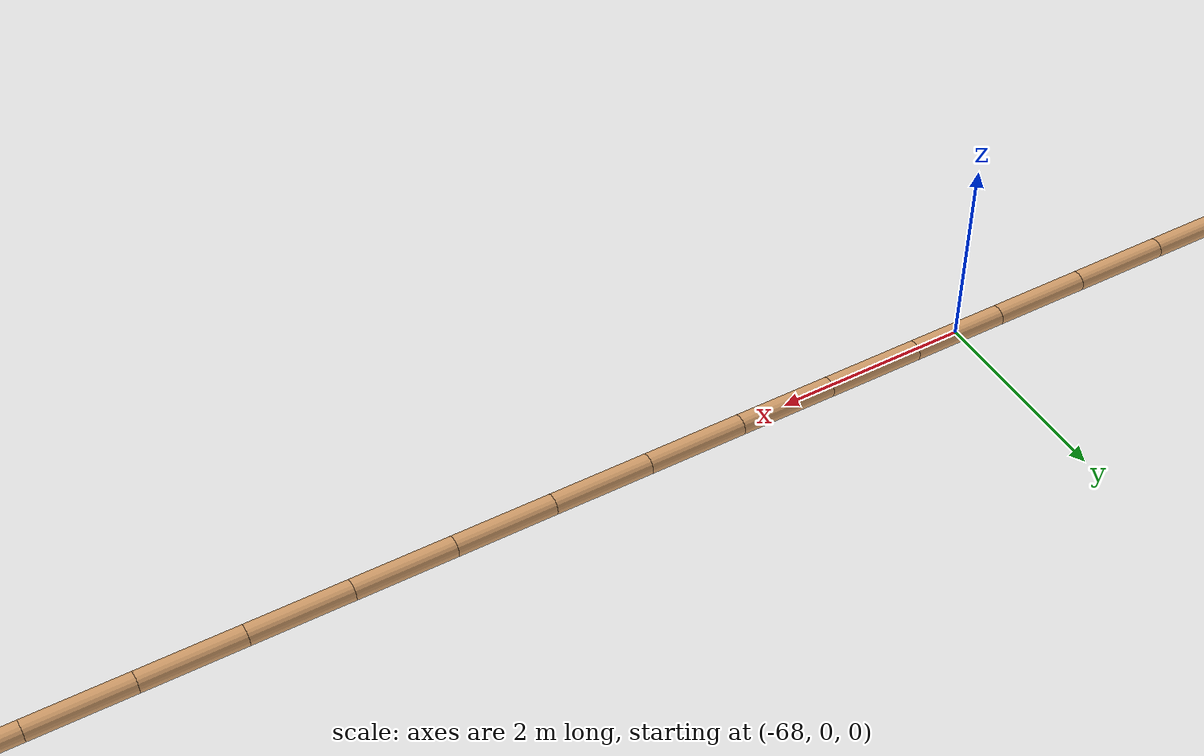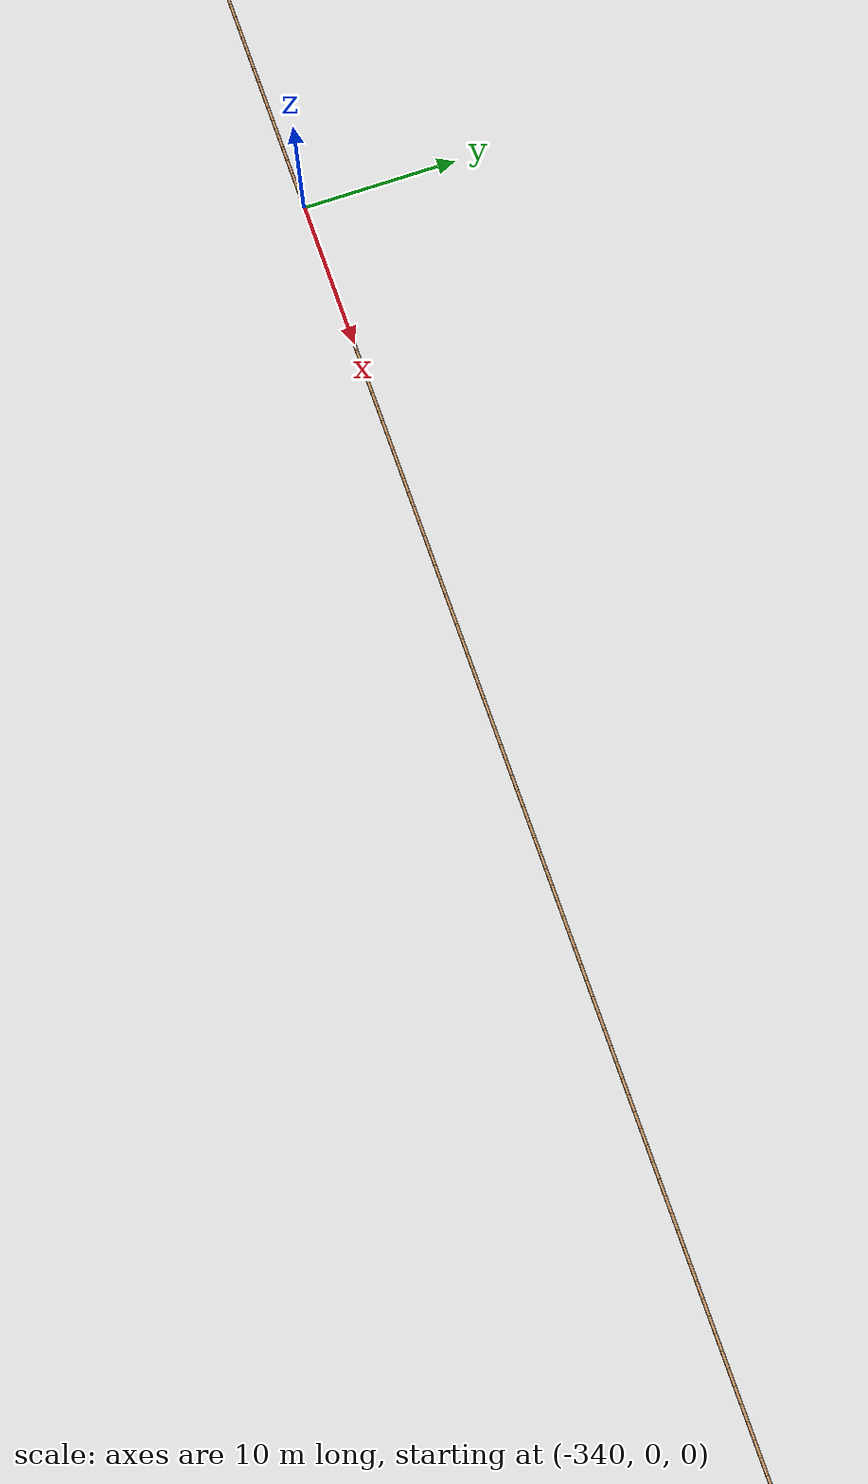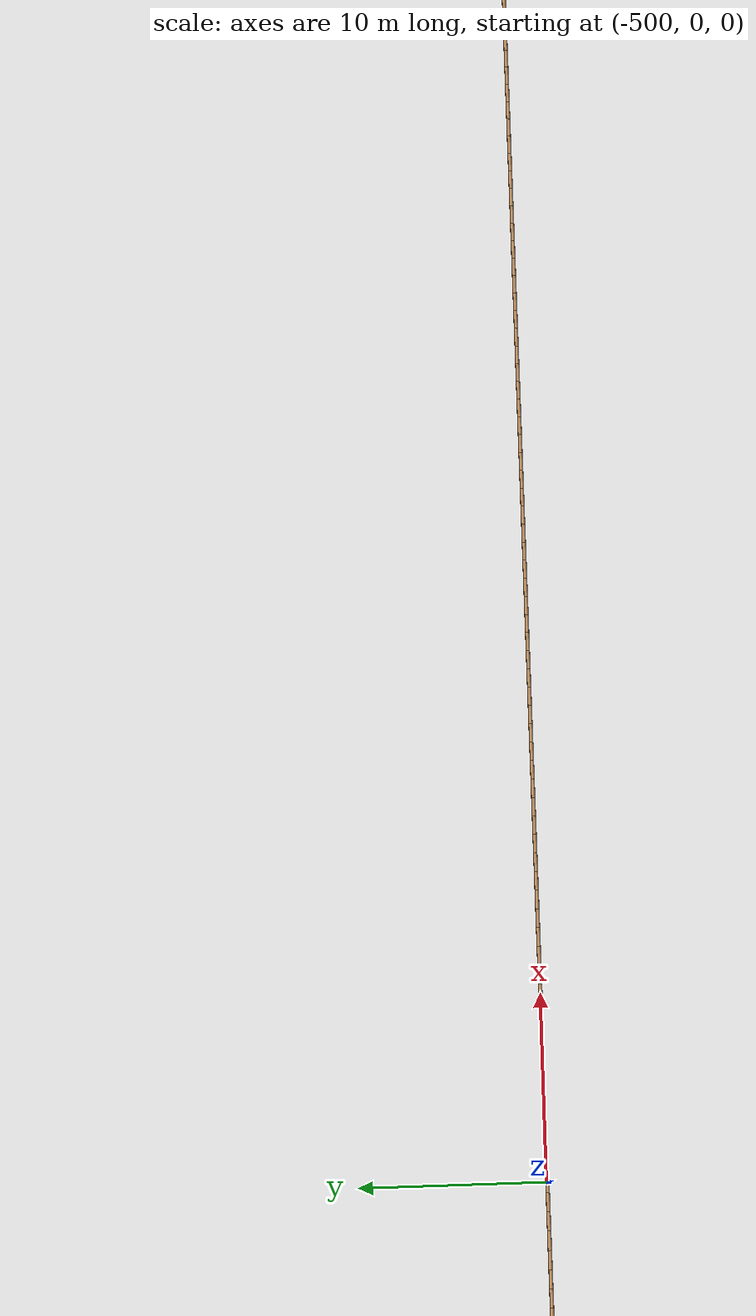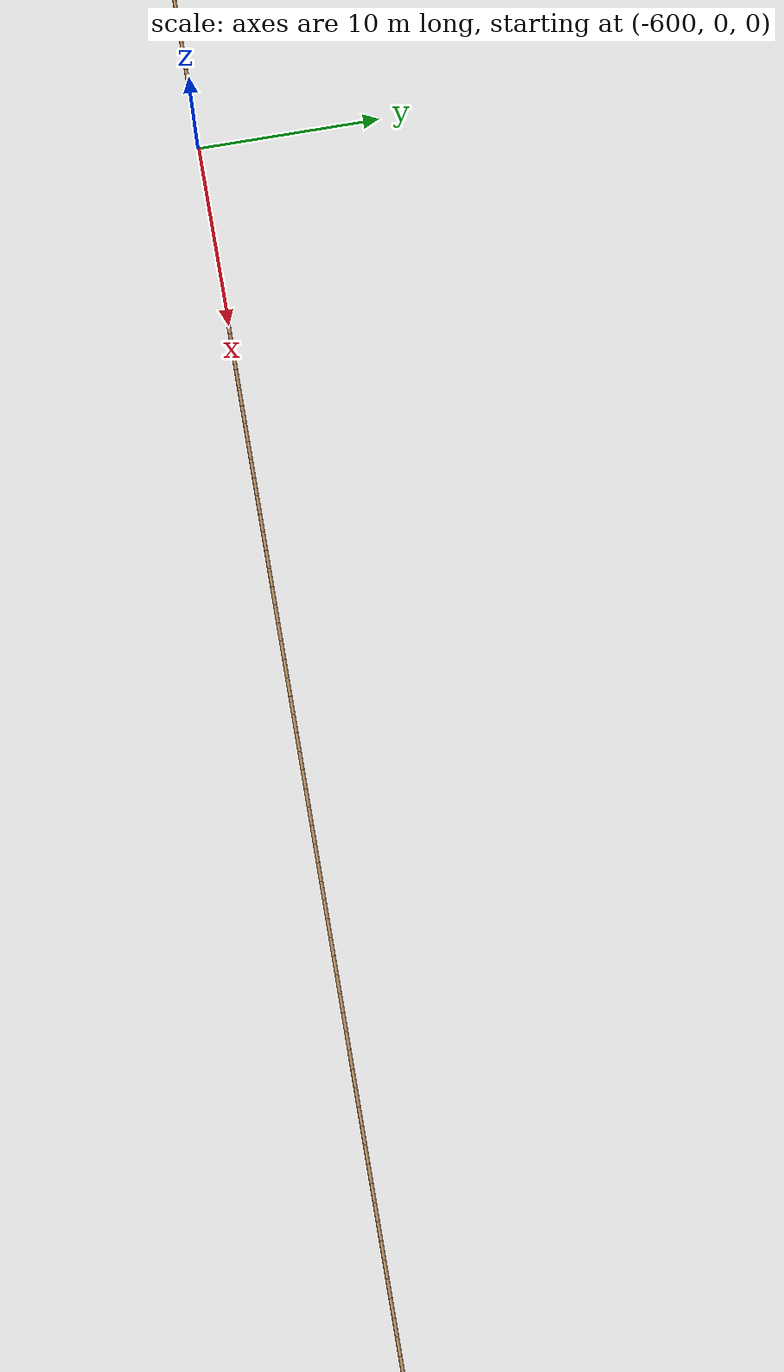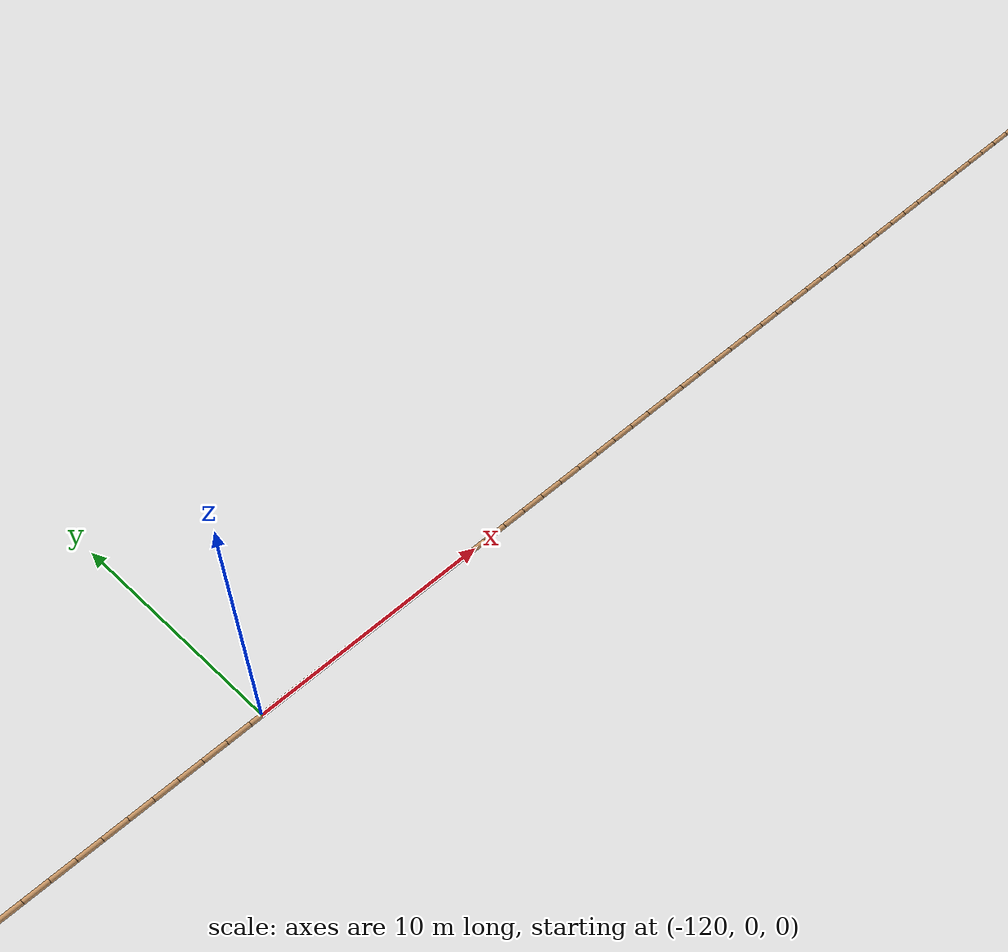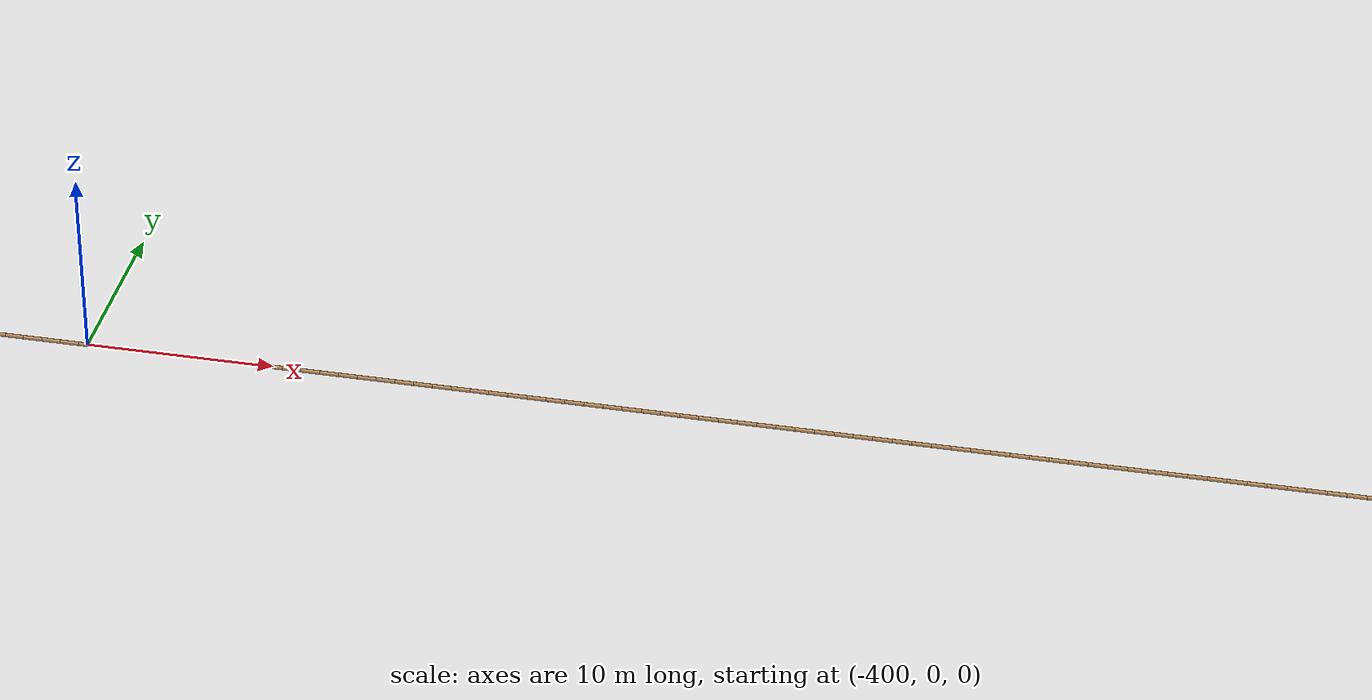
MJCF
<mujoco model="swimmer">
  <compiler angle="degree" coordinate="local" inertiafromgeom="true"/>
  <option collision="predefined" density="4000" integrator="RK4" timestep="0.01" viscosity="0.1"/>
  <default>
    <geom conaffinity="1" condim="1" contype="1" material="geom" rgba="0.8 0.6 .4 1"/>
    <joint armature='0.1'  />
  </default>
  <asset>
    <texture builtin="gradient" height="100" rgb1="1 1 1" rgb2="0 0 0" type="skybox" width="100"/>
    <texture builtin="flat" height="1278" mark="cross" markrgb="1 1 1" name="texgeom" random="0.01" rgb1="0.8 0.6 0.4" rgb2="0.8 0.6 0.4" type="cube" width="127"/>
    <texture builtin="checker" height="100" name="texplane" rgb1="0 0 0" rgb2="0.8 0.8 0.8" type="2d" width="100"/>
    <material name="MatPlane" reflectance="0.5" shininess="1" specular="1" texrepeat="30 30" texture="texplane"/>
    <material name="geom" texture="texgeom" texuniform="true"/>
  </asset>
  <worldbody>
    <light cutoff="100" diffuse="1 1 1" dir="-0 0 -1.3" directional="true" exponent="1" pos="0 0 1.3" specular=".1 .1 .1"/>
    <geom conaffinity="1" condim="3" material="MatPlane" name="floor" pos="0 0 -0.1" rgba="0.8 0.9 0.8 1" size="40 40 0.1" type="plane"/>
    <!--  ================= SWIMMER ================= /-->
    <body name="torso" pos="0 0 0">
      <geom density="1000" fromto="1.5 0 0 0.5 0 0" size="0.1" type="capsule"/>
      <joint axis="1 0 0" name="slider1" pos="0 0 0" type="slide"/>
      <joint axis="0 1 0" name="slider2" pos="0 0 0" type="slide"/>
      <joint axis="0 0 1" name="rot" pos="0 0 0" type="hinge"/>
      <body name="mid0" pos="0.5 0 0">
        <geom density="1000" fromto="0 0 0 -1 0 0" size="0.1" type="capsule"/>
        <joint axis="0 0 1" limited="true" name="rot0" pos="0 0 0" range="-100 100" type="hinge"/>

        <body name="mid1" pos="-1 0 0">
          <geom density="1000" fromto="0 0 0 -1 0 0" size="0.1" type="capsule"/>
          <joint axis="0 0 1" limited="true" name="rot1" pos="0 0 0" range="-100 100" type="hinge"/>

        <body name="mid2" pos="-1 0 0">
          <geom density="1000" fromto="0 0 0 -1 0 0" size="0.1" type="capsule"/>
          <joint axis="0 0 -1" limited="true" name="rot2" pos="0 0 0" range="-100 100" type="hinge"/>

        <body name="mid3" pos="-1 0 0">
          <geom density="1000" fromto="0 0 0 -1 0 0" size="0.1" type="capsule"/>
          <joint axis="0 0 1" limited="true" name="rot3" pos="0 0 0" range="-100 100" type="hinge"/>

        <body name="mid4" pos="-1 0 0">
          <geom density="1000" fromto="0 0 0 -1 0 0" size="0.1" type="capsule"/>
          <joint axis="0 0 -1" limited="true" name="rot4" pos="0 0 0" range="-100 100" type="hinge"/>

        <body name="mid5" pos="-1 0 0">
          <geom density="1000" fromto="0 0 0 -1 0 0" size="0.1" type="capsule"/>
          <joint axis="0 0 1" limited="true" name="rot5" pos="0 0 0" range="-100 100" type="hinge"/>

        <body name="mid6" pos="-1 0 0">
          <geom density="1000" fromto="0 0 0 -1 0 0" size="0.1" type="capsule"/>
          <joint axis="0 0 -1" limited="true" name="rot6" pos="0 0 0" range="-100 100" type="hinge"/>

        <body name="mid7" pos="-1 0 0">
          <geom density="1000" fromto="0 0 0 -1 0 0" size="0.1" type="capsule"/>
          <joint axis="0 0 1" limited="true" name="rot7" pos="0 0 0" range="-100 100" type="hinge"/>

        <body name="mid8" pos="-1 0 0">
          <geom density="1000" fromto="0 0 0 -1 0 0" size="0.1" type="capsule"/>
          <joint axis="0 0 -1" limited="true" name="rot8" pos="0 0 0" range="-100 100" type="hinge"/>

        <body name="mid9" pos="-1 0 0">
          <geom density="1000" fromto="0 0 0 -1 0 0" size="0.1" type="capsule"/>
          <joint axis="0 0 1" limited="true" name="rot9" pos="0 0 0" range="-100 100" type="hinge"/>

        <body name="mid10" pos="-1 0 0">
          <geom density="1000" fromto="0 0 0 -1 0 0" size="0.1" type="capsule"/>
          <joint axis="0 0 -1" limited="true" name="rot10" pos="0 0 0" range="-100 100" type="hinge"/>

        <body name="mid11" pos="-1 0 0">
          <geom density="1000" fromto="0 0 0 -1 0 0" size="0.1" type="capsule"/>
          <joint axis="0 0 1" limited="true" name="rot11" pos="0 0 0" range="-100 100" type="hinge"/>

        <body name="mid12" pos="-1 0 0">
          <geom density="1000" fromto="0 0 0 -1 0 0" size="0.1" type="capsule"/>
          <joint axis="0 0 -1" limited="true" name="rot12" pos="0 0 0" range="-100 100" type="hinge"/>

        <body name="mid13" pos="-1 0 0">
          <geom density="1000" fromto="0 0 0 -1 0 0" size="0.1" type="capsule"/>
          <joint axis="0 0 1" limited="true" name="rot13" pos="0 0 0" range="-100 100" type="hinge"/>

        <body name="mid14" pos="-1 0 0">
          <geom density="1000" fromto="0 0 0 -1 0 0" size="0.1" type="capsule"/>
          <joint axis="0 0 -1" limited="true" name="rot14" pos="0 0 0" range="-100 100" type="hinge"/>

        <body name="mid15" pos="-1 0 0">
          <geom density="1000" fromto="0 0 0 -1 0 0" size="0.1" type="capsule"/>
          <joint axis="0 0 1" limited="true" name="rot15" pos="0 0 0" range="-100 100" type="hinge"/>

        <body name="mid16" pos="-1 0 0">
          <geom density="1000" fromto="0 0 0 -1 0 0" size="0.1" type="capsule"/>
          <joint axis="0 0 -1" limited="true" name="rot16" pos="0 0 0" range="-100 100" type="hinge"/>

        <body name="mid17" pos="-1 0 0">
          <geom density="1000" fromto="0 0 0 -1 0 0" size="0.1" type="capsule"/>
          <joint axis="0 0 1" limited="true" name="rot17" pos="0 0 0" range="-100 100" type="hinge"/>

        <body name="mid18" pos="-1 0 0">
          <geom density="1000" fromto="0 0 0 -1 0 0" size="0.1" type="capsule"/>
          <joint axis="0 0 -1" limited="true" name="rot18" pos="0 0 0" range="-100 100" type="hinge"/>

        <body name="mid19" pos="-1 0 0">
          <geom density="1000" fromto="0 0 0 -1 0 0" size="0.1" type="capsule"/>
          <joint axis="0 0 1" limited="true" name="rot19" pos="0 0 0" range="-100 100" type="hinge"/>

        <body name="mid20" pos="-1 0 0">
          <geom density="1000" fromto="0 0 0 -1 0 0" size="0.1" type="capsule"/>
          <joint axis="0 0 -1" limited="true" name="rot20" pos="0 0 0" range="-100 100" type="hinge"/>

        <body name="mid21" pos="-1 0 0">
          <geom density="1000" fromto="0 0 0 -1 0 0" size="0.1" type="capsule"/>
          <joint axis="0 0 1" limited="true" name="rot21" pos="0 0 0" range="-100 100" type="hinge"/>

        <body name="mid22" pos="-1 0 0">
          <geom density="1000" fromto="0 0 0 -1 0 0" size="0.1" type="capsule"/>
          <joint axis="0 0 -1" limited="true" name="rot22" pos="0 0 0" range="-100 100" type="hinge"/>

        <body name="mid23" pos="-1 0 0">
          <geom density="1000" fromto="0 0 0 -1 0 0" size="0.1" type="capsule"/>
          <joint axis="0 0 1" limited="true" name="rot23" pos="0 0 0" range="-100 100" type="hinge"/>

        <body name="mid24" pos="-1 0 0">
          <geom density="1000" fromto="0 0 0 -1 0 0" size="0.1" type="capsule"/>
          <joint axis="0 0 -1" limited="true" name="rot24" pos="0 0 0" range="-100 100" type="hinge"/>

        <body name="mid25" pos="-1 0 0">
          <geom density="1000" fromto="0 0 0 -1 0 0" size="0.1" type="capsule"/>
          <joint axis="0 0 1" limited="true" name="rot25" pos="0 0 0" range="-100 100" type="hinge"/>

        <body name="mid26" pos="-1 0 0">
          <geom density="1000" fromto="0 0 0 -1 0 0" size="0.1" type="capsule"/>
          <joint axis="0 0 -1" limited="true" name="rot26" pos="0 0 0" range="-100 100" type="hinge"/>

        <body name="mid27" pos="-1 0 0">
          <geom density="1000" fromto="0 0 0 -1 0 0" size="0.1" type="capsule"/>
          <joint axis="0 0 1" limited="true" name="rot27" pos="0 0 0" range="-100 100" type="hinge"/>

        <body name="mid28" pos="-1 0 0">
          <geom density="1000" fromto="0 0 0 -1 0 0" size="0.1" type="capsule"/>
          <joint axis="0 0 -1" limited="true" name="rot28" pos="0 0 0" range="-100 100" type="hinge"/>

        <body name="mid29" pos="-1 0 0">
          <geom density="1000" fromto="0 0 0 -1 0 0" size="0.1" type="capsule"/>
          <joint axis="0 0 1" limited="true" name="rot29" pos="0 0 0" range="-100 100" type="hinge"/>

        <body name="mid30" pos="-1 0 0">
          <geom density="1000" fromto="0 0 0 -1 0 0" size="0.1" type="capsule"/>
          <joint axis="0 0 -1" limited="true" name="rot30" pos="0 0 0" range="-100 100" type="hinge"/>

        <body name="mid31" pos="-1 0 0">
          <geom density="1000" fromto="0 0 0 -1 0 0" size="0.1" type="capsule"/>
          <joint axis="0 0 1" limited="true" name="rot31" pos="0 0 0" range="-100 100" type="hinge"/>

        <body name="mid32" pos="-1 0 0">
          <geom density="1000" fromto="0 0 0 -1 0 0" size="0.1" type="capsule"/>
          <joint axis="0 0 -1" limited="true" name="rot32" pos="0 0 0" range="-100 100" type="hinge"/>

        <body name="mid33" pos="-1 0 0">
          <geom density="1000" fromto="0 0 0 -1 0 0" size="0.1" type="capsule"/>
          <joint axis="0 0 1" limited="true" name="rot33" pos="0 0 0" range="-100 100" type="hinge"/>

        <body name="mid34" pos="-1 0 0">
          <geom density="1000" fromto="0 0 0 -1 0 0" size="0.1" type="capsule"/>
          <joint axis="0 0 -1" limited="true" name="rot34" pos="0 0 0" range="-100 100" type="hinge"/>

        <body name="mid35" pos="-1 0 0">
          <geom density="1000" fromto="0 0 0 -1 0 0" size="0.1" type="capsule"/>
          <joint axis="0 0 1" limited="true" name="rot35" pos="0 0 0" range="-100 100" type="hinge"/>

        <body name="mid36" pos="-1 0 0">
          <geom density="1000" fromto="0 0 0 -1 0 0" size="0.1" type="capsule"/>
          <joint axis="0 0 -1" limited="true" name="rot36" pos="0 0 0" range="-100 100" type="hinge"/>

        <body name="mid37" pos="-1 0 0">
          <geom density="1000" fromto="0 0 0 -1 0 0" size="0.1" type="capsule"/>
          <joint axis="0 0 1" limited="true" name="rot37" pos="0 0 0" range="-100 100" type="hinge"/>

        <body name="mid38" pos="-1 0 0">
          <geom density="1000" fromto="0 0 0 -1 0 0" size="0.1" type="capsule"/>
          <joint axis="0 0 -1" limited="true" name="rot38" pos="0 0 0" range="-100 100" type="hinge"/>

        <body name="mid39" pos="-1 0 0">
          <geom density="1000" fromto="0 0 0 -1 0 0" size="0.1" type="capsule"/>
          <joint axis="0 0 1" limited="true" name="rot39" pos="0 0 0" range="-100 100" type="hinge"/>

        <body name="mid40" pos="-1 0 0">
          <geom density="1000" fromto="0 0 0 -1 0 0" size="0.1" type="capsule"/>
          <joint axis="0 0 -1" limited="true" name="rot40" pos="0 0 0" range="-100 100" type="hinge"/>

        <body name="mid41" pos="-1 0 0">
          <geom density="1000" fromto="0 0 0 -1 0 0" size="0.1" type="capsule"/>
          <joint axis="0 0 1" limited="true" name="rot41" pos="0 0 0" range="-100 100" type="hinge"/>

        <body name="mid42" pos="-1 0 0">
          <geom density="1000" fromto="0 0 0 -1 0 0" size="0.1" type="capsule"/>
          <joint axis="0 0 -1" limited="true" name="rot42" pos="0 0 0" range="-100 100" type="hinge"/>

        <body name="mid43" pos="-1 0 0">
          <geom density="1000" fromto="0 0 0 -1 0 0" size="0.1" type="capsule"/>
          <joint axis="0 0 1" limited="true" name="rot43" pos="0 0 0" range="-100 100" type="hinge"/>

        <body name="mid44" pos="-1 0 0">
          <geom density="1000" fromto="0 0 0 -1 0 0" size="0.1" type="capsule"/>
          <joint axis="0 0 -1" limited="true" name="rot44" pos="0 0 0" range="-100 100" type="hinge"/>

        <body name="mid45" pos="-1 0 0">
          <geom density="1000" fromto="0 0 0 -1 0 0" size="0.1" type="capsule"/>
          <joint axis="0 0 1" limited="true" name="rot45" pos="0 0 0" range="-100 100" type="hinge"/>

        <body name="mid46" pos="-1 0 0">
          <geom density="1000" fromto="0 0 0 -1 0 0" size="0.1" type="capsule"/>
          <joint axis="0 0 -1" limited="true" name="rot46" pos="0 0 0" range="-100 100" type="hinge"/>

        <body name="mid47" pos="-1 0 0">
          <geom density="1000" fromto="0 0 0 -1 0 0" size="0.1" type="capsule"/>
          <joint axis="0 0 1" limited="true" name="rot47" pos="0 0 0" range="-100 100" type="hinge"/>

        <body name="mid48" pos="-1 0 0">
          <geom density="1000" fromto="0 0 0 -1 0 0" size="0.1" type="capsule"/>
          <joint axis="0 0 -1" limited="true" name="rot48" pos="0 0 0" range="-100 100" type="hinge"/>

        <body name="mid49" pos="-1 0 0">
          <geom density="1000" fromto="0 0 0 -1 0 0" size="0.1" type="capsule"/>
          <joint axis="0 0 1" limited="true" name="rot49" pos="0 0 0" range="-100 100" type="hinge"/>

        <body name="mid50" pos="-1 0 0">
          <geom density="1000" fromto="0 0 0 -1 0 0" size="0.1" type="capsule"/>
          <joint axis="0 0 -1" limited="true" name="rot50" pos="0 0 0" range="-100 100" type="hinge"/>

        <body name="mid51" pos="-1 0 0">
          <geom density="1000" fromto="0 0 0 -1 0 0" size="0.1" type="capsule"/>
          <joint axis="0 0 1" limited="true" name="rot51" pos="0 0 0" range="-100 100" type="hinge"/>

        <body name="mid52" pos="-1 0 0">
          <geom density="1000" fromto="0 0 0 -1 0 0" size="0.1" type="capsule"/>
          <joint axis="0 0 -1" limited="true" name="rot52" pos="0 0 0" range="-100 100" type="hinge"/>

        <body name="mid53" pos="-1 0 0">
          <geom density="1000" fromto="0 0 0 -1 0 0" size="0.1" type="capsule"/>
          <joint axis="0 0 1" limited="true" name="rot53" pos="0 0 0" range="-100 100" type="hinge"/>

        <body name="mid54" pos="-1 0 0">
          <geom density="1000" fromto="0 0 0 -1 0 0" size="0.1" type="capsule"/>
          <joint axis="0 0 -1" limited="true" name="rot54" pos="0 0 0" range="-100 100" type="hinge"/>

        <body name="mid55" pos="-1 0 0">
          <geom density="1000" fromto="0 0 0 -1 0 0" size="0.1" type="capsule"/>
          <joint axis="0 0 1" limited="true" name="rot55" pos="0 0 0" range="-100 100" type="hinge"/>

        <body name="mid56" pos="-1 0 0">
          <geom density="1000" fromto="0 0 0 -1 0 0" size="0.1" type="capsule"/>
          <joint axis="0 0 -1" limited="true" name="rot56" pos="0 0 0" range="-100 100" type="hinge"/>

        <body name="mid57" pos="-1 0 0">
          <geom density="1000" fromto="0 0 0 -1 0 0" size="0.1" type="capsule"/>
          <joint axis="0 0 1" limited="true" name="rot57" pos="0 0 0" range="-100 100" type="hinge"/>

        <body name="mid58" pos="-1 0 0">
          <geom density="1000" fromto="0 0 0 -1 0 0" size="0.1" type="capsule"/>
          <joint axis="0 0 -1" limited="true" name="rot58" pos="0 0 0" range="-100 100" type="hinge"/>

        <body name="mid59" pos="-1 0 0">
          <geom density="1000" fromto="0 0 0 -1 0 0" size="0.1" type="capsule"/>
          <joint axis="0 0 1" limited="true" name="rot59" pos="0 0 0" range="-100 100" type="hinge"/>

        <body name="mid60" pos="-1 0 0">
          <geom density="1000" fromto="0 0 0 -1 0 0" size="0.1" type="capsule"/>
          <joint axis="0 0 -1" limited="true" name="rot60" pos="0 0 0" range="-100 100" type="hinge"/>

        <body name="mid61" pos="-1 0 0">
          <geom density="1000" fromto="0 0 0 -1 0 0" size="0.1" type="capsule"/>
          <joint axis="0 0 1" limited="true" name="rot61" pos="0 0 0" range="-100 100" type="hinge"/>

        <body name="mid62" pos="-1 0 0">
          <geom density="1000" fromto="0 0 0 -1 0 0" size="0.1" type="capsule"/>
          <joint axis="0 0 -1" limited="true" name="rot62" pos="0 0 0" range="-100 100" type="hinge"/>

        <body name="mid63" pos="-1 0 0">
          <geom density="1000" fromto="0 0 0 -1 0 0" size="0.1" type="capsule"/>
          <joint axis="0 0 1" limited="true" name="rot63" pos="0 0 0" range="-100 100" type="hinge"/>

        <body name="mid64" pos="-1 0 0">
          <geom density="1000" fromto="0 0 0 -1 0 0" size="0.1" type="capsule"/>
          <joint axis="0 0 -1" limited="true" name="rot64" pos="0 0 0" range="-100 100" type="hinge"/>

        <body name="mid65" pos="-1 0 0">
          <geom density="1000" fromto="0 0 0 -1 0 0" size="0.1" type="capsule"/>
          <joint axis="0 0 1" limited="true" name="rot65" pos="0 0 0" range="-100 100" type="hinge"/>

        <body name="mid66" pos="-1 0 0">
          <geom density="1000" fromto="0 0 0 -1 0 0" size="0.1" type="capsule"/>
          <joint axis="0 0 -1" limited="true" name="rot66" pos="0 0 0" range="-100 100" type="hinge"/>

        <body name="mid67" pos="-1 0 0">
          <geom density="1000" fromto="0 0 0 -1 0 0" size="0.1" type="capsule"/>
          <joint axis="0 0 1" limited="true" name="rot67" pos="0 0 0" range="-100 100" type="hinge"/>

        <body name="mid68" pos="-1 0 0">
          <geom density="1000" fromto="0 0 0 -1 0 0" size="0.1" type="capsule"/>
          <joint axis="0 0 -1" limited="true" name="rot68" pos="0 0 0" range="-100 100" type="hinge"/>

        <body name="mid69" pos="-1 0 0">
          <geom density="1000" fromto="0 0 0 -1 0 0" size="0.1" type="capsule"/>
          <joint axis="0 0 1" limited="true" name="rot69" pos="0 0 0" range="-100 100" type="hinge"/>

        <body name="mid70" pos="-1 0 0">
          <geom density="1000" fromto="0 0 0 -1 0 0" size="0.1" type="capsule"/>
          <joint axis="0 0 -1" limited="true" name="rot70" pos="0 0 0" range="-100 100" type="hinge"/>

        <body name="mid71" pos="-1 0 0">
          <geom density="1000" fromto="0 0 0 -1 0 0" size="0.1" type="capsule"/>
          <joint axis="0 0 1" limited="true" name="rot71" pos="0 0 0" range="-100 100" type="hinge"/>

        <body name="mid72" pos="-1 0 0">
          <geom density="1000" fromto="0 0 0 -1 0 0" size="0.1" type="capsule"/>
          <joint axis="0 0 -1" limited="true" name="rot72" pos="0 0 0" range="-100 100" type="hinge"/>

        <body name="mid73" pos="-1 0 0">
          <geom density="1000" fromto="0 0 0 -1 0 0" size="0.1" type="capsule"/>
          <joint axis="0 0 1" limited="true" name="rot73" pos="0 0 0" range="-100 100" type="hinge"/>

        <body name="mid74" pos="-1 0 0">
          <geom density="1000" fromto="0 0 0 -1 0 0" size="0.1" type="capsule"/>
          <joint axis="0 0 -1" limited="true" name="rot74" pos="0 0 0" range="-100 100" type="hinge"/>

        <body name="mid75" pos="-1 0 0">
          <geom density="1000" fromto="0 0 0 -1 0 0" size="0.1" type="capsule"/>
          <joint axis="0 0 1" limited="true" name="rot75" pos="0 0 0" range="-100 100" type="hinge"/>

        <body name="mid76" pos="-1 0 0">
          <geom density="1000" fromto="0 0 0 -1 0 0" size="0.1" type="capsule"/>
          <joint axis="0 0 -1" limited="true" name="rot76" pos="0 0 0" range="-100 100" type="hinge"/>

        <body name="mid77" pos="-1 0 0">
          <geom density="1000" fromto="0 0 0 -1 0 0" size="0.1" type="capsule"/>
          <joint axis="0 0 1" limited="true" name="rot77" pos="0 0 0" range="-100 100" type="hinge"/>

        <body name="mid78" pos="-1 0 0">
          <geom density="1000" fromto="0 0 0 -1 0 0" size="0.1" type="capsule"/>
          <joint axis="0 0 -1" limited="true" name="rot78" pos="0 0 0" range="-100 100" type="hinge"/>

        <body name="mid79" pos="-1 0 0">
          <geom density="1000" fromto="0 0 0 -1 0 0" size="0.1" type="capsule"/>
          <joint axis="0 0 1" limited="true" name="rot79" pos="0 0 0" range="-100 100" type="hinge"/>

        <body name="mid80" pos="-1 0 0">
          <geom density="1000" fromto="0 0 0 -1 0 0" size="0.1" type="capsule"/>
          <joint axis="0 0 -1" limited="true" name="rot80" pos="0 0 0" range="-100 100" type="hinge"/>

        <body name="mid81" pos="-1 0 0">
          <geom density="1000" fromto="0 0 0 -1 0 0" size="0.1" type="capsule"/>
          <joint axis="0 0 1" limited="true" name="rot81" pos="0 0 0" range="-100 100" type="hinge"/>

        <body name="mid82" pos="-1 0 0">
          <geom density="1000" fromto="0 0 0 -1 0 0" size="0.1" type="capsule"/>
          <joint axis="0 0 -1" limited="true" name="rot82" pos="0 0 0" range="-100 100" type="hinge"/>

        <body name="mid83" pos="-1 0 0">
          <geom density="1000" fromto="0 0 0 -1 0 0" size="0.1" type="capsule"/>
          <joint axis="0 0 1" limited="true" name="rot83" pos="0 0 0" range="-100 100" type="hinge"/>

        <body name="mid84" pos="-1 0 0">
          <geom density="1000" fromto="0 0 0 -1 0 0" size="0.1" type="capsule"/>
          <joint axis="0 0 -1" limited="true" name="rot84" pos="0 0 0" range="-100 100" type="hinge"/>

        <body name="mid85" pos="-1 0 0">
          <geom density="1000" fromto="0 0 0 -1 0 0" size="0.1" type="capsule"/>
          <joint axis="0 0 1" limited="true" name="rot85" pos="0 0 0" range="-100 100" type="hinge"/>

        <body name="mid86" pos="-1 0 0">
          <geom density="1000" fromto="0 0 0 -1 0 0" size="0.1" type="capsule"/>
          <joint axis="0 0 -1" limited="true" name="rot86" pos="0 0 0" range="-100 100" type="hinge"/>

        <body name="mid87" pos="-1 0 0">
          <geom density="1000" fromto="0 0 0 -1 0 0" size="0.1" type="capsule"/>
          <joint axis="0 0 1" limited="true" name="rot87" pos="0 0 0" range="-100 100" type="hinge"/>

        <body name="mid88" pos="-1 0 0">
          <geom density="1000" fromto="0 0 0 -1 0 0" size="0.1" type="capsule"/>
          <joint axis="0 0 -1" limited="true" name="rot88" pos="0 0 0" range="-100 100" type="hinge"/>

        <body name="mid89" pos="-1 0 0">
          <geom density="1000" fromto="0 0 0 -1 0 0" size="0.1" type="capsule"/>
          <joint axis="0 0 1" limited="true" name="rot89" pos="0 0 0" range="-100 100" type="hinge"/>

        <body name="mid90" pos="-1 0 0">
          <geom density="1000" fromto="0 0 0 -1 0 0" size="0.1" type="capsule"/>
          <joint axis="0 0 -1" limited="true" name="rot90" pos="0 0 0" range="-100 100" type="hinge"/>

        <body name="mid91" pos="-1 0 0">
          <geom density="1000" fromto="0 0 0 -1 0 0" size="0.1" type="capsule"/>
          <joint axis="0 0 1" limited="true" name="rot91" pos="0 0 0" range="-100 100" type="hinge"/>

        <body name="mid92" pos="-1 0 0">
          <geom density="1000" fromto="0 0 0 -1 0 0" size="0.1" type="capsule"/>
          <joint axis="0 0 -1" limited="true" name="rot92" pos="0 0 0" range="-100 100" type="hinge"/>

        <body name="mid93" pos="-1 0 0">
          <geom density="1000" fromto="0 0 0 -1 0 0" size="0.1" type="capsule"/>
          <joint axis="0 0 1" limited="true" name="rot93" pos="0 0 0" range="-100 100" type="hinge"/>

        <body name="mid94" pos="-1 0 0">
          <geom density="1000" fromto="0 0 0 -1 0 0" size="0.1" type="capsule"/>
          <joint axis="0 0 -1" limited="true" name="rot94" pos="0 0 0" range="-100 100" type="hinge"/>

        <body name="mid95" pos="-1 0 0">
          <geom density="1000" fromto="0 0 0 -1 0 0" size="0.1" type="capsule"/>
          <joint axis="0 0 1" limited="true" name="rot95" pos="0 0 0" range="-100 100" type="hinge"/>

        <body name="mid96" pos="-1 0 0">
          <geom density="1000" fromto="0 0 0 -1 0 0" size="0.1" type="capsule"/>
          <joint axis="0 0 -1" limited="true" name="rot96" pos="0 0 0" range="-100 100" type="hinge"/>

        <body name="mid97" pos="-1 0 0">
          <geom density="1000" fromto="0 0 0 -1 0 0" size="0.1" type="capsule"/>
          <joint axis="0 0 1" limited="true" name="rot97" pos="0 0 0" range="-100 100" type="hinge"/>

        <body name="mid98" pos="-1 0 0">
          <geom density="1000" fromto="0 0 0 -1 0 0" size="0.1" type="capsule"/>
          <joint axis="0 0 -1" limited="true" name="rot98" pos="0 0 0" range="-100 100" type="hinge"/>

        <body name="mid99" pos="-1 0 0">
          <geom density="1000" fromto="0 0 0 -1 0 0" size="0.1" type="capsule"/>
          <joint axis="0 0 1" limited="true" name="rot99" pos="0 0 0" range="-100 100" type="hinge"/>

        <body name="mid100" pos="-1 0 0">
          <geom density="1000" fromto="0 0 0 -1 0 0" size="0.1" type="capsule"/>
          <joint axis="0 0 -1" limited="true" name="rot100" pos="0 0 0" range="-100 100" type="hinge"/>

        <body name="mid101" pos="-1 0 0">
          <geom density="1000" fromto="0 0 0 -1 0 0" size="0.1" type="capsule"/>
          <joint axis="0 0 1" limited="true" name="rot101" pos="0 0 0" range="-100 100" type="hinge"/>

        <body name="mid102" pos="-1 0 0">
          <geom density="1000" fromto="0 0 0 -1 0 0" size="0.1" type="capsule"/>
          <joint axis="0 0 -1" limited="true" name="rot102" pos="0 0 0" range="-100 100" type="hinge"/>

        <body name="mid103" pos="-1 0 0">
          <geom density="1000" fromto="0 0 0 -1 0 0" size="0.1" type="capsule"/>
          <joint axis="0 0 1" limited="true" name="rot103" pos="0 0 0" range="-100 100" type="hinge"/>

        <body name="mid104" pos="-1 0 0">
          <geom density="1000" fromto="0 0 0 -1 0 0" size="0.1" type="capsule"/>
          <joint axis="0 0 -1" limited="true" name="rot104" pos="0 0 0" range="-100 100" type="hinge"/>

        <body name="mid105" pos="-1 0 0">
          <geom density="1000" fromto="0 0 0 -1 0 0" size="0.1" type="capsule"/>
          <joint axis="0 0 1" limited="true" name="rot105" pos="0 0 0" range="-100 100" type="hinge"/>

        <body name="mid106" pos="-1 0 0">
          <geom density="1000" fromto="0 0 0 -1 0 0" size="0.1" type="capsule"/>
          <joint axis="0 0 -1" limited="true" name="rot106" pos="0 0 0" range="-100 100" type="hinge"/>

        <body name="mid107" pos="-1 0 0">
          <geom density="1000" fromto="0 0 0 -1 0 0" size="0.1" type="capsule"/>
          <joint axis="0 0 1" limited="true" name="rot107" pos="0 0 0" range="-100 100" type="hinge"/>

        <body name="mid108" pos="-1 0 0">
          <geom density="1000" fromto="0 0 0 -1 0 0" size="0.1" type="capsule"/>
          <joint axis="0 0 -1" limited="true" name="rot108" pos="0 0 0" range="-100 100" type="hinge"/>

        <body name="mid109" pos="-1 0 0">
          <geom density="1000" fromto="0 0 0 -1 0 0" size="0.1" type="capsule"/>
          <joint axis="0 0 1" limited="true" name="rot109" pos="0 0 0" range="-100 100" type="hinge"/>

        <body name="mid110" pos="-1 0 0">
          <geom density="1000" fromto="0 0 0 -1 0 0" size="0.1" type="capsule"/>
          <joint axis="0 0 -1" limited="true" name="rot110" pos="0 0 0" range="-100 100" type="hinge"/>

        <body name="mid111" pos="-1 0 0">
          <geom density="1000" fromto="0 0 0 -1 0 0" size="0.1" type="capsule"/>
          <joint axis="0 0 1" limited="true" name="rot111" pos="0 0 0" range="-100 100" type="hinge"/>

        <body name="mid112" pos="-1 0 0">
          <geom density="1000" fromto="0 0 0 -1 0 0" size="0.1" type="capsule"/>
          <joint axis="0 0 -1" limited="true" name="rot112" pos="0 0 0" range="-100 100" type="hinge"/>

        <body name="mid113" pos="-1 0 0">
          <geom density="1000" fromto="0 0 0 -1 0 0" size="0.1" type="capsule"/>
          <joint axis="0 0 1" limited="true" name="rot113" pos="0 0 0" range="-100 100" type="hinge"/>

        <body name="mid114" pos="-1 0 0">
          <geom density="1000" fromto="0 0 0 -1 0 0" size="0.1" type="capsule"/>
          <joint axis="0 0 -1" limited="true" name="rot114" pos="0 0 0" range="-100 100" type="hinge"/>

        <body name="mid115" pos="-1 0 0">
          <geom density="1000" fromto="0 0 0 -1 0 0" size="0.1" type="capsule"/>
          <joint axis="0 0 1" limited="true" name="rot115" pos="0 0 0" range="-100 100" type="hinge"/>

        <body name="mid116" pos="-1 0 0">
          <geom density="1000" fromto="0 0 0 -1 0 0" size="0.1" type="capsule"/>
          <joint axis="0 0 -1" limited="true" name="rot116" pos="0 0 0" range="-100 100" type="hinge"/>

        <body name="mid117" pos="-1 0 0">
          <geom density="1000" fromto="0 0 0 -1 0 0" size="0.1" type="capsule"/>
          <joint axis="0 0 1" limited="true" name="rot117" pos="0 0 0" range="-100 100" type="hinge"/>

        <body name="mid118" pos="-1 0 0">
          <geom density="1000" fromto="0 0 0 -1 0 0" size="0.1" type="capsule"/>
          <joint axis="0 0 -1" limited="true" name="rot118" pos="0 0 0" range="-100 100" type="hinge"/>

        <body name="mid119" pos="-1 0 0">
          <geom density="1000" fromto="0 0 0 -1 0 0" size="0.1" type="capsule"/>
          <joint axis="0 0 1" limited="true" name="rot119" pos="0 0 0" range="-100 100" type="hinge"/>

        <body name="mid120" pos="-1 0 0">
          <geom density="1000" fromto="0 0 0 -1 0 0" size="0.1" type="capsule"/>
          <joint axis="0 0 -1" limited="true" name="rot120" pos="0 0 0" range="-100 100" type="hinge"/>

        <body name="mid121" pos="-1 0 0">
          <geom density="1000" fromto="0 0 0 -1 0 0" size="0.1" type="capsule"/>
          <joint axis="0 0 1" limited="true" name="rot121" pos="0 0 0" range="-100 100" type="hinge"/>

        <body name="mid122" pos="-1 0 0">
          <geom density="1000" fromto="0 0 0 -1 0 0" size="0.1" type="capsule"/>
          <joint axis="0 0 -1" limited="true" name="rot122" pos="0 0 0" range="-100 100" type="hinge"/>

        <body name="mid123" pos="-1 0 0">
          <geom density="1000" fromto="0 0 0 -1 0 0" size="0.1" type="capsule"/>
          <joint axis="0 0 1" limited="true" name="rot123" pos="0 0 0" range="-100 100" type="hinge"/>

        <body name="mid124" pos="-1 0 0">
          <geom density="1000" fromto="0 0 0 -1 0 0" size="0.1" type="capsule"/>
          <joint axis="0 0 -1" limited="true" name="rot124" pos="0 0 0" range="-100 100" type="hinge"/>

        <body name="mid125" pos="-1 0 0">
          <geom density="1000" fromto="0 0 0 -1 0 0" size="0.1" type="capsule"/>
          <joint axis="0 0 1" limited="true" name="rot125" pos="0 0 0" range="-100 100" type="hinge"/>

        <body name="mid126" pos="-1 0 0">
          <geom density="1000" fromto="0 0 0 -1 0 0" size="0.1" type="capsule"/>
          <joint axis="0 0 -1" limited="true" name="rot126" pos="0 0 0" range="-100 100" type="hinge"/>

        <body name="mid127" pos="-1 0 0">
          <geom density="1000" fromto="0 0 0 -1 0 0" size="0.1" type="capsule"/>
          <joint axis="0 0 1" limited="true" name="rot127" pos="0 0 0" range="-100 100" type="hinge"/>

        <body name="mid128" pos="-1 0 0">
          <geom density="1000" fromto="0 0 0 -1 0 0" size="0.1" type="capsule"/>
          <joint axis="0 0 -1" limited="true" name="rot128" pos="0 0 0" range="-100 100" type="hinge"/>

        <body name="mid129" pos="-1 0 0">
          <geom density="1000" fromto="0 0 0 -1 0 0" size="0.1" type="capsule"/>
          <joint axis="0 0 1" limited="true" name="rot129" pos="0 0 0" range="-100 100" type="hinge"/>

        <body name="mid130" pos="-1 0 0">
          <geom density="1000" fromto="0 0 0 -1 0 0" size="0.1" type="capsule"/>
          <joint axis="0 0 -1" limited="true" name="rot130" pos="0 0 0" range="-100 100" type="hinge"/>

        <body name="mid131" pos="-1 0 0">
          <geom density="1000" fromto="0 0 0 -1 0 0" size="0.1" type="capsule"/>
          <joint axis="0 0 1" limited="true" name="rot131" pos="0 0 0" range="-100 100" type="hinge"/>

        <body name="mid132" pos="-1 0 0">
          <geom density="1000" fromto="0 0 0 -1 0 0" size="0.1" type="capsule"/>
          <joint axis="0 0 -1" limited="true" name="rot132" pos="0 0 0" range="-100 100" type="hinge"/>

        <body name="mid133" pos="-1 0 0">
          <geom density="1000" fromto="0 0 0 -1 0 0" size="0.1" type="capsule"/>
          <joint axis="0 0 1" limited="true" name="rot133" pos="0 0 0" range="-100 100" type="hinge"/>

        <body name="mid134" pos="-1 0 0">
          <geom density="1000" fromto="0 0 0 -1 0 0" size="0.1" type="capsule"/>
          <joint axis="0 0 -1" limited="true" name="rot134" pos="0 0 0" range="-100 100" type="hinge"/>

        <body name="mid135" pos="-1 0 0">
          <geom density="1000" fromto="0 0 0 -1 0 0" size="0.1" type="capsule"/>
          <joint axis="0 0 1" limited="true" name="rot135" pos="0 0 0" range="-100 100" type="hinge"/>

        <body name="mid136" pos="-1 0 0">
          <geom density="1000" fromto="0 0 0 -1 0 0" size="0.1" type="capsule"/>
          <joint axis="0 0 -1" limited="true" name="rot136" pos="0 0 0" range="-100 100" type="hinge"/>

        <body name="mid137" pos="-1 0 0">
          <geom density="1000" fromto="0 0 0 -1 0 0" size="0.1" type="capsule"/>
          <joint axis="0 0 1" limited="true" name="rot137" pos="0 0 0" range="-100 100" type="hinge"/>

        <body name="mid138" pos="-1 0 0">
          <geom density="1000" fromto="0 0 0 -1 0 0" size="0.1" type="capsule"/>
          <joint axis="0 0 -1" limited="true" name="rot138" pos="0 0 0" range="-100 100" type="hinge"/>

        <body name="mid139" pos="-1 0 0">
          <geom density="1000" fromto="0 0 0 -1 0 0" size="0.1" type="capsule"/>
          <joint axis="0 0 1" limited="true" name="rot139" pos="0 0 0" range="-100 100" type="hinge"/>

        <body name="mid140" pos="-1 0 0">
          <geom density="1000" fromto="0 0 0 -1 0 0" size="0.1" type="capsule"/>
          <joint axis="0 0 -1" limited="true" name="rot140" pos="0 0 0" range="-100 100" type="hinge"/>

        <body name="mid141" pos="-1 0 0">
          <geom density="1000" fromto="0 0 0 -1 0 0" size="0.1" type="capsule"/>
          <joint axis="0 0 1" limited="true" name="rot141" pos="0 0 0" range="-100 100" type="hinge"/>

        <body name="mid142" pos="-1 0 0">
          <geom density="1000" fromto="0 0 0 -1 0 0" size="0.1" type="capsule"/>
          <joint axis="0 0 -1" limited="true" name="rot142" pos="0 0 0" range="-100 100" type="hinge"/>

        <body name="mid143" pos="-1 0 0">
          <geom density="1000" fromto="0 0 0 -1 0 0" size="0.1" type="capsule"/>
          <joint axis="0 0 1" limited="true" name="rot143" pos="0 0 0" range="-100 100" type="hinge"/>

        <body name="mid144" pos="-1 0 0">
          <geom density="1000" fromto="0 0 0 -1 0 0" size="0.1" type="capsule"/>
          <joint axis="0 0 -1" limited="true" name="rot144" pos="0 0 0" range="-100 100" type="hinge"/>

        <body name="mid145" pos="-1 0 0">
          <geom density="1000" fromto="0 0 0 -1 0 0" size="0.1" type="capsule"/>
          <joint axis="0 0 1" limited="true" name="rot145" pos="0 0 0" range="-100 100" type="hinge"/>

        <body name="mid146" pos="-1 0 0">
          <geom density="1000" fromto="0 0 0 -1 0 0" size="0.1" type="capsule"/>
          <joint axis="0 0 -1" limited="true" name="rot146" pos="0 0 0" range="-100 100" type="hinge"/>

        <body name="mid147" pos="-1 0 0">
          <geom density="1000" fromto="0 0 0 -1 0 0" size="0.1" type="capsule"/>
          <joint axis="0 0 1" limited="true" name="rot147" pos="0 0 0" range="-100 100" type="hinge"/>

        <body name="mid148" pos="-1 0 0">
          <geom density="1000" fromto="0 0 0 -1 0 0" size="0.1" type="capsule"/>
          <joint axis="0 0 -1" limited="true" name="rot148" pos="0 0 0" range="-100 100" type="hinge"/>

        <body name="mid149" pos="-1 0 0">
          <geom density="1000" fromto="0 0 0 -1 0 0" size="0.1" type="capsule"/>
          <joint axis="0 0 1" limited="true" name="rot149" pos="0 0 0" range="-100 100" type="hinge"/>

        <body name="mid150" pos="-1 0 0">
          <geom density="1000" fromto="0 0 0 -1 0 0" size="0.1" type="capsule"/>
          <joint axis="0 0 -1" limited="true" name="rot150" pos="0 0 0" range="-100 100" type="hinge"/>

        <body name="mid151" pos="-1 0 0">
          <geom density="1000" fromto="0 0 0 -1 0 0" size="0.1" type="capsule"/>
          <joint axis="0 0 1" limited="true" name="rot151" pos="0 0 0" range="-100 100" type="hinge"/>

        <body name="mid152" pos="-1 0 0">
          <geom density="1000" fromto="0 0 0 -1 0 0" size="0.1" type="capsule"/>
          <joint axis="0 0 -1" limited="true" name="rot152" pos="0 0 0" range="-100 100" type="hinge"/>

        <body name="mid153" pos="-1 0 0">
          <geom density="1000" fromto="0 0 0 -1 0 0" size="0.1" type="capsule"/>
          <joint axis="0 0 1" limited="true" name="rot153" pos="0 0 0" range="-100 100" type="hinge"/>

        <body name="mid154" pos="-1 0 0">
          <geom density="1000" fromto="0 0 0 -1 0 0" size="0.1" type="capsule"/>
          <joint axis="0 0 -1" limited="true" name="rot154" pos="0 0 0" range="-100 100" type="hinge"/>

        <body name="mid155" pos="-1 0 0">
          <geom density="1000" fromto="0 0 0 -1 0 0" size="0.1" type="capsule"/>
          <joint axis="0 0 1" limited="true" name="rot155" pos="0 0 0" range="-100 100" type="hinge"/>

        <body name="mid156" pos="-1 0 0">
          <geom density="1000" fromto="0 0 0 -1 0 0" size="0.1" type="capsule"/>
          <joint axis="0 0 -1" limited="true" name="rot156" pos="0 0 0" range="-100 100" type="hinge"/>

        <body name="mid157" pos="-1 0 0">
          <geom density="1000" fromto="0 0 0 -1 0 0" size="0.1" type="capsule"/>
          <joint axis="0 0 1" limited="true" name="rot157" pos="0 0 0" range="-100 100" type="hinge"/>

        <body name="mid158" pos="-1 0 0">
          <geom density="1000" fromto="0 0 0 -1 0 0" size="0.1" type="capsule"/>
          <joint axis="0 0 -1" limited="true" name="rot158" pos="0 0 0" range="-100 100" type="hinge"/>

        <body name="mid159" pos="-1 0 0">
          <geom density="1000" fromto="0 0 0 -1 0 0" size="0.1" type="capsule"/>
          <joint axis="0 0 1" limited="true" name="rot159" pos="0 0 0" range="-100 100" type="hinge"/>

        <body name="mid160" pos="-1 0 0">
          <geom density="1000" fromto="0 0 0 -1 0 0" size="0.1" type="capsule"/>
          <joint axis="0 0 -1" limited="true" name="rot160" pos="0 0 0" range="-100 100" type="hinge"/>

        <body name="mid161" pos="-1 0 0">
          <geom density="1000" fromto="0 0 0 -1 0 0" size="0.1" type="capsule"/>
          <joint axis="0 0 1" limited="true" name="rot161" pos="0 0 0" range="-100 100" type="hinge"/>

        <body name="mid162" pos="-1 0 0">
          <geom density="1000" fromto="0 0 0 -1 0 0" size="0.1" type="capsule"/>
          <joint axis="0 0 -1" limited="true" name="rot162" pos="0 0 0" range="-100 100" type="hinge"/>

        <body name="mid163" pos="-1 0 0">
          <geom density="1000" fromto="0 0 0 -1 0 0" size="0.1" type="capsule"/>
          <joint axis="0 0 1" limited="true" name="rot163" pos="0 0 0" range="-100 100" type="hinge"/>

        <body name="mid164" pos="-1 0 0">
          <geom density="1000" fromto="0 0 0 -1 0 0" size="0.1" type="capsule"/>
          <joint axis="0 0 -1" limited="true" name="rot164" pos="0 0 0" range="-100 100" type="hinge"/>

        <body name="mid165" pos="-1 0 0">
          <geom density="1000" fromto="0 0 0 -1 0 0" size="0.1" type="capsule"/>
          <joint axis="0 0 1" limited="true" name="rot165" pos="0 0 0" range="-100 100" type="hinge"/>

        <body name="mid166" pos="-1 0 0">
          <geom density="1000" fromto="0 0 0 -1 0 0" size="0.1" type="capsule"/>
          <joint axis="0 0 -1" limited="true" name="rot166" pos="0 0 0" range="-100 100" type="hinge"/>

        <body name="mid167" pos="-1 0 0">
          <geom density="1000" fromto="0 0 0 -1 0 0" size="0.1" type="capsule"/>
          <joint axis="0 0 1" limited="true" name="rot167" pos="0 0 0" range="-100 100" type="hinge"/>

        <body name="mid168" pos="-1 0 0">
          <geom density="1000" fromto="0 0 0 -1 0 0" size="0.1" type="capsule"/>
          <joint axis="0 0 -1" limited="true" name="rot168" pos="0 0 0" range="-100 100" type="hinge"/>

        <body name="mid169" pos="-1 0 0">
          <geom density="1000" fromto="0 0 0 -1 0 0" size="0.1" type="capsule"/>
          <joint axis="0 0 1" limited="true" name="rot169" pos="0 0 0" range="-100 100" type="hinge"/>

        <body name="mid170" pos="-1 0 0">
          <geom density="1000" fromto="0 0 0 -1 0 0" size="0.1" type="capsule"/>
          <joint axis="0 0 -1" limited="true" name="rot170" pos="0 0 0" range="-100 100" type="hinge"/>

        <body name="mid171" pos="-1 0 0">
          <geom density="1000" fromto="0 0 0 -1 0 0" size="0.1" type="capsule"/>
          <joint axis="0 0 1" limited="true" name="rot171" pos="0 0 0" range="-100 100" type="hinge"/>

        <body name="mid172" pos="-1 0 0">
          <geom density="1000" fromto="0 0 0 -1 0 0" size="0.1" type="capsule"/>
          <joint axis="0 0 -1" limited="true" name="rot172" pos="0 0 0" range="-100 100" type="hinge"/>

        <body name="mid173" pos="-1 0 0">
          <geom density="1000" fromto="0 0 0 -1 0 0" size="0.1" type="capsule"/>
          <joint axis="0 0 1" limited="true" name="rot173" pos="0 0 0" range="-100 100" type="hinge"/>

        <body name="mid174" pos="-1 0 0">
          <geom density="1000" fromto="0 0 0 -1 0 0" size="0.1" type="capsule"/>
          <joint axis="0 0 -1" limited="true" name="rot174" pos="0 0 0" range="-100 100" type="hinge"/>

        <body name="mid175" pos="-1 0 0">
          <geom density="1000" fromto="0 0 0 -1 0 0" size="0.1" type="capsule"/>
          <joint axis="0 0 1" limited="true" name="rot175" pos="0 0 0" range="-100 100" type="hinge"/>

        <body name="mid176" pos="-1 0 0">
          <geom density="1000" fromto="0 0 0 -1 0 0" size="0.1" type="capsule"/>
          <joint axis="0 0 -1" limited="true" name="rot176" pos="0 0 0" range="-100 100" type="hinge"/>

        <body name="mid177" pos="-1 0 0">
          <geom density="1000" fromto="0 0 0 -1 0 0" size="0.1" type="capsule"/>
          <joint axis="0 0 1" limited="true" name="rot177" pos="0 0 0" range="-100 100" type="hinge"/>

        <body name="mid178" pos="-1 0 0">
          <geom density="1000" fromto="0 0 0 -1 0 0" size="0.1" type="capsule"/>
          <joint axis="0 0 -1" limited="true" name="rot178" pos="0 0 0" range="-100 100" type="hinge"/>

        <body name="mid179" pos="-1 0 0">
          <geom density="1000" fromto="0 0 0 -1 0 0" size="0.1" type="capsule"/>
          <joint axis="0 0 1" limited="true" name="rot179" pos="0 0 0" range="-100 100" type="hinge"/>

        <body name="mid180" pos="-1 0 0">
          <geom density="1000" fromto="0 0 0 -1 0 0" size="0.1" type="capsule"/>
          <joint axis="0 0 -1" limited="true" name="rot180" pos="0 0 0" range="-100 100" type="hinge"/>

        <body name="mid181" pos="-1 0 0">
          <geom density="1000" fromto="0 0 0 -1 0 0" size="0.1" type="capsule"/>
          <joint axis="0 0 1" limited="true" name="rot181" pos="0 0 0" range="-100 100" type="hinge"/>

        <body name="mid182" pos="-1 0 0">
          <geom density="1000" fromto="0 0 0 -1 0 0" size="0.1" type="capsule"/>
          <joint axis="0 0 -1" limited="true" name="rot182" pos="0 0 0" range="-100 100" type="hinge"/>

        <body name="mid183" pos="-1 0 0">
          <geom density="1000" fromto="0 0 0 -1 0 0" size="0.1" type="capsule"/>
          <joint axis="0 0 1" limited="true" name="rot183" pos="0 0 0" range="-100 100" type="hinge"/>

        <body name="mid184" pos="-1 0 0">
          <geom density="1000" fromto="0 0 0 -1 0 0" size="0.1" type="capsule"/>
          <joint axis="0 0 -1" limited="true" name="rot184" pos="0 0 0" range="-100 100" type="hinge"/>

        <body name="mid185" pos="-1 0 0">
          <geom density="1000" fromto="0 0 0 -1 0 0" size="0.1" type="capsule"/>
          <joint axis="0 0 1" limited="true" name="rot185" pos="0 0 0" range="-100 100" type="hinge"/>

        <body name="mid186" pos="-1 0 0">
          <geom density="1000" fromto="0 0 0 -1 0 0" size="0.1" type="capsule"/>
          <joint axis="0 0 -1" limited="true" name="rot186" pos="0 0 0" range="-100 100" type="hinge"/>

        <body name="mid187" pos="-1 0 0">
          <geom density="1000" fromto="0 0 0 -1 0 0" size="0.1" type="capsule"/>
          <joint axis="0 0 1" limited="true" name="rot187" pos="0 0 0" range="-100 100" type="hinge"/>

        <body name="mid188" pos="-1 0 0">
          <geom density="1000" fromto="0 0 0 -1 0 0" size="0.1" type="capsule"/>
          <joint axis="0 0 -1" limited="true" name="rot188" pos="0 0 0" range="-100 100" type="hinge"/>

        <body name="mid189" pos="-1 0 0">
          <geom density="1000" fromto="0 0 0 -1 0 0" size="0.1" type="capsule"/>
          <joint axis="0 0 1" limited="true" name="rot189" pos="0 0 0" range="-100 100" type="hinge"/>

        <body name="mid190" pos="-1 0 0">
          <geom density="1000" fromto="0 0 0 -1 0 0" size="0.1" type="capsule"/>
          <joint axis="0 0 -1" limited="true" name="rot190" pos="0 0 0" range="-100 100" type="hinge"/>

        <body name="mid191" pos="-1 0 0">
          <geom density="1000" fromto="0 0 0 -1 0 0" size="0.1" type="capsule"/>
          <joint axis="0 0 1" limited="true" name="rot191" pos="0 0 0" range="-100 100" type="hinge"/>

        <body name="mid192" pos="-1 0 0">
          <geom density="1000" fromto="0 0 0 -1 0 0" size="0.1" type="capsule"/>
          <joint axis="0 0 -1" limited="true" name="rot192" pos="0 0 0" range="-100 100" type="hinge"/>

        <body name="mid193" pos="-1 0 0">
          <geom density="1000" fromto="0 0 0 -1 0 0" size="0.1" type="capsule"/>
          <joint axis="0 0 1" limited="true" name="rot193" pos="0 0 0" range="-100 100" type="hinge"/>

        <body name="mid194" pos="-1 0 0">
          <geom density="1000" fromto="0 0 0 -1 0 0" size="0.1" type="capsule"/>
          <joint axis="0 0 -1" limited="true" name="rot194" pos="0 0 0" range="-100 100" type="hinge"/>

        <body name="mid195" pos="-1 0 0">
          <geom density="1000" fromto="0 0 0 -1 0 0" size="0.1" type="capsule"/>
          <joint axis="0 0 1" limited="true" name="rot195" pos="0 0 0" range="-100 100" type="hinge"/>

        <body name="mid196" pos="-1 0 0">
          <geom density="1000" fromto="0 0 0 -1 0 0" size="0.1" type="capsule"/>
          <joint axis="0 0 -1" limited="true" name="rot196" pos="0 0 0" range="-100 100" type="hinge"/>

        <body name="mid197" pos="-1 0 0">
          <geom density="1000" fromto="0 0 0 -1 0 0" size="0.1" type="capsule"/>
          <joint axis="0 0 1" limited="true" name="rot197" pos="0 0 0" range="-100 100" type="hinge"/>

        <body name="mid198" pos="-1 0 0">
          <geom density="1000" fromto="0 0 0 -1 0 0" size="0.1" type="capsule"/>
          <joint axis="0 0 -1" limited="true" name="rot198" pos="0 0 0" range="-100 100" type="hinge"/>

        <body name="mid199" pos="-1 0 0">
          <geom density="1000" fromto="0 0 0 -1 0 0" size="0.1" type="capsule"/>
          <joint axis="0 0 1" limited="true" name="rot199" pos="0 0 0" range="-100 100" type="hinge"/>

        <body name="mid200" pos="-1 0 0">
          <geom density="1000" fromto="0 0 0 -1 0 0" size="0.1" type="capsule"/>
          <joint axis="0 0 -1" limited="true" name="rot200" pos="0 0 0" range="-100 100" type="hinge"/>

        <body name="mid201" pos="-1 0 0">
          <geom density="1000" fromto="0 0 0 -1 0 0" size="0.1" type="capsule"/>
          <joint axis="0 0 1" limited="true" name="rot201" pos="0 0 0" range="-100 100" type="hinge"/>

        <body name="mid202" pos="-1 0 0">
          <geom density="1000" fromto="0 0 0 -1 0 0" size="0.1" type="capsule"/>
          <joint axis="0 0 -1" limited="true" name="rot202" pos="0 0 0" range="-100 100" type="hinge"/>

        <body name="mid203" pos="-1 0 0">
          <geom density="1000" fromto="0 0 0 -1 0 0" size="0.1" type="capsule"/>
          <joint axis="0 0 1" limited="true" name="rot203" pos="0 0 0" range="-100 100" type="hinge"/>

        <body name="mid204" pos="-1 0 0">
          <geom density="1000" fromto="0 0 0 -1 0 0" size="0.1" type="capsule"/>
          <joint axis="0 0 -1" limited="true" name="rot204" pos="0 0 0" range="-100 100" type="hinge"/>

        <body name="mid205" pos="-1 0 0">
          <geom density="1000" fromto="0 0 0 -1 0 0" size="0.1" type="capsule"/>
          <joint axis="0 0 1" limited="true" name="rot205" pos="0 0 0" range="-100 100" type="hinge"/>

        <body name="mid206" pos="-1 0 0">
          <geom density="1000" fromto="0 0 0 -1 0 0" size="0.1" type="capsule"/>
          <joint axis="0 0 -1" limited="true" name="rot206" pos="0 0 0" range="-100 100" type="hinge"/>

        <body name="mid207" pos="-1 0 0">
          <geom density="1000" fromto="0 0 0 -1 0 0" size="0.1" type="capsule"/>
          <joint axis="0 0 1" limited="true" name="rot207" pos="0 0 0" range="-100 100" type="hinge"/>

        <body name="mid208" pos="-1 0 0">
          <geom density="1000" fromto="0 0 0 -1 0 0" size="0.1" type="capsule"/>
          <joint axis="0 0 -1" limited="true" name="rot208" pos="0 0 0" range="-100 100" type="hinge"/>

        <body name="mid209" pos="-1 0 0">
          <geom density="1000" fromto="0 0 0 -1 0 0" size="0.1" type="capsule"/>
          <joint axis="0 0 1" limited="true" name="rot209" pos="0 0 0" range="-100 100" type="hinge"/>

        <body name="mid210" pos="-1 0 0">
          <geom density="1000" fromto="0 0 0 -1 0 0" size="0.1" type="capsule"/>
          <joint axis="0 0 -1" limited="true" name="rot210" pos="0 0 0" range="-100 100" type="hinge"/>

        <body name="mid211" pos="-1 0 0">
          <geom density="1000" fromto="0 0 0 -1 0 0" size="0.1" type="capsule"/>
          <joint axis="0 0 1" limited="true" name="rot211" pos="0 0 0" range="-100 100" type="hinge"/>

        <body name="mid212" pos="-1 0 0">
          <geom density="1000" fromto="0 0 0 -1 0 0" size="0.1" type="capsule"/>
          <joint axis="0 0 -1" limited="true" name="rot212" pos="0 0 0" range="-100 100" type="hinge"/>

        <body name="mid213" pos="-1 0 0">
          <geom density="1000" fromto="0 0 0 -1 0 0" size="0.1" type="capsule"/>
          <joint axis="0 0 1" limited="true" name="rot213" pos="0 0 0" range="-100 100" type="hinge"/>

        <body name="mid214" pos="-1 0 0">
          <geom density="1000" fromto="0 0 0 -1 0 0" size="0.1" type="capsule"/>
          <joint axis="0 0 -1" limited="true" name="rot214" pos="0 0 0" range="-100 100" type="hinge"/>

        <body name="mid215" pos="-1 0 0">
          <geom density="1000" fromto="0 0 0 -1 0 0" size="0.1" type="capsule"/>
          <joint axis="0 0 1" limited="true" name="rot215" pos="0 0 0" range="-100 100" type="hinge"/>

        <body name="mid216" pos="-1 0 0">
          <geom density="1000" fromto="0 0 0 -1 0 0" size="0.1" type="capsule"/>
          <joint axis="0 0 -1" limited="true" name="rot216" pos="0 0 0" range="-100 100" type="hinge"/>

        <body name="mid217" pos="-1 0 0">
          <geom density="1000" fromto="0 0 0 -1 0 0" size="0.1" type="capsule"/>
          <joint axis="0 0 1" limited="true" name="rot217" pos="0 0 0" range="-100 100" type="hinge"/>

        <body name="mid218" pos="-1 0 0">
          <geom density="1000" fromto="0 0 0 -1 0 0" size="0.1" type="capsule"/>
          <joint axis="0 0 -1" limited="true" name="rot218" pos="0 0 0" range="-100 100" type="hinge"/>

        <body name="mid219" pos="-1 0 0">
          <geom density="1000" fromto="0 0 0 -1 0 0" size="0.1" type="capsule"/>
          <joint axis="0 0 1" limited="true" name="rot219" pos="0 0 0" range="-100 100" type="hinge"/>

        <body name="mid220" pos="-1 0 0">
          <geom density="1000" fromto="0 0 0 -1 0 0" size="0.1" type="capsule"/>
          <joint axis="0 0 -1" limited="true" name="rot220" pos="0 0 0" range="-100 100" type="hinge"/>

        <body name="mid221" pos="-1 0 0">
          <geom density="1000" fromto="0 0 0 -1 0 0" size="0.1" type="capsule"/>
          <joint axis="0 0 1" limited="true" name="rot221" pos="0 0 0" range="-100 100" type="hinge"/>

        <body name="mid222" pos="-1 0 0">
          <geom density="1000" fromto="0 0 0 -1 0 0" size="0.1" type="capsule"/>
          <joint axis="0 0 -1" limited="true" name="rot222" pos="0 0 0" range="-100 100" type="hinge"/>

        <body name="mid223" pos="-1 0 0">
          <geom density="1000" fromto="0 0 0 -1 0 0" size="0.1" type="capsule"/>
          <joint axis="0 0 1" limited="true" name="rot223" pos="0 0 0" range="-100 100" type="hinge"/>

        <body name="mid224" pos="-1 0 0">
          <geom density="1000" fromto="0 0 0 -1 0 0" size="0.1" type="capsule"/>
          <joint axis="0 0 -1" limited="true" name="rot224" pos="0 0 0" range="-100 100" type="hinge"/>

        <body name="mid225" pos="-1 0 0">
          <geom density="1000" fromto="0 0 0 -1 0 0" size="0.1" type="capsule"/>
          <joint axis="0 0 1" limited="true" name="rot225" pos="0 0 0" range="-100 100" type="hinge"/>

        <body name="mid226" pos="-1 0 0">
          <geom density="1000" fromto="0 0 0 -1 0 0" size="0.1" type="capsule"/>
          <joint axis="0 0 -1" limited="true" name="rot226" pos="0 0 0" range="-100 100" type="hinge"/>

        <body name="mid227" pos="-1 0 0">
          <geom density="1000" fromto="0 0 0 -1 0 0" size="0.1" type="capsule"/>
          <joint axis="0 0 1" limited="true" name="rot227" pos="0 0 0" range="-100 100" type="hinge"/>

        <body name="mid228" pos="-1 0 0">
          <geom density="1000" fromto="0 0 0 -1 0 0" size="0.1" type="capsule"/>
          <joint axis="0 0 -1" limited="true" name="rot228" pos="0 0 0" range="-100 100" type="hinge"/>

        <body name="mid229" pos="-1 0 0">
          <geom density="1000" fromto="0 0 0 -1 0 0" size="0.1" type="capsule"/>
          <joint axis="0 0 1" limited="true" name="rot229" pos="0 0 0" range="-100 100" type="hinge"/>

        <body name="mid230" pos="-1 0 0">
          <geom density="1000" fromto="0 0 0 -1 0 0" size="0.1" type="capsule"/>
          <joint axis="0 0 -1" limited="true" name="rot230" pos="0 0 0" range="-100 100" type="hinge"/>

        <body name="mid231" pos="-1 0 0">
          <geom density="1000" fromto="0 0 0 -1 0 0" size="0.1" type="capsule"/>
          <joint axis="0 0 1" limited="true" name="rot231" pos="0 0 0" range="-100 100" type="hinge"/>

        <body name="mid232" pos="-1 0 0">
          <geom density="1000" fromto="0 0 0 -1 0 0" size="0.1" type="capsule"/>
          <joint axis="0 0 -1" limited="true" name="rot232" pos="0 0 0" range="-100 100" type="hinge"/>

        <body name="mid233" pos="-1 0 0">
          <geom density="1000" fromto="0 0 0 -1 0 0" size="0.1" type="capsule"/>
          <joint axis="0 0 1" limited="true" name="rot233" pos="0 0 0" range="-100 100" type="hinge"/>

        <body name="mid234" pos="-1 0 0">
          <geom density="1000" fromto="0 0 0 -1 0 0" size="0.1" type="capsule"/>
          <joint axis="0 0 -1" limited="true" name="rot234" pos="0 0 0" range="-100 100" type="hinge"/>

        <body name="mid235" pos="-1 0 0">
          <geom density="1000" fromto="0 0 0 -1 0 0" size="0.1" type="capsule"/>
          <joint axis="0 0 1" limited="true" name="rot235" pos="0 0 0" range="-100 100" type="hinge"/>

        <body name="mid236" pos="-1 0 0">
          <geom density="1000" fromto="0 0 0 -1 0 0" size="0.1" type="capsule"/>
          <joint axis="0 0 -1" limited="true" name="rot236" pos="0 0 0" range="-100 100" type="hinge"/>

        <body name="mid237" pos="-1 0 0">
          <geom density="1000" fromto="0 0 0 -1 0 0" size="0.1" type="capsule"/>
          <joint axis="0 0 1" limited="true" name="rot237" pos="0 0 0" range="-100 100" type="hinge"/>

        <body name="mid238" pos="-1 0 0">
          <geom density="1000" fromto="0 0 0 -1 0 0" size="0.1" type="capsule"/>
          <joint axis="0 0 -1" limited="true" name="rot238" pos="0 0 0" range="-100 100" type="hinge"/>

        <body name="mid239" pos="-1 0 0">
          <geom density="1000" fromto="0 0 0 -1 0 0" size="0.1" type="capsule"/>
          <joint axis="0 0 1" limited="true" name="rot239" pos="0 0 0" range="-100 100" type="hinge"/>

        <body name="mid240" pos="-1 0 0">
          <geom density="1000" fromto="0 0 0 -1 0 0" size="0.1" type="capsule"/>
          <joint axis="0 0 -1" limited="true" name="rot240" pos="0 0 0" range="-100 100" type="hinge"/>

        <body name="mid241" pos="-1 0 0">
          <geom density="1000" fromto="0 0 0 -1 0 0" size="0.1" type="capsule"/>
          <joint axis="0 0 1" limited="true" name="rot241" pos="0 0 0" range="-100 100" type="hinge"/>

        <body name="mid242" pos="-1 0 0">
          <geom density="1000" fromto="0 0 0 -1 0 0" size="0.1" type="capsule"/>
          <joint axis="0 0 -1" limited="true" name="rot242" pos="0 0 0" range="-100 100" type="hinge"/>

        <body name="mid243" pos="-1 0 0">
          <geom density="1000" fromto="0 0 0 -1 0 0" size="0.1" type="capsule"/>
          <joint axis="0 0 1" limited="true" name="rot243" pos="0 0 0" range="-100 100" type="hinge"/>

        <body name="mid244" pos="-1 0 0">
          <geom density="1000" fromto="0 0 0 -1 0 0" size="0.1" type="capsule"/>
          <joint axis="0 0 -1" limited="true" name="rot244" pos="0 0 0" range="-100 100" type="hinge"/>

        <body name="mid245" pos="-1 0 0">
          <geom density="1000" fromto="0 0 0 -1 0 0" size="0.1" type="capsule"/>
          <joint axis="0 0 1" limited="true" name="rot245" pos="0 0 0" range="-100 100" type="hinge"/>

        <body name="mid246" pos="-1 0 0">
          <geom density="1000" fromto="0 0 0 -1 0 0" size="0.1" type="capsule"/>
          <joint axis="0 0 -1" limited="true" name="rot246" pos="0 0 0" range="-100 100" type="hinge"/>

        <body name="mid247" pos="-1 0 0">
          <geom density="1000" fromto="0 0 0 -1 0 0" size="0.1" type="capsule"/>
          <joint axis="0 0 1" limited="true" name="rot247" pos="0 0 0" range="-100 100" type="hinge"/>

        <body name="mid248" pos="-1 0 0">
          <geom density="1000" fromto="0 0 0 -1 0 0" size="0.1" type="capsule"/>
          <joint axis="0 0 -1" limited="true" name="rot248" pos="0 0 0" range="-100 100" type="hinge"/>

        <body name="mid249" pos="-1 0 0">
          <geom density="1000" fromto="0 0 0 -1 0 0" size="0.1" type="capsule"/>
          <joint axis="0 0 1" limited="true" name="rot249" pos="0 0 0" range="-100 100" type="hinge"/>

        <body name="mid250" pos="-1 0 0">
          <geom density="1000" fromto="0 0 0 -1 0 0" size="0.1" type="capsule"/>
          <joint axis="0 0 -1" limited="true" name="rot250" pos="0 0 0" range="-100 100" type="hinge"/>

        <body name="mid251" pos="-1 0 0">
          <geom density="1000" fromto="0 0 0 -1 0 0" size="0.1" type="capsule"/>
          <joint axis="0 0 1" limited="true" name="rot251" pos="0 0 0" range="-100 100" type="hinge"/>

        <body name="mid252" pos="-1 0 0">
          <geom density="1000" fromto="0 0 0 -1 0 0" size="0.1" type="capsule"/>
          <joint axis="0 0 -1" limited="true" name="rot252" pos="0 0 0" range="-100 100" type="hinge"/>

        <body name="mid253" pos="-1 0 0">
          <geom density="1000" fromto="0 0 0 -1 0 0" size="0.1" type="capsule"/>
          <joint axis="0 0 1" limited="true" name="rot253" pos="0 0 0" range="-100 100" type="hinge"/>

        <body name="mid254" pos="-1 0 0">
          <geom density="1000" fromto="0 0 0 -1 0 0" size="0.1" type="capsule"/>
          <joint axis="0 0 -1" limited="true" name="rot254" pos="0 0 0" range="-100 100" type="hinge"/>

        <body name="mid255" pos="-1 0 0">
          <geom density="1000" fromto="0 0 0 -1 0 0" size="0.1" type="capsule"/>
          <joint axis="0 0 1" limited="true" name="rot255" pos="0 0 0" range="-100 100" type="hinge"/>

        <body name="mid256" pos="-1 0 0">
          <geom density="1000" fromto="0 0 0 -1 0 0" size="0.1" type="capsule"/>
          <joint axis="0 0 -1" limited="true" name="rot256" pos="0 0 0" range="-100 100" type="hinge"/>

        <body name="mid257" pos="-1 0 0">
          <geom density="1000" fromto="0 0 0 -1 0 0" size="0.1" type="capsule"/>
          <joint axis="0 0 1" limited="true" name="rot257" pos="0 0 0" range="-100 100" type="hinge"/>

        <body name="mid258" pos="-1 0 0">
          <geom density="1000" fromto="0 0 0 -1 0 0" size="0.1" type="capsule"/>
          <joint axis="0 0 -1" limited="true" name="rot258" pos="0 0 0" range="-100 100" type="hinge"/>

        <body name="mid259" pos="-1 0 0">
          <geom density="1000" fromto="0 0 0 -1 0 0" size="0.1" type="capsule"/>
          <joint axis="0 0 1" limited="true" name="rot259" pos="0 0 0" range="-100 100" type="hinge"/>

        <body name="mid260" pos="-1 0 0">
          <geom density="1000" fromto="0 0 0 -1 0 0" size="0.1" type="capsule"/>
          <joint axis="0 0 -1" limited="true" name="rot260" pos="0 0 0" range="-100 100" type="hinge"/>

        <body name="mid261" pos="-1 0 0">
          <geom density="1000" fromto="0 0 0 -1 0 0" size="0.1" type="capsule"/>
          <joint axis="0 0 1" limited="true" name="rot261" pos="0 0 0" range="-100 100" type="hinge"/>

        <body name="mid262" pos="-1 0 0">
          <geom density="1000" fromto="0 0 0 -1 0 0" size="0.1" type="capsule"/>
          <joint axis="0 0 -1" limited="true" name="rot262" pos="0 0 0" range="-100 100" type="hinge"/>

        <body name="mid263" pos="-1 0 0">
          <geom density="1000" fromto="0 0 0 -1 0 0" size="0.1" type="capsule"/>
          <joint axis="0 0 1" limited="true" name="rot263" pos="0 0 0" range="-100 100" type="hinge"/>

        <body name="mid264" pos="-1 0 0">
          <geom density="1000" fromto="0 0 0 -1 0 0" size="0.1" type="capsule"/>
          <joint axis="0 0 -1" limited="true" name="rot264" pos="0 0 0" range="-100 100" type="hinge"/>

        <body name="mid265" pos="-1 0 0">
          <geom density="1000" fromto="0 0 0 -1 0 0" size="0.1" type="capsule"/>
          <joint axis="0 0 1" limited="true" name="rot265" pos="0 0 0" range="-100 100" type="hinge"/>

        <body name="mid266" pos="-1 0 0">
          <geom density="1000" fromto="0 0 0 -1 0 0" size="0.1" type="capsule"/>
          <joint axis="0 0 -1" limited="true" name="rot266" pos="0 0 0" range="-100 100" type="hinge"/>

        <body name="mid267" pos="-1 0 0">
          <geom density="1000" fromto="0 0 0 -1 0 0" size="0.1" type="capsule"/>
          <joint axis="0 0 1" limited="true" name="rot267" pos="0 0 0" range="-100 100" type="hinge"/>

        <body name="mid268" pos="-1 0 0">
          <geom density="1000" fromto="0 0 0 -1 0 0" size="0.1" type="capsule"/>
          <joint axis="0 0 -1" limited="true" name="rot268" pos="0 0 0" range="-100 100" type="hinge"/>

        <body name="mid269" pos="-1 0 0">
          <geom density="1000" fromto="0 0 0 -1 0 0" size="0.1" type="capsule"/>
          <joint axis="0 0 1" limited="true" name="rot269" pos="0 0 0" range="-100 100" type="hinge"/>

        <body name="mid270" pos="-1 0 0">
          <geom density="1000" fromto="0 0 0 -1 0 0" size="0.1" type="capsule"/>
          <joint axis="0 0 -1" limited="true" name="rot270" pos="0 0 0" range="-100 100" type="hinge"/>

        <body name="mid271" pos="-1 0 0">
          <geom density="1000" fromto="0 0 0 -1 0 0" size="0.1" type="capsule"/>
          <joint axis="0 0 1" limited="true" name="rot271" pos="0 0 0" range="-100 100" type="hinge"/>

        <body name="mid272" pos="-1 0 0">
          <geom density="1000" fromto="0 0 0 -1 0 0" size="0.1" type="capsule"/>
          <joint axis="0 0 -1" limited="true" name="rot272" pos="0 0 0" range="-100 100" type="hinge"/>

        <body name="mid273" pos="-1 0 0">
          <geom density="1000" fromto="0 0 0 -1 0 0" size="0.1" type="capsule"/>
          <joint axis="0 0 1" limited="true" name="rot273" pos="0 0 0" range="-100 100" type="hinge"/>

        <body name="mid274" pos="-1 0 0">
          <geom density="1000" fromto="0 0 0 -1 0 0" size="0.1" type="capsule"/>
          <joint axis="0 0 -1" limited="true" name="rot274" pos="0 0 0" range="-100 100" type="hinge"/>

        <body name="mid275" pos="-1 0 0">
          <geom density="1000" fromto="0 0 0 -1 0 0" size="0.1" type="capsule"/>
          <joint axis="0 0 1" limited="true" name="rot275" pos="0 0 0" range="-100 100" type="hinge"/>

        <body name="mid276" pos="-1 0 0">
          <geom density="1000" fromto="0 0 0 -1 0 0" size="0.1" type="capsule"/>
          <joint axis="0 0 -1" limited="true" name="rot276" pos="0 0 0" range="-100 100" type="hinge"/>

        <body name="mid277" pos="-1 0 0">
          <geom density="1000" fromto="0 0 0 -1 0 0" size="0.1" type="capsule"/>
          <joint axis="0 0 1" limited="true" name="rot277" pos="0 0 0" range="-100 100" type="hinge"/>

        <body name="mid278" pos="-1 0 0">
          <geom density="1000" fromto="0 0 0 -1 0 0" size="0.1" type="capsule"/>
          <joint axis="0 0 -1" limited="true" name="rot278" pos="0 0 0" range="-100 100" type="hinge"/>

        <body name="mid279" pos="-1 0 0">
          <geom density="1000" fromto="0 0 0 -1 0 0" size="0.1" type="capsule"/>
          <joint axis="0 0 1" limited="true" name="rot279" pos="0 0 0" range="-100 100" type="hinge"/>

        <body name="mid280" pos="-1 0 0">
          <geom density="1000" fromto="0 0 0 -1 0 0" size="0.1" type="capsule"/>
          <joint axis="0 0 -1" limited="true" name="rot280" pos="0 0 0" range="-100 100" type="hinge"/>

        <body name="mid281" pos="-1 0 0">
          <geom density="1000" fromto="0 0 0 -1 0 0" size="0.1" type="capsule"/>
          <joint axis="0 0 1" limited="true" name="rot281" pos="0 0 0" range="-100 100" type="hinge"/>

        <body name="mid282" pos="-1 0 0">
          <geom density="1000" fromto="0 0 0 -1 0 0" size="0.1" type="capsule"/>
          <joint axis="0 0 -1" limited="true" name="rot282" pos="0 0 0" range="-100 100" type="hinge"/>

        <body name="mid283" pos="-1 0 0">
          <geom density="1000" fromto="0 0 0 -1 0 0" size="0.1" type="capsule"/>
          <joint axis="0 0 1" limited="true" name="rot283" pos="0 0 0" range="-100 100" type="hinge"/>

        <body name="mid284" pos="-1 0 0">
          <geom density="1000" fromto="0 0 0 -1 0 0" size="0.1" type="capsule"/>
          <joint axis="0 0 -1" limited="true" name="rot284" pos="0 0 0" range="-100 100" type="hinge"/>

        <body name="mid285" pos="-1 0 0">
          <geom density="1000" fromto="0 0 0 -1 0 0" size="0.1" type="capsule"/>
          <joint axis="0 0 1" limited="true" name="rot285" pos="0 0 0" range="-100 100" type="hinge"/>

        <body name="mid286" pos="-1 0 0">
          <geom density="1000" fromto="0 0 0 -1 0 0" size="0.1" type="capsule"/>
          <joint axis="0 0 -1" limited="true" name="rot286" pos="0 0 0" range="-100 100" type="hinge"/>

        <body name="mid287" pos="-1 0 0">
          <geom density="1000" fromto="0 0 0 -1 0 0" size="0.1" type="capsule"/>
          <joint axis="0 0 1" limited="true" name="rot287" pos="0 0 0" range="-100 100" type="hinge"/>

        <body name="mid288" pos="-1 0 0">
          <geom density="1000" fromto="0 0 0 -1 0 0" size="0.1" type="capsule"/>
          <joint axis="0 0 -1" limited="true" name="rot288" pos="0 0 0" range="-100 100" type="hinge"/>

        <body name="mid289" pos="-1 0 0">
          <geom density="1000" fromto="0 0 0 -1 0 0" size="0.1" type="capsule"/>
          <joint axis="0 0 1" limited="true" name="rot289" pos="0 0 0" range="-100 100" type="hinge"/>

        <body name="mid290" pos="-1 0 0">
          <geom density="1000" fromto="0 0 0 -1 0 0" size="0.1" type="capsule"/>
          <joint axis="0 0 -1" limited="true" name="rot290" pos="0 0 0" range="-100 100" type="hinge"/>

        <body name="mid291" pos="-1 0 0">
          <geom density="1000" fromto="0 0 0 -1 0 0" size="0.1" type="capsule"/>
          <joint axis="0 0 1" limited="true" name="rot291" pos="0 0 0" range="-100 100" type="hinge"/>

        <body name="mid292" pos="-1 0 0">
          <geom density="1000" fromto="0 0 0 -1 0 0" size="0.1" type="capsule"/>
          <joint axis="0 0 -1" limited="true" name="rot292" pos="0 0 0" range="-100 100" type="hinge"/>

        <body name="mid293" pos="-1 0 0">
          <geom density="1000" fromto="0 0 0 -1 0 0" size="0.1" type="capsule"/>
          <joint axis="0 0 1" limited="true" name="rot293" pos="0 0 0" range="-100 100" type="hinge"/>

        <body name="mid294" pos="-1 0 0">
          <geom density="1000" fromto="0 0 0 -1 0 0" size="0.1" type="capsule"/>
          <joint axis="0 0 -1" limited="true" name="rot294" pos="0 0 0" range="-100 100" type="hinge"/>

        <body name="mid295" pos="-1 0 0">
          <geom density="1000" fromto="0 0 0 -1 0 0" size="0.1" type="capsule"/>
          <joint axis="0 0 1" limited="true" name="rot295" pos="0 0 0" range="-100 100" type="hinge"/>

        <body name="mid296" pos="-1 0 0">
          <geom density="1000" fromto="0 0 0 -1 0 0" size="0.1" type="capsule"/>
          <joint axis="0 0 -1" limited="true" name="rot296" pos="0 0 0" range="-100 100" type="hinge"/>

        <body name="mid297" pos="-1 0 0">
          <geom density="1000" fromto="0 0 0 -1 0 0" size="0.1" type="capsule"/>
          <joint axis="0 0 1" limited="true" name="rot297" pos="0 0 0" range="-100 100" type="hinge"/>

        <body name="mid298" pos="-1 0 0">
          <geom density="1000" fromto="0 0 0 -1 0 0" size="0.1" type="capsule"/>
          <joint axis="0 0 -1" limited="true" name="rot298" pos="0 0 0" range="-100 100" type="hinge"/>

        <body name="mid299" pos="-1 0 0">
          <geom density="1000" fromto="0 0 0 -1 0 0" size="0.1" type="capsule"/>
          <joint axis="0 0 1" limited="true" name="rot299" pos="0 0 0" range="-100 100" type="hinge"/>

        <body name="mid300" pos="-1 0 0">
          <geom density="1000" fromto="0 0 0 -1 0 0" size="0.1" type="capsule"/>
          <joint axis="0 0 -1" limited="true" name="rot300" pos="0 0 0" range="-100 100" type="hinge"/>

        <body name="mid301" pos="-1 0 0">
          <geom density="1000" fromto="0 0 0 -1 0 0" size="0.1" type="capsule"/>
          <joint axis="0 0 1" limited="true" name="rot301" pos="0 0 0" range="-100 100" type="hinge"/>

        <body name="mid302" pos="-1 0 0">
          <geom density="1000" fromto="0 0 0 -1 0 0" size="0.1" type="capsule"/>
          <joint axis="0 0 -1" limited="true" name="rot302" pos="0 0 0" range="-100 100" type="hinge"/>

        <body name="mid303" pos="-1 0 0">
          <geom density="1000" fromto="0 0 0 -1 0 0" size="0.1" type="capsule"/>
          <joint axis="0 0 1" limited="true" name="rot303" pos="0 0 0" range="-100 100" type="hinge"/>

        <body name="mid304" pos="-1 0 0">
          <geom density="1000" fromto="0 0 0 -1 0 0" size="0.1" type="capsule"/>
          <joint axis="0 0 -1" limited="true" name="rot304" pos="0 0 0" range="-100 100" type="hinge"/>

        <body name="mid305" pos="-1 0 0">
          <geom density="1000" fromto="0 0 0 -1 0 0" size="0.1" type="capsule"/>
          <joint axis="0 0 1" limited="true" name="rot305" pos="0 0 0" range="-100 100" type="hinge"/>

        <body name="mid306" pos="-1 0 0">
          <geom density="1000" fromto="0 0 0 -1 0 0" size="0.1" type="capsule"/>
          <joint axis="0 0 -1" limited="true" name="rot306" pos="0 0 0" range="-100 100" type="hinge"/>

        <body name="mid307" pos="-1 0 0">
          <geom density="1000" fromto="0 0 0 -1 0 0" size="0.1" type="capsule"/>
          <joint axis="0 0 1" limited="true" name="rot307" pos="0 0 0" range="-100 100" type="hinge"/>

        <body name="mid308" pos="-1 0 0">
          <geom density="1000" fromto="0 0 0 -1 0 0" size="0.1" type="capsule"/>
          <joint axis="0 0 -1" limited="true" name="rot308" pos="0 0 0" range="-100 100" type="hinge"/>

        <body name="mid309" pos="-1 0 0">
          <geom density="1000" fromto="0 0 0 -1 0 0" size="0.1" type="capsule"/>
          <joint axis="0 0 1" limited="true" name="rot309" pos="0 0 0" range="-100 100" type="hinge"/>

        <body name="mid310" pos="-1 0 0">
          <geom density="1000" fromto="0 0 0 -1 0 0" size="0.1" type="capsule"/>
          <joint axis="0 0 -1" limited="true" name="rot310" pos="0 0 0" range="-100 100" type="hinge"/>

        <body name="mid311" pos="-1 0 0">
          <geom density="1000" fromto="0 0 0 -1 0 0" size="0.1" type="capsule"/>
          <joint axis="0 0 1" limited="true" name="rot311" pos="0 0 0" range="-100 100" type="hinge"/>

        <body name="mid312" pos="-1 0 0">
          <geom density="1000" fromto="0 0 0 -1 0 0" size="0.1" type="capsule"/>
          <joint axis="0 0 -1" limited="true" name="rot312" pos="0 0 0" range="-100 100" type="hinge"/>

        <body name="mid313" pos="-1 0 0">
          <geom density="1000" fromto="0 0 0 -1 0 0" size="0.1" type="capsule"/>
          <joint axis="0 0 1" limited="true" name="rot313" pos="0 0 0" range="-100 100" type="hinge"/>

        <body name="mid314" pos="-1 0 0">
          <geom density="1000" fromto="0 0 0 -1 0 0" size="0.1" type="capsule"/>
          <joint axis="0 0 -1" limited="true" name="rot314" pos="0 0 0" range="-100 100" type="hinge"/>

        <body name="mid315" pos="-1 0 0">
          <geom density="1000" fromto="0 0 0 -1 0 0" size="0.1" type="capsule"/>
          <joint axis="0 0 1" limited="true" name="rot315" pos="0 0 0" range="-100 100" type="hinge"/>

        <body name="mid316" pos="-1 0 0">
          <geom density="1000" fromto="0 0 0 -1 0 0" size="0.1" type="capsule"/>
          <joint axis="0 0 -1" limited="true" name="rot316" pos="0 0 0" range="-100 100" type="hinge"/>

        <body name="mid317" pos="-1 0 0">
          <geom density="1000" fromto="0 0 0 -1 0 0" size="0.1" type="capsule"/>
          <joint axis="0 0 1" limited="true" name="rot317" pos="0 0 0" range="-100 100" type="hinge"/>

        <body name="mid318" pos="-1 0 0">
          <geom density="1000" fromto="0 0 0 -1 0 0" size="0.1" type="capsule"/>
          <joint axis="0 0 -1" limited="true" name="rot318" pos="0 0 0" range="-100 100" type="hinge"/>

        <body name="mid319" pos="-1 0 0">
          <geom density="1000" fromto="0 0 0 -1 0 0" size="0.1" type="capsule"/>
          <joint axis="0 0 1" limited="true" name="rot319" pos="0 0 0" range="-100 100" type="hinge"/>

        <body name="mid320" pos="-1 0 0">
          <geom density="1000" fromto="0 0 0 -1 0 0" size="0.1" type="capsule"/>
          <joint axis="0 0 -1" limited="true" name="rot320" pos="0 0 0" range="-100 100" type="hinge"/>

        <body name="mid321" pos="-1 0 0">
          <geom density="1000" fromto="0 0 0 -1 0 0" size="0.1" type="capsule"/>
          <joint axis="0 0 1" limited="true" name="rot321" pos="0 0 0" range="-100 100" type="hinge"/>

        <body name="mid322" pos="-1 0 0">
          <geom density="1000" fromto="0 0 0 -1 0 0" size="0.1" type="capsule"/>
          <joint axis="0 0 -1" limited="true" name="rot322" pos="0 0 0" range="-100 100" type="hinge"/>

        <body name="mid323" pos="-1 0 0">
          <geom density="1000" fromto="0 0 0 -1 0 0" size="0.1" type="capsule"/>
          <joint axis="0 0 1" limited="true" name="rot323" pos="0 0 0" range="-100 100" type="hinge"/>

        <body name="mid324" pos="-1 0 0">
          <geom density="1000" fromto="0 0 0 -1 0 0" size="0.1" type="capsule"/>
          <joint axis="0 0 -1" limited="true" name="rot324" pos="0 0 0" range="-100 100" type="hinge"/>

        <body name="mid325" pos="-1 0 0">
          <geom density="1000" fromto="0 0 0 -1 0 0" size="0.1" type="capsule"/>
          <joint axis="0 0 1" limited="true" name="rot325" pos="0 0 0" range="-100 100" type="hinge"/>

        <body name="mid326" pos="-1 0 0">
          <geom density="1000" fromto="0 0 0 -1 0 0" size="0.1" type="capsule"/>
          <joint axis="0 0 -1" limited="true" name="rot326" pos="0 0 0" range="-100 100" type="hinge"/>

        <body name="mid327" pos="-1 0 0">
          <geom density="1000" fromto="0 0 0 -1 0 0" size="0.1" type="capsule"/>
          <joint axis="0 0 1" limited="true" name="rot327" pos="0 0 0" range="-100 100" type="hinge"/>

        <body name="mid328" pos="-1 0 0">
          <geom density="1000" fromto="0 0 0 -1 0 0" size="0.1" type="capsule"/>
          <joint axis="0 0 -1" limited="true" name="rot328" pos="0 0 0" range="-100 100" type="hinge"/>

        <body name="mid329" pos="-1 0 0">
          <geom density="1000" fromto="0 0 0 -1 0 0" size="0.1" type="capsule"/>
          <joint axis="0 0 1" limited="true" name="rot329" pos="0 0 0" range="-100 100" type="hinge"/>

        <body name="mid330" pos="-1 0 0">
          <geom density="1000" fromto="0 0 0 -1 0 0" size="0.1" type="capsule"/>
          <joint axis="0 0 -1" limited="true" name="rot330" pos="0 0 0" range="-100 100" type="hinge"/>

        <body name="mid331" pos="-1 0 0">
          <geom density="1000" fromto="0 0 0 -1 0 0" size="0.1" type="capsule"/>
          <joint axis="0 0 1" limited="true" name="rot331" pos="0 0 0" range="-100 100" type="hinge"/>

        <body name="mid332" pos="-1 0 0">
          <geom density="1000" fromto="0 0 0 -1 0 0" size="0.1" type="capsule"/>
          <joint axis="0 0 -1" limited="true" name="rot332" pos="0 0 0" range="-100 100" type="hinge"/>

        <body name="mid333" pos="-1 0 0">
          <geom density="1000" fromto="0 0 0 -1 0 0" size="0.1" type="capsule"/>
          <joint axis="0 0 1" limited="true" name="rot333" pos="0 0 0" range="-100 100" type="hinge"/>

        <body name="mid334" pos="-1 0 0">
          <geom density="1000" fromto="0 0 0 -1 0 0" size="0.1" type="capsule"/>
          <joint axis="0 0 -1" limited="true" name="rot334" pos="0 0 0" range="-100 100" type="hinge"/>

        <body name="mid335" pos="-1 0 0">
          <geom density="1000" fromto="0 0 0 -1 0 0" size="0.1" type="capsule"/>
          <joint axis="0 0 1" limited="true" name="rot335" pos="0 0 0" range="-100 100" type="hinge"/>

        <body name="mid336" pos="-1 0 0">
          <geom density="1000" fromto="0 0 0 -1 0 0" size="0.1" type="capsule"/>
          <joint axis="0 0 -1" limited="true" name="rot336" pos="0 0 0" range="-100 100" type="hinge"/>

        <body name="mid337" pos="-1 0 0">
          <geom density="1000" fromto="0 0 0 -1 0 0" size="0.1" type="capsule"/>
          <joint axis="0 0 1" limited="true" name="rot337" pos="0 0 0" range="-100 100" type="hinge"/>

        <body name="mid338" pos="-1 0 0">
          <geom density="1000" fromto="0 0 0 -1 0 0" size="0.1" type="capsule"/>
          <joint axis="0 0 -1" limited="true" name="rot338" pos="0 0 0" range="-100 100" type="hinge"/>

        <body name="mid339" pos="-1 0 0">
          <geom density="1000" fromto="0 0 0 -1 0 0" size="0.1" type="capsule"/>
          <joint axis="0 0 1" limited="true" name="rot339" pos="0 0 0" range="-100 100" type="hinge"/>

        <body name="mid340" pos="-1 0 0">
          <geom density="1000" fromto="0 0 0 -1 0 0" size="0.1" type="capsule"/>
          <joint axis="0 0 -1" limited="true" name="rot340" pos="0 0 0" range="-100 100" type="hinge"/>

        <body name="mid341" pos="-1 0 0">
          <geom density="1000" fromto="0 0 0 -1 0 0" size="0.1" type="capsule"/>
          <joint axis="0 0 1" limited="true" name="rot341" pos="0 0 0" range="-100 100" type="hinge"/>

        <body name="mid342" pos="-1 0 0">
          <geom density="1000" fromto="0 0 0 -1 0 0" size="0.1" type="capsule"/>
          <joint axis="0 0 -1" limited="true" name="rot342" pos="0 0 0" range="-100 100" type="hinge"/>

        <body name="mid343" pos="-1 0 0">
          <geom density="1000" fromto="0 0 0 -1 0 0" size="0.1" type="capsule"/>
          <joint axis="0 0 1" limited="true" name="rot343" pos="0 0 0" range="-100 100" type="hinge"/>

        <body name="mid344" pos="-1 0 0">
          <geom density="1000" fromto="0 0 0 -1 0 0" size="0.1" type="capsule"/>
          <joint axis="0 0 -1" limited="true" name="rot344" pos="0 0 0" range="-100 100" type="hinge"/>

        <body name="mid345" pos="-1 0 0">
          <geom density="1000" fromto="0 0 0 -1 0 0" size="0.1" type="capsule"/>
          <joint axis="0 0 1" limited="true" name="rot345" pos="0 0 0" range="-100 100" type="hinge"/>

        <body name="mid346" pos="-1 0 0">
          <geom density="1000" fromto="0 0 0 -1 0 0" size="0.1" type="capsule"/>
          <joint axis="0 0 -1" limited="true" name="rot346" pos="0 0 0" range="-100 100" type="hinge"/>

        <body name="mid347" pos="-1 0 0">
          <geom density="1000" fromto="0 0 0 -1 0 0" size="0.1" type="capsule"/>
          <joint axis="0 0 1" limited="true" name="rot347" pos="0 0 0" range="-100 100" type="hinge"/>

        <body name="mid348" pos="-1 0 0">
          <geom density="1000" fromto="0 0 0 -1 0 0" size="0.1" type="capsule"/>
          <joint axis="0 0 -1" limited="true" name="rot348" pos="0 0 0" range="-100 100" type="hinge"/>

        <body name="mid349" pos="-1 0 0">
          <geom density="1000" fromto="0 0 0 -1 0 0" size="0.1" type="capsule"/>
          <joint axis="0 0 1" limited="true" name="rot349" pos="0 0 0" range="-100 100" type="hinge"/>

        <body name="mid350" pos="-1 0 0">
          <geom density="1000" fromto="0 0 0 -1 0 0" size="0.1" type="capsule"/>
          <joint axis="0 0 -1" limited="true" name="rot350" pos="0 0 0" range="-100 100" type="hinge"/>

        <body name="mid351" pos="-1 0 0">
          <geom density="1000" fromto="0 0 0 -1 0 0" size="0.1" type="capsule"/>
          <joint axis="0 0 1" limited="true" name="rot351" pos="0 0 0" range="-100 100" type="hinge"/>

        <body name="mid352" pos="-1 0 0">
          <geom density="1000" fromto="0 0 0 -1 0 0" size="0.1" type="capsule"/>
          <joint axis="0 0 -1" limited="true" name="rot352" pos="0 0 0" range="-100 100" type="hinge"/>

        <body name="mid353" pos="-1 0 0">
          <geom density="1000" fromto="0 0 0 -1 0 0" size="0.1" type="capsule"/>
          <joint axis="0 0 1" limited="true" name="rot353" pos="0 0 0" range="-100 100" type="hinge"/>

        <body name="mid354" pos="-1 0 0">
          <geom density="1000" fromto="0 0 0 -1 0 0" size="0.1" type="capsule"/>
          <joint axis="0 0 -1" limited="true" name="rot354" pos="0 0 0" range="-100 100" type="hinge"/>

        <body name="mid355" pos="-1 0 0">
          <geom density="1000" fromto="0 0 0 -1 0 0" size="0.1" type="capsule"/>
          <joint axis="0 0 1" limited="true" name="rot355" pos="0 0 0" range="-100 100" type="hinge"/>

        <body name="mid356" pos="-1 0 0">
          <geom density="1000" fromto="0 0 0 -1 0 0" size="0.1" type="capsule"/>
          <joint axis="0 0 -1" limited="true" name="rot356" pos="0 0 0" range="-100 100" type="hinge"/>

        <body name="mid357" pos="-1 0 0">
          <geom density="1000" fromto="0 0 0 -1 0 0" size="0.1" type="capsule"/>
          <joint axis="0 0 1" limited="true" name="rot357" pos="0 0 0" range="-100 100" type="hinge"/>

        <body name="mid358" pos="-1 0 0">
          <geom density="1000" fromto="0 0 0 -1 0 0" size="0.1" type="capsule"/>
          <joint axis="0 0 -1" limited="true" name="rot358" pos="0 0 0" range="-100 100" type="hinge"/>

        <body name="mid359" pos="-1 0 0">
          <geom density="1000" fromto="0 0 0 -1 0 0" size="0.1" type="capsule"/>
          <joint axis="0 0 1" limited="true" name="rot359" pos="0 0 0" range="-100 100" type="hinge"/>

        <body name="mid360" pos="-1 0 0">
          <geom density="1000" fromto="0 0 0 -1 0 0" size="0.1" type="capsule"/>
          <joint axis="0 0 -1" limited="true" name="rot360" pos="0 0 0" range="-100 100" type="hinge"/>

        <body name="mid361" pos="-1 0 0">
          <geom density="1000" fromto="0 0 0 -1 0 0" size="0.1" type="capsule"/>
          <joint axis="0 0 1" limited="true" name="rot361" pos="0 0 0" range="-100 100" type="hinge"/>

        <body name="mid362" pos="-1 0 0">
          <geom density="1000" fromto="0 0 0 -1 0 0" size="0.1" type="capsule"/>
          <joint axis="0 0 -1" limited="true" name="rot362" pos="0 0 0" range="-100 100" type="hinge"/>

        <body name="mid363" pos="-1 0 0">
          <geom density="1000" fromto="0 0 0 -1 0 0" size="0.1" type="capsule"/>
          <joint axis="0 0 1" limited="true" name="rot363" pos="0 0 0" range="-100 100" type="hinge"/>

        <body name="mid364" pos="-1 0 0">
          <geom density="1000" fromto="0 0 0 -1 0 0" size="0.1" type="capsule"/>
          <joint axis="0 0 -1" limited="true" name="rot364" pos="0 0 0" range="-100 100" type="hinge"/>

        <body name="mid365" pos="-1 0 0">
          <geom density="1000" fromto="0 0 0 -1 0 0" size="0.1" type="capsule"/>
          <joint axis="0 0 1" limited="true" name="rot365" pos="0 0 0" range="-100 100" type="hinge"/>

        <body name="mid366" pos="-1 0 0">
          <geom density="1000" fromto="0 0 0 -1 0 0" size="0.1" type="capsule"/>
          <joint axis="0 0 -1" limited="true" name="rot366" pos="0 0 0" range="-100 100" type="hinge"/>

        <body name="mid367" pos="-1 0 0">
          <geom density="1000" fromto="0 0 0 -1 0 0" size="0.1" type="capsule"/>
          <joint axis="0 0 1" limited="true" name="rot367" pos="0 0 0" range="-100 100" type="hinge"/>

        <body name="mid368" pos="-1 0 0">
          <geom density="1000" fromto="0 0 0 -1 0 0" size="0.1" type="capsule"/>
          <joint axis="0 0 -1" limited="true" name="rot368" pos="0 0 0" range="-100 100" type="hinge"/>

        <body name="mid369" pos="-1 0 0">
          <geom density="1000" fromto="0 0 0 -1 0 0" size="0.1" type="capsule"/>
          <joint axis="0 0 1" limited="true" name="rot369" pos="0 0 0" range="-100 100" type="hinge"/>

        <body name="mid370" pos="-1 0 0">
          <geom density="1000" fromto="0 0 0 -1 0 0" size="0.1" type="capsule"/>
          <joint axis="0 0 -1" limited="true" name="rot370" pos="0 0 0" range="-100 100" type="hinge"/>

        <body name="mid371" pos="-1 0 0">
          <geom density="1000" fromto="0 0 0 -1 0 0" size="0.1" type="capsule"/>
          <joint axis="0 0 1" limited="true" name="rot371" pos="0 0 0" range="-100 100" type="hinge"/>

        <body name="mid372" pos="-1 0 0">
          <geom density="1000" fromto="0 0 0 -1 0 0" size="0.1" type="capsule"/>
          <joint axis="0 0 -1" limited="true" name="rot372" pos="0 0 0" range="-100 100" type="hinge"/>

        <body name="mid373" pos="-1 0 0">
          <geom density="1000" fromto="0 0 0 -1 0 0" size="0.1" type="capsule"/>
          <joint axis="0 0 1" limited="true" name="rot373" pos="0 0 0" range="-100 100" type="hinge"/>

        <body name="mid374" pos="-1 0 0">
          <geom density="1000" fromto="0 0 0 -1 0 0" size="0.1" type="capsule"/>
          <joint axis="0 0 -1" limited="true" name="rot374" pos="0 0 0" range="-100 100" type="hinge"/>

        <body name="mid375" pos="-1 0 0">
          <geom density="1000" fromto="0 0 0 -1 0 0" size="0.1" type="capsule"/>
          <joint axis="0 0 1" limited="true" name="rot375" pos="0 0 0" range="-100 100" type="hinge"/>

        <body name="mid376" pos="-1 0 0">
          <geom density="1000" fromto="0 0 0 -1 0 0" size="0.1" type="capsule"/>
          <joint axis="0 0 -1" limited="true" name="rot376" pos="0 0 0" range="-100 100" type="hinge"/>

        <body name="mid377" pos="-1 0 0">
          <geom density="1000" fromto="0 0 0 -1 0 0" size="0.1" type="capsule"/>
          <joint axis="0 0 1" limited="true" name="rot377" pos="0 0 0" range="-100 100" type="hinge"/>

        <body name="mid378" pos="-1 0 0">
          <geom density="1000" fromto="0 0 0 -1 0 0" size="0.1" type="capsule"/>
          <joint axis="0 0 -1" limited="true" name="rot378" pos="0 0 0" range="-100 100" type="hinge"/>

        <body name="mid379" pos="-1 0 0">
          <geom density="1000" fromto="0 0 0 -1 0 0" size="0.1" type="capsule"/>
          <joint axis="0 0 1" limited="true" name="rot379" pos="0 0 0" range="-100 100" type="hinge"/>

        <body name="mid380" pos="-1 0 0">
          <geom density="1000" fromto="0 0 0 -1 0 0" size="0.1" type="capsule"/>
          <joint axis="0 0 -1" limited="true" name="rot380" pos="0 0 0" range="-100 100" type="hinge"/>

        <body name="mid381" pos="-1 0 0">
          <geom density="1000" fromto="0 0 0 -1 0 0" size="0.1" type="capsule"/>
          <joint axis="0 0 1" limited="true" name="rot381" pos="0 0 0" range="-100 100" type="hinge"/>

        <body name="mid382" pos="-1 0 0">
          <geom density="1000" fromto="0 0 0 -1 0 0" size="0.1" type="capsule"/>
          <joint axis="0 0 -1" limited="true" name="rot382" pos="0 0 0" range="-100 100" type="hinge"/>

        <body name="mid383" pos="-1 0 0">
          <geom density="1000" fromto="0 0 0 -1 0 0" size="0.1" type="capsule"/>
          <joint axis="0 0 1" limited="true" name="rot383" pos="0 0 0" range="-100 100" type="hinge"/>

        <body name="mid384" pos="-1 0 0">
          <geom density="1000" fromto="0 0 0 -1 0 0" size="0.1" type="capsule"/>
          <joint axis="0 0 -1" limited="true" name="rot384" pos="0 0 0" range="-100 100" type="hinge"/>

        <body name="mid385" pos="-1 0 0">
          <geom density="1000" fromto="0 0 0 -1 0 0" size="0.1" type="capsule"/>
          <joint axis="0 0 1" limited="true" name="rot385" pos="0 0 0" range="-100 100" type="hinge"/>

        <body name="mid386" pos="-1 0 0">
          <geom density="1000" fromto="0 0 0 -1 0 0" size="0.1" type="capsule"/>
          <joint axis="0 0 -1" limited="true" name="rot386" pos="0 0 0" range="-100 100" type="hinge"/>

        <body name="mid387" pos="-1 0 0">
          <geom density="1000" fromto="0 0 0 -1 0 0" size="0.1" type="capsule"/>
          <joint axis="0 0 1" limited="true" name="rot387" pos="0 0 0" range="-100 100" type="hinge"/>

        <body name="mid388" pos="-1 0 0">
          <geom density="1000" fromto="0 0 0 -1 0 0" size="0.1" type="capsule"/>
          <joint axis="0 0 -1" limited="true" name="rot388" pos="0 0 0" range="-100 100" type="hinge"/>

        <body name="mid389" pos="-1 0 0">
          <geom density="1000" fromto="0 0 0 -1 0 0" size="0.1" type="capsule"/>
          <joint axis="0 0 1" limited="true" name="rot389" pos="0 0 0" range="-100 100" type="hinge"/>

        <body name="mid390" pos="-1 0 0">
          <geom density="1000" fromto="0 0 0 -1 0 0" size="0.1" type="capsule"/>
          <joint axis="0 0 -1" limited="true" name="rot390" pos="0 0 0" range="-100 100" type="hinge"/>

        <body name="mid391" pos="-1 0 0">
          <geom density="1000" fromto="0 0 0 -1 0 0" size="0.1" type="capsule"/>
          <joint axis="0 0 1" limited="true" name="rot391" pos="0 0 0" range="-100 100" type="hinge"/>

        <body name="mid392" pos="-1 0 0">
          <geom density="1000" fromto="0 0 0 -1 0 0" size="0.1" type="capsule"/>
          <joint axis="0 0 -1" limited="true" name="rot392" pos="0 0 0" range="-100 100" type="hinge"/>

        <body name="mid393" pos="-1 0 0">
          <geom density="1000" fromto="0 0 0 -1 0 0" size="0.1" type="capsule"/>
          <joint axis="0 0 1" limited="true" name="rot393" pos="0 0 0" range="-100 100" type="hinge"/>

        <body name="mid394" pos="-1 0 0">
          <geom density="1000" fromto="0 0 0 -1 0 0" size="0.1" type="capsule"/>
          <joint axis="0 0 -1" limited="true" name="rot394" pos="0 0 0" range="-100 100" type="hinge"/>

        <body name="mid395" pos="-1 0 0">
          <geom density="1000" fromto="0 0 0 -1 0 0" size="0.1" type="capsule"/>
          <joint axis="0 0 1" limited="true" name="rot395" pos="0 0 0" range="-100 100" type="hinge"/>

        <body name="mid396" pos="-1 0 0">
          <geom density="1000" fromto="0 0 0 -1 0 0" size="0.1" type="capsule"/>
          <joint axis="0 0 -1" limited="true" name="rot396" pos="0 0 0" range="-100 100" type="hinge"/>

        <body name="mid397" pos="-1 0 0">
          <geom density="1000" fromto="0 0 0 -1 0 0" size="0.1" type="capsule"/>
          <joint axis="0 0 1" limited="true" name="rot397" pos="0 0 0" range="-100 100" type="hinge"/>

        <body name="mid398" pos="-1 0 0">
          <geom density="1000" fromto="0 0 0 -1 0 0" size="0.1" type="capsule"/>
          <joint axis="0 0 -1" limited="true" name="rot398" pos="0 0 0" range="-100 100" type="hinge"/>

        <body name="mid399" pos="-1 0 0">
          <geom density="1000" fromto="0 0 0 -1 0 0" size="0.1" type="capsule"/>
          <joint axis="0 0 1" limited="true" name="rot399" pos="0 0 0" range="-100 100" type="hinge"/>

        <body name="mid400" pos="-1 0 0">
          <geom density="1000" fromto="0 0 0 -1 0 0" size="0.1" type="capsule"/>
          <joint axis="0 0 -1" limited="true" name="rot400" pos="0 0 0" range="-100 100" type="hinge"/>

        <body name="mid401" pos="-1 0 0">
          <geom density="1000" fromto="0 0 0 -1 0 0" size="0.1" type="capsule"/>
          <joint axis="0 0 1" limited="true" name="rot401" pos="0 0 0" range="-100 100" type="hinge"/>

        <body name="mid402" pos="-1 0 0">
          <geom density="1000" fromto="0 0 0 -1 0 0" size="0.1" type="capsule"/>
          <joint axis="0 0 -1" limited="true" name="rot402" pos="0 0 0" range="-100 100" type="hinge"/>

        <body name="mid403" pos="-1 0 0">
          <geom density="1000" fromto="0 0 0 -1 0 0" size="0.1" type="capsule"/>
          <joint axis="0 0 1" limited="true" name="rot403" pos="0 0 0" range="-100 100" type="hinge"/>

        <body name="mid404" pos="-1 0 0">
          <geom density="1000" fromto="0 0 0 -1 0 0" size="0.1" type="capsule"/>
          <joint axis="0 0 -1" limited="true" name="rot404" pos="0 0 0" range="-100 100" type="hinge"/>

        <body name="mid405" pos="-1 0 0">
          <geom density="1000" fromto="0 0 0 -1 0 0" size="0.1" type="capsule"/>
          <joint axis="0 0 1" limited="true" name="rot405" pos="0 0 0" range="-100 100" type="hinge"/>

        <body name="mid406" pos="-1 0 0">
          <geom density="1000" fromto="0 0 0 -1 0 0" size="0.1" type="capsule"/>
          <joint axis="0 0 -1" limited="true" name="rot406" pos="0 0 0" range="-100 100" type="hinge"/>

        <body name="mid407" pos="-1 0 0">
          <geom density="1000" fromto="0 0 0 -1 0 0" size="0.1" type="capsule"/>
          <joint axis="0 0 1" limited="true" name="rot407" pos="0 0 0" range="-100 100" type="hinge"/>

        <body name="mid408" pos="-1 0 0">
          <geom density="1000" fromto="0 0 0 -1 0 0" size="0.1" type="capsule"/>
          <joint axis="0 0 -1" limited="true" name="rot408" pos="0 0 0" range="-100 100" type="hinge"/>

        <body name="mid409" pos="-1 0 0">
          <geom density="1000" fromto="0 0 0 -1 0 0" size="0.1" type="capsule"/>
          <joint axis="0 0 1" limited="true" name="rot409" pos="0 0 0" range="-100 100" type="hinge"/>

        <body name="mid410" pos="-1 0 0">
          <geom density="1000" fromto="0 0 0 -1 0 0" size="0.1" type="capsule"/>
          <joint axis="0 0 -1" limited="true" name="rot410" pos="0 0 0" range="-100 100" type="hinge"/>

        <body name="mid411" pos="-1 0 0">
          <geom density="1000" fromto="0 0 0 -1 0 0" size="0.1" type="capsule"/>
          <joint axis="0 0 1" limited="true" name="rot411" pos="0 0 0" range="-100 100" type="hinge"/>

        <body name="mid412" pos="-1 0 0">
          <geom density="1000" fromto="0 0 0 -1 0 0" size="0.1" type="capsule"/>
          <joint axis="0 0 -1" limited="true" name="rot412" pos="0 0 0" range="-100 100" type="hinge"/>

        <body name="mid413" pos="-1 0 0">
          <geom density="1000" fromto="0 0 0 -1 0 0" size="0.1" type="capsule"/>
          <joint axis="0 0 1" limited="true" name="rot413" pos="0 0 0" range="-100 100" type="hinge"/>

        <body name="mid414" pos="-1 0 0">
          <geom density="1000" fromto="0 0 0 -1 0 0" size="0.1" type="capsule"/>
          <joint axis="0 0 -1" limited="true" name="rot414" pos="0 0 0" range="-100 100" type="hinge"/>

        <body name="mid415" pos="-1 0 0">
          <geom density="1000" fromto="0 0 0 -1 0 0" size="0.1" type="capsule"/>
          <joint axis="0 0 1" limited="true" name="rot415" pos="0 0 0" range="-100 100" type="hinge"/>

        <body name="mid416" pos="-1 0 0">
          <geom density="1000" fromto="0 0 0 -1 0 0" size="0.1" type="capsule"/>
          <joint axis="0 0 -1" limited="true" name="rot416" pos="0 0 0" range="-100 100" type="hinge"/>

        <body name="mid417" pos="-1 0 0">
          <geom density="1000" fromto="0 0 0 -1 0 0" size="0.1" type="capsule"/>
          <joint axis="0 0 1" limited="true" name="rot417" pos="0 0 0" range="-100 100" type="hinge"/>

        <body name="mid418" pos="-1 0 0">
          <geom density="1000" fromto="0 0 0 -1 0 0" size="0.1" type="capsule"/>
          <joint axis="0 0 -1" limited="true" name="rot418" pos="0 0 0" range="-100 100" type="hinge"/>

        <body name="mid419" pos="-1 0 0">
          <geom density="1000" fromto="0 0 0 -1 0 0" size="0.1" type="capsule"/>
          <joint axis="0 0 1" limited="true" name="rot419" pos="0 0 0" range="-100 100" type="hinge"/>

        <body name="mid420" pos="-1 0 0">
          <geom density="1000" fromto="0 0 0 -1 0 0" size="0.1" type="capsule"/>
          <joint axis="0 0 -1" limited="true" name="rot420" pos="0 0 0" range="-100 100" type="hinge"/>

        <body name="mid421" pos="-1 0 0">
          <geom density="1000" fromto="0 0 0 -1 0 0" size="0.1" type="capsule"/>
          <joint axis="0 0 1" limited="true" name="rot421" pos="0 0 0" range="-100 100" type="hinge"/>

        <body name="mid422" pos="-1 0 0">
          <geom density="1000" fromto="0 0 0 -1 0 0" size="0.1" type="capsule"/>
          <joint axis="0 0 -1" limited="true" name="rot422" pos="0 0 0" range="-100 100" type="hinge"/>

        <body name="mid423" pos="-1 0 0">
          <geom density="1000" fromto="0 0 0 -1 0 0" size="0.1" type="capsule"/>
          <joint axis="0 0 1" limited="true" name="rot423" pos="0 0 0" range="-100 100" type="hinge"/>

        <body name="mid424" pos="-1 0 0">
          <geom density="1000" fromto="0 0 0 -1 0 0" size="0.1" type="capsule"/>
          <joint axis="0 0 -1" limited="true" name="rot424" pos="0 0 0" range="-100 100" type="hinge"/>

        <body name="mid425" pos="-1 0 0">
          <geom density="1000" fromto="0 0 0 -1 0 0" size="0.1" type="capsule"/>
          <joint axis="0 0 1" limited="true" name="rot425" pos="0 0 0" range="-100 100" type="hinge"/>

        <body name="mid426" pos="-1 0 0">
          <geom density="1000" fromto="0 0 0 -1 0 0" size="0.1" type="capsule"/>
          <joint axis="0 0 -1" limited="true" name="rot426" pos="0 0 0" range="-100 100" type="hinge"/>

        <body name="mid427" pos="-1 0 0">
          <geom density="1000" fromto="0 0 0 -1 0 0" size="0.1" type="capsule"/>
          <joint axis="0 0 1" limited="true" name="rot427" pos="0 0 0" range="-100 100" type="hinge"/>

        <body name="mid428" pos="-1 0 0">
          <geom density="1000" fromto="0 0 0 -1 0 0" size="0.1" type="capsule"/>
          <joint axis="0 0 -1" limited="true" name="rot428" pos="0 0 0" range="-100 100" type="hinge"/>

        <body name="mid429" pos="-1 0 0">
          <geom density="1000" fromto="0 0 0 -1 0 0" size="0.1" type="capsule"/>
          <joint axis="0 0 1" limited="true" name="rot429" pos="0 0 0" range="-100 100" type="hinge"/>

        <body name="mid430" pos="-1 0 0">
          <geom density="1000" fromto="0 0 0 -1 0 0" size="0.1" type="capsule"/>
          <joint axis="0 0 -1" limited="true" name="rot430" pos="0 0 0" range="-100 100" type="hinge"/>

        <body name="mid431" pos="-1 0 0">
          <geom density="1000" fromto="0 0 0 -1 0 0" size="0.1" type="capsule"/>
          <joint axis="0 0 1" limited="true" name="rot431" pos="0 0 0" range="-100 100" type="hinge"/>

        <body name="mid432" pos="-1 0 0">
          <geom density="1000" fromto="0 0 0 -1 0 0" size="0.1" type="capsule"/>
          <joint axis="0 0 -1" limited="true" name="rot432" pos="0 0 0" range="-100 100" type="hinge"/>

        <body name="mid433" pos="-1 0 0">
          <geom density="1000" fromto="0 0 0 -1 0 0" size="0.1" type="capsule"/>
          <joint axis="0 0 1" limited="true" name="rot433" pos="0 0 0" range="-100 100" type="hinge"/>

        <body name="mid434" pos="-1 0 0">
          <geom density="1000" fromto="0 0 0 -1 0 0" size="0.1" type="capsule"/>
          <joint axis="0 0 -1" limited="true" name="rot434" pos="0 0 0" range="-100 100" type="hinge"/>

        <body name="mid435" pos="-1 0 0">
          <geom density="1000" fromto="0 0 0 -1 0 0" size="0.1" type="capsule"/>
          <joint axis="0 0 1" limited="true" name="rot435" pos="0 0 0" range="-100 100" type="hinge"/>

        <body name="mid436" pos="-1 0 0">
          <geom density="1000" fromto="0 0 0 -1 0 0" size="0.1" type="capsule"/>
          <joint axis="0 0 -1" limited="true" name="rot436" pos="0 0 0" range="-100 100" type="hinge"/>

        <body name="mid437" pos="-1 0 0">
          <geom density="1000" fromto="0 0 0 -1 0 0" size="0.1" type="capsule"/>
          <joint axis="0 0 1" limited="true" name="rot437" pos="0 0 0" range="-100 100" type="hinge"/>

        <body name="mid438" pos="-1 0 0">
          <geom density="1000" fromto="0 0 0 -1 0 0" size="0.1" type="capsule"/>
          <joint axis="0 0 -1" limited="true" name="rot438" pos="0 0 0" range="-100 100" type="hinge"/>

        <body name="mid439" pos="-1 0 0">
          <geom density="1000" fromto="0 0 0 -1 0 0" size="0.1" type="capsule"/>
          <joint axis="0 0 1" limited="true" name="rot439" pos="0 0 0" range="-100 100" type="hinge"/>

        <body name="mid440" pos="-1 0 0">
          <geom density="1000" fromto="0 0 0 -1 0 0" size="0.1" type="capsule"/>
          <joint axis="0 0 -1" limited="true" name="rot440" pos="0 0 0" range="-100 100" type="hinge"/>

        <body name="mid441" pos="-1 0 0">
          <geom density="1000" fromto="0 0 0 -1 0 0" size="0.1" type="capsule"/>
          <joint axis="0 0 1" limited="true" name="rot441" pos="0 0 0" range="-100 100" type="hinge"/>

        <body name="mid442" pos="-1 0 0">
          <geom density="1000" fromto="0 0 0 -1 0 0" size="0.1" type="capsule"/>
          <joint axis="0 0 -1" limited="true" name="rot442" pos="0 0 0" range="-100 100" type="hinge"/>

        <body name="mid443" pos="-1 0 0">
          <geom density="1000" fromto="0 0 0 -1 0 0" size="0.1" type="capsule"/>
          <joint axis="0 0 1" limited="true" name="rot443" pos="0 0 0" range="-100 100" type="hinge"/>

        <body name="mid444" pos="-1 0 0">
          <geom density="1000" fromto="0 0 0 -1 0 0" size="0.1" type="capsule"/>
          <joint axis="0 0 -1" limited="true" name="rot444" pos="0 0 0" range="-100 100" type="hinge"/>

        <body name="mid445" pos="-1 0 0">
          <geom density="1000" fromto="0 0 0 -1 0 0" size="0.1" type="capsule"/>
          <joint axis="0 0 1" limited="true" name="rot445" pos="0 0 0" range="-100 100" type="hinge"/>

        <body name="mid446" pos="-1 0 0">
          <geom density="1000" fromto="0 0 0 -1 0 0" size="0.1" type="capsule"/>
          <joint axis="0 0 -1" limited="true" name="rot446" pos="0 0 0" range="-100 100" type="hinge"/>

        <body name="mid447" pos="-1 0 0">
          <geom density="1000" fromto="0 0 0 -1 0 0" size="0.1" type="capsule"/>
          <joint axis="0 0 1" limited="true" name="rot447" pos="0 0 0" range="-100 100" type="hinge"/>

        <body name="mid448" pos="-1 0 0">
          <geom density="1000" fromto="0 0 0 -1 0 0" size="0.1" type="capsule"/>
          <joint axis="0 0 -1" limited="true" name="rot448" pos="0 0 0" range="-100 100" type="hinge"/>

        <body name="mid449" pos="-1 0 0">
          <geom density="1000" fromto="0 0 0 -1 0 0" size="0.1" type="capsule"/>
          <joint axis="0 0 1" limited="true" name="rot449" pos="0 0 0" range="-100 100" type="hinge"/>

        <body name="mid450" pos="-1 0 0">
          <geom density="1000" fromto="0 0 0 -1 0 0" size="0.1" type="capsule"/>
          <joint axis="0 0 -1" limited="true" name="rot450" pos="0 0 0" range="-100 100" type="hinge"/>

        <body name="mid451" pos="-1 0 0">
          <geom density="1000" fromto="0 0 0 -1 0 0" size="0.1" type="capsule"/>
          <joint axis="0 0 1" limited="true" name="rot451" pos="0 0 0" range="-100 100" type="hinge"/>

        <body name="mid452" pos="-1 0 0">
          <geom density="1000" fromto="0 0 0 -1 0 0" size="0.1" type="capsule"/>
          <joint axis="0 0 -1" limited="true" name="rot452" pos="0 0 0" range="-100 100" type="hinge"/>

        <body name="mid453" pos="-1 0 0">
          <geom density="1000" fromto="0 0 0 -1 0 0" size="0.1" type="capsule"/>
          <joint axis="0 0 1" limited="true" name="rot453" pos="0 0 0" range="-100 100" type="hinge"/>

        <body name="mid454" pos="-1 0 0">
          <geom density="1000" fromto="0 0 0 -1 0 0" size="0.1" type="capsule"/>
          <joint axis="0 0 -1" limited="true" name="rot454" pos="0 0 0" range="-100 100" type="hinge"/>

        <body name="mid455" pos="-1 0 0">
          <geom density="1000" fromto="0 0 0 -1 0 0" size="0.1" type="capsule"/>
          <joint axis="0 0 1" limited="true" name="rot455" pos="0 0 0" range="-100 100" type="hinge"/>

        <body name="mid456" pos="-1 0 0">
          <geom density="1000" fromto="0 0 0 -1 0 0" size="0.1" type="capsule"/>
          <joint axis="0 0 -1" limited="true" name="rot456" pos="0 0 0" range="-100 100" type="hinge"/>

        <body name="mid457" pos="-1 0 0">
          <geom density="1000" fromto="0 0 0 -1 0 0" size="0.1" type="capsule"/>
          <joint axis="0 0 1" limited="true" name="rot457" pos="0 0 0" range="-100 100" type="hinge"/>

        <body name="mid458" pos="-1 0 0">
          <geom density="1000" fromto="0 0 0 -1 0 0" size="0.1" type="capsule"/>
          <joint axis="0 0 -1" limited="true" name="rot458" pos="0 0 0" range="-100 100" type="hinge"/>

        <body name="mid459" pos="-1 0 0">
          <geom density="1000" fromto="0 0 0 -1 0 0" size="0.1" type="capsule"/>
          <joint axis="0 0 1" limited="true" name="rot459" pos="0 0 0" range="-100 100" type="hinge"/>

        <body name="mid460" pos="-1 0 0">
          <geom density="1000" fromto="0 0 0 -1 0 0" size="0.1" type="capsule"/>
          <joint axis="0 0 -1" limited="true" name="rot460" pos="0 0 0" range="-100 100" type="hinge"/>

        <body name="mid461" pos="-1 0 0">
          <geom density="1000" fromto="0 0 0 -1 0 0" size="0.1" type="capsule"/>
          <joint axis="0 0 1" limited="true" name="rot461" pos="0 0 0" range="-100 100" type="hinge"/>

        <body name="mid462" pos="-1 0 0">
          <geom density="1000" fromto="0 0 0 -1 0 0" size="0.1" type="capsule"/>
          <joint axis="0 0 -1" limited="true" name="rot462" pos="0 0 0" range="-100 100" type="hinge"/>

        <body name="mid463" pos="-1 0 0">
          <geom density="1000" fromto="0 0 0 -1 0 0" size="0.1" type="capsule"/>
          <joint axis="0 0 1" limited="true" name="rot463" pos="0 0 0" range="-100 100" type="hinge"/>

        <body name="mid464" pos="-1 0 0">
          <geom density="1000" fromto="0 0 0 -1 0 0" size="0.1" type="capsule"/>
          <joint axis="0 0 -1" limited="true" name="rot464" pos="0 0 0" range="-100 100" type="hinge"/>

        <body name="mid465" pos="-1 0 0">
          <geom density="1000" fromto="0 0 0 -1 0 0" size="0.1" type="capsule"/>
          <joint axis="0 0 1" limited="true" name="rot465" pos="0 0 0" range="-100 100" type="hinge"/>

        <body name="mid466" pos="-1 0 0">
          <geom density="1000" fromto="0 0 0 -1 0 0" size="0.1" type="capsule"/>
          <joint axis="0 0 -1" limited="true" name="rot466" pos="0 0 0" range="-100 100" type="hinge"/>

        <body name="mid467" pos="-1 0 0">
          <geom density="1000" fromto="0 0 0 -1 0 0" size="0.1" type="capsule"/>
          <joint axis="0 0 1" limited="true" name="rot467" pos="0 0 0" range="-100 100" type="hinge"/>

        <body name="mid468" pos="-1 0 0">
          <geom density="1000" fromto="0 0 0 -1 0 0" size="0.1" type="capsule"/>
          <joint axis="0 0 -1" limited="true" name="rot468" pos="0 0 0" range="-100 100" type="hinge"/>

        <body name="mid469" pos="-1 0 0">
          <geom density="1000" fromto="0 0 0 -1 0 0" size="0.1" type="capsule"/>
          <joint axis="0 0 1" limited="true" name="rot469" pos="0 0 0" range="-100 100" type="hinge"/>

        <body name="mid470" pos="-1 0 0">
          <geom density="1000" fromto="0 0 0 -1 0 0" size="0.1" type="capsule"/>
          <joint axis="0 0 -1" limited="true" name="rot470" pos="0 0 0" range="-100 100" type="hinge"/>

        <body name="mid471" pos="-1 0 0">
          <geom density="1000" fromto="0 0 0 -1 0 0" size="0.1" type="capsule"/>
          <joint axis="0 0 1" limited="true" name="rot471" pos="0 0 0" range="-100 100" type="hinge"/>

        <body name="mid472" pos="-1 0 0">
          <geom density="1000" fromto="0 0 0 -1 0 0" size="0.1" type="capsule"/>
          <joint axis="0 0 -1" limited="true" name="rot472" pos="0 0 0" range="-100 100" type="hinge"/>

        <body name="mid473" pos="-1 0 0">
          <geom density="1000" fromto="0 0 0 -1 0 0" size="0.1" type="capsule"/>
          <joint axis="0 0 1" limited="true" name="rot473" pos="0 0 0" range="-100 100" type="hinge"/>

        <body name="mid474" pos="-1 0 0">
          <geom density="1000" fromto="0 0 0 -1 0 0" size="0.1" type="capsule"/>
          <joint axis="0 0 -1" limited="true" name="rot474" pos="0 0 0" range="-100 100" type="hinge"/>

        <body name="mid475" pos="-1 0 0">
          <geom density="1000" fromto="0 0 0 -1 0 0" size="0.1" type="capsule"/>
          <joint axis="0 0 1" limited="true" name="rot475" pos="0 0 0" range="-100 100" type="hinge"/>

        <body name="mid476" pos="-1 0 0">
          <geom density="1000" fromto="0 0 0 -1 0 0" size="0.1" type="capsule"/>
          <joint axis="0 0 -1" limited="true" name="rot476" pos="0 0 0" range="-100 100" type="hinge"/>

        <body name="mid477" pos="-1 0 0">
          <geom density="1000" fromto="0 0 0 -1 0 0" size="0.1" type="capsule"/>
          <joint axis="0 0 1" limited="true" name="rot477" pos="0 0 0" range="-100 100" type="hinge"/>

        <body name="mid478" pos="-1 0 0">
          <geom density="1000" fromto="0 0 0 -1 0 0" size="0.1" type="capsule"/>
          <joint axis="0 0 -1" limited="true" name="rot478" pos="0 0 0" range="-100 100" type="hinge"/>

        <body name="mid479" pos="-1 0 0">
          <geom density="1000" fromto="0 0 0 -1 0 0" size="0.1" type="capsule"/>
          <joint axis="0 0 1" limited="true" name="rot479" pos="0 0 0" range="-100 100" type="hinge"/>

        <body name="mid480" pos="-1 0 0">
          <geom density="1000" fromto="0 0 0 -1 0 0" size="0.1" type="capsule"/>
          <joint axis="0 0 -1" limited="true" name="rot480" pos="0 0 0" range="-100 100" type="hinge"/>

        <body name="mid481" pos="-1 0 0">
          <geom density="1000" fromto="0 0 0 -1 0 0" size="0.1" type="capsule"/>
          <joint axis="0 0 1" limited="true" name="rot481" pos="0 0 0" range="-100 100" type="hinge"/>

        <body name="mid482" pos="-1 0 0">
          <geom density="1000" fromto="0 0 0 -1 0 0" size="0.1" type="capsule"/>
          <joint axis="0 0 -1" limited="true" name="rot482" pos="0 0 0" range="-100 100" type="hinge"/>

        <body name="mid483" pos="-1 0 0">
          <geom density="1000" fromto="0 0 0 -1 0 0" size="0.1" type="capsule"/>
          <joint axis="0 0 1" limited="true" name="rot483" pos="0 0 0" range="-100 100" type="hinge"/>

        <body name="mid484" pos="-1 0 0">
          <geom density="1000" fromto="0 0 0 -1 0 0" size="0.1" type="capsule"/>
          <joint axis="0 0 -1" limited="true" name="rot484" pos="0 0 0" range="-100 100" type="hinge"/>

        <body name="mid485" pos="-1 0 0">
          <geom density="1000" fromto="0 0 0 -1 0 0" size="0.1" type="capsule"/>
          <joint axis="0 0 1" limited="true" name="rot485" pos="0 0 0" range="-100 100" type="hinge"/>

        <body name="mid486" pos="-1 0 0">
          <geom density="1000" fromto="0 0 0 -1 0 0" size="0.1" type="capsule"/>
          <joint axis="0 0 -1" limited="true" name="rot486" pos="0 0 0" range="-100 100" type="hinge"/>

        <body name="mid487" pos="-1 0 0">
          <geom density="1000" fromto="0 0 0 -1 0 0" size="0.1" type="capsule"/>
          <joint axis="0 0 1" limited="true" name="rot487" pos="0 0 0" range="-100 100" type="hinge"/>

        <body name="mid488" pos="-1 0 0">
          <geom density="1000" fromto="0 0 0 -1 0 0" size="0.1" type="capsule"/>
          <joint axis="0 0 -1" limited="true" name="rot488" pos="0 0 0" range="-100 100" type="hinge"/>

        <body name="mid489" pos="-1 0 0">
          <geom density="1000" fromto="0 0 0 -1 0 0" size="0.1" type="capsule"/>
          <joint axis="0 0 1" limited="true" name="rot489" pos="0 0 0" range="-100 100" type="hinge"/>

        <body name="mid490" pos="-1 0 0">
          <geom density="1000" fromto="0 0 0 -1 0 0" size="0.1" type="capsule"/>
          <joint axis="0 0 -1" limited="true" name="rot490" pos="0 0 0" range="-100 100" type="hinge"/>

        <body name="mid491" pos="-1 0 0">
          <geom density="1000" fromto="0 0 0 -1 0 0" size="0.1" type="capsule"/>
          <joint axis="0 0 1" limited="true" name="rot491" pos="0 0 0" range="-100 100" type="hinge"/>

        <body name="mid492" pos="-1 0 0">
          <geom density="1000" fromto="0 0 0 -1 0 0" size="0.1" type="capsule"/>
          <joint axis="0 0 -1" limited="true" name="rot492" pos="0 0 0" range="-100 100" type="hinge"/>

        <body name="mid493" pos="-1 0 0">
          <geom density="1000" fromto="0 0 0 -1 0 0" size="0.1" type="capsule"/>
          <joint axis="0 0 1" limited="true" name="rot493" pos="0 0 0" range="-100 100" type="hinge"/>

        <body name="mid494" pos="-1 0 0">
          <geom density="1000" fromto="0 0 0 -1 0 0" size="0.1" type="capsule"/>
          <joint axis="0 0 -1" limited="true" name="rot494" pos="0 0 0" range="-100 100" type="hinge"/>

        <body name="mid495" pos="-1 0 0">
          <geom density="1000" fromto="0 0 0 -1 0 0" size="0.1" type="capsule"/>
          <joint axis="0 0 1" limited="true" name="rot495" pos="0 0 0" range="-100 100" type="hinge"/>

        <body name="mid496" pos="-1 0 0">
          <geom density="1000" fromto="0 0 0 -1 0 0" size="0.1" type="capsule"/>
          <joint axis="0 0 -1" limited="true" name="rot496" pos="0 0 0" range="-100 100" type="hinge"/>

        <body name="mid497" pos="-1 0 0">
          <geom density="1000" fromto="0 0 0 -1 0 0" size="0.1" type="capsule"/>
          <joint axis="0 0 1" limited="true" name="rot497" pos="0 0 0" range="-100 100" type="hinge"/>

        <body name="mid498" pos="-1 0 0">
          <geom density="1000" fromto="0 0 0 -1 0 0" size="0.1" type="capsule"/>
          <joint axis="0 0 -1" limited="true" name="rot498" pos="0 0 0" range="-100 100" type="hinge"/>

        <body name="mid499" pos="-1 0 0">
          <geom density="1000" fromto="0 0 0 -1 0 0" size="0.1" type="capsule"/>
          <joint axis="0 0 1" limited="true" name="rot499" pos="0 0 0" range="-100 100" type="hinge"/>

        <body name="mid500" pos="-1 0 0">
          <geom density="1000" fromto="0 0 0 -1 0 0" size="0.1" type="capsule"/>
          <joint axis="0 0 -1" limited="true" name="rot500" pos="0 0 0" range="-100 100" type="hinge"/>

        <body name="mid501" pos="-1 0 0">
          <geom density="1000" fromto="0 0 0 -1 0 0" size="0.1" type="capsule"/>
          <joint axis="0 0 1" limited="true" name="rot501" pos="0 0 0" range="-100 100" type="hinge"/>

        <body name="mid502" pos="-1 0 0">
          <geom density="1000" fromto="0 0 0 -1 0 0" size="0.1" type="capsule"/>
          <joint axis="0 0 -1" limited="true" name="rot502" pos="0 0 0" range="-100 100" type="hinge"/>

        <body name="mid503" pos="-1 0 0">
          <geom density="1000" fromto="0 0 0 -1 0 0" size="0.1" type="capsule"/>
          <joint axis="0 0 1" limited="true" name="rot503" pos="0 0 0" range="-100 100" type="hinge"/>

        <body name="mid504" pos="-1 0 0">
          <geom density="1000" fromto="0 0 0 -1 0 0" size="0.1" type="capsule"/>
          <joint axis="0 0 -1" limited="true" name="rot504" pos="0 0 0" range="-100 100" type="hinge"/>

        <body name="mid505" pos="-1 0 0">
          <geom density="1000" fromto="0 0 0 -1 0 0" size="0.1" type="capsule"/>
          <joint axis="0 0 1" limited="true" name="rot505" pos="0 0 0" range="-100 100" type="hinge"/>

        <body name="mid506" pos="-1 0 0">
          <geom density="1000" fromto="0 0 0 -1 0 0" size="0.1" type="capsule"/>
          <joint axis="0 0 -1" limited="true" name="rot506" pos="0 0 0" range="-100 100" type="hinge"/>

        <body name="mid507" pos="-1 0 0">
          <geom density="1000" fromto="0 0 0 -1 0 0" size="0.1" type="capsule"/>
          <joint axis="0 0 1" limited="true" name="rot507" pos="0 0 0" range="-100 100" type="hinge"/>

        <body name="mid508" pos="-1 0 0">
          <geom density="1000" fromto="0 0 0 -1 0 0" size="0.1" type="capsule"/>
          <joint axis="0 0 -1" limited="true" name="rot508" pos="0 0 0" range="-100 100" type="hinge"/>

        <body name="mid509" pos="-1 0 0">
          <geom density="1000" fromto="0 0 0 -1 0 0" size="0.1" type="capsule"/>
          <joint axis="0 0 1" limited="true" name="rot509" pos="0 0 0" range="-100 100" type="hinge"/>

        <body name="mid510" pos="-1 0 0">
          <geom density="1000" fromto="0 0 0 -1 0 0" size="0.1" type="capsule"/>
          <joint axis="0 0 -1" limited="true" name="rot510" pos="0 0 0" range="-100 100" type="hinge"/>

        <body name="mid511" pos="-1 0 0">
          <geom density="1000" fromto="0 0 0 -1 0 0" size="0.1" type="capsule"/>
          <joint axis="0 0 1" limited="true" name="rot511" pos="0 0 0" range="-100 100" type="hinge"/>

        <body name="mid512" pos="-1 0 0">
          <geom density="1000" fromto="0 0 0 -1 0 0" size="0.1" type="capsule"/>
          <joint axis="0 0 -1" limited="true" name="rot512" pos="0 0 0" range="-100 100" type="hinge"/>

        <body name="mid513" pos="-1 0 0">
          <geom density="1000" fromto="0 0 0 -1 0 0" size="0.1" type="capsule"/>
          <joint axis="0 0 1" limited="true" name="rot513" pos="0 0 0" range="-100 100" type="hinge"/>

        <body name="mid514" pos="-1 0 0">
          <geom density="1000" fromto="0 0 0 -1 0 0" size="0.1" type="capsule"/>
          <joint axis="0 0 -1" limited="true" name="rot514" pos="0 0 0" range="-100 100" type="hinge"/>

        <body name="mid515" pos="-1 0 0">
          <geom density="1000" fromto="0 0 0 -1 0 0" size="0.1" type="capsule"/>
          <joint axis="0 0 1" limited="true" name="rot515" pos="0 0 0" range="-100 100" type="hinge"/>

        <body name="mid516" pos="-1 0 0">
          <geom density="1000" fromto="0 0 0 -1 0 0" size="0.1" type="capsule"/>
          <joint axis="0 0 -1" limited="true" name="rot516" pos="0 0 0" range="-100 100" type="hinge"/>

        <body name="mid517" pos="-1 0 0">
          <geom density="1000" fromto="0 0 0 -1 0 0" size="0.1" type="capsule"/>
          <joint axis="0 0 1" limited="true" name="rot517" pos="0 0 0" range="-100 100" type="hinge"/>

        <body name="mid518" pos="-1 0 0">
          <geom density="1000" fromto="0 0 0 -1 0 0" size="0.1" type="capsule"/>
          <joint axis="0 0 -1" limited="true" name="rot518" pos="0 0 0" range="-100 100" type="hinge"/>

        <body name="mid519" pos="-1 0 0">
          <geom density="1000" fromto="0 0 0 -1 0 0" size="0.1" type="capsule"/>
          <joint axis="0 0 1" limited="true" name="rot519" pos="0 0 0" range="-100 100" type="hinge"/>

        <body name="mid520" pos="-1 0 0">
          <geom density="1000" fromto="0 0 0 -1 0 0" size="0.1" type="capsule"/>
          <joint axis="0 0 -1" limited="true" name="rot520" pos="0 0 0" range="-100 100" type="hinge"/>

        <body name="mid521" pos="-1 0 0">
          <geom density="1000" fromto="0 0 0 -1 0 0" size="0.1" type="capsule"/>
          <joint axis="0 0 1" limited="true" name="rot521" pos="0 0 0" range="-100 100" type="hinge"/>

        <body name="mid522" pos="-1 0 0">
          <geom density="1000" fromto="0 0 0 -1 0 0" size="0.1" type="capsule"/>
          <joint axis="0 0 -1" limited="true" name="rot522" pos="0 0 0" range="-100 100" type="hinge"/>

        <body name="mid523" pos="-1 0 0">
          <geom density="1000" fromto="0 0 0 -1 0 0" size="0.1" type="capsule"/>
          <joint axis="0 0 1" limited="true" name="rot523" pos="0 0 0" range="-100 100" type="hinge"/>

        <body name="mid524" pos="-1 0 0">
          <geom density="1000" fromto="0 0 0 -1 0 0" size="0.1" type="capsule"/>
          <joint axis="0 0 -1" limited="true" name="rot524" pos="0 0 0" range="-100 100" type="hinge"/>

        <body name="mid525" pos="-1 0 0">
          <geom density="1000" fromto="0 0 0 -1 0 0" size="0.1" type="capsule"/>
          <joint axis="0 0 1" limited="true" name="rot525" pos="0 0 0" range="-100 100" type="hinge"/>

        <body name="mid526" pos="-1 0 0">
          <geom density="1000" fromto="0 0 0 -1 0 0" size="0.1" type="capsule"/>
          <joint axis="0 0 -1" limited="true" name="rot526" pos="0 0 0" range="-100 100" type="hinge"/>

        <body name="mid527" pos="-1 0 0">
          <geom density="1000" fromto="0 0 0 -1 0 0" size="0.1" type="capsule"/>
          <joint axis="0 0 1" limited="true" name="rot527" pos="0 0 0" range="-100 100" type="hinge"/>

        <body name="mid528" pos="-1 0 0">
          <geom density="1000" fromto="0 0 0 -1 0 0" size="0.1" type="capsule"/>
          <joint axis="0 0 -1" limited="true" name="rot528" pos="0 0 0" range="-100 100" type="hinge"/>

        <body name="mid529" pos="-1 0 0">
          <geom density="1000" fromto="0 0 0 -1 0 0" size="0.1" type="capsule"/>
          <joint axis="0 0 1" limited="true" name="rot529" pos="0 0 0" range="-100 100" type="hinge"/>

        <body name="mid530" pos="-1 0 0">
          <geom density="1000" fromto="0 0 0 -1 0 0" size="0.1" type="capsule"/>
          <joint axis="0 0 -1" limited="true" name="rot530" pos="0 0 0" range="-100 100" type="hinge"/>

        <body name="mid531" pos="-1 0 0">
          <geom density="1000" fromto="0 0 0 -1 0 0" size="0.1" type="capsule"/>
          <joint axis="0 0 1" limited="true" name="rot531" pos="0 0 0" range="-100 100" type="hinge"/>

        <body name="mid532" pos="-1 0 0">
          <geom density="1000" fromto="0 0 0 -1 0 0" size="0.1" type="capsule"/>
          <joint axis="0 0 -1" limited="true" name="rot532" pos="0 0 0" range="-100 100" type="hinge"/>

        <body name="mid533" pos="-1 0 0">
          <geom density="1000" fromto="0 0 0 -1 0 0" size="0.1" type="capsule"/>
          <joint axis="0 0 1" limited="true" name="rot533" pos="0 0 0" range="-100 100" type="hinge"/>

        <body name="mid534" pos="-1 0 0">
          <geom density="1000" fromto="0 0 0 -1 0 0" size="0.1" type="capsule"/>
          <joint axis="0 0 -1" limited="true" name="rot534" pos="0 0 0" range="-100 100" type="hinge"/>

        <body name="mid535" pos="-1 0 0">
          <geom density="1000" fromto="0 0 0 -1 0 0" size="0.1" type="capsule"/>
          <joint axis="0 0 1" limited="true" name="rot535" pos="0 0 0" range="-100 100" type="hinge"/>

        <body name="mid536" pos="-1 0 0">
          <geom density="1000" fromto="0 0 0 -1 0 0" size="0.1" type="capsule"/>
          <joint axis="0 0 -1" limited="true" name="rot536" pos="0 0 0" range="-100 100" type="hinge"/>

        <body name="mid537" pos="-1 0 0">
          <geom density="1000" fromto="0 0 0 -1 0 0" size="0.1" type="capsule"/>
          <joint axis="0 0 1" limited="true" name="rot537" pos="0 0 0" range="-100 100" type="hinge"/>

        <body name="mid538" pos="-1 0 0">
          <geom density="1000" fromto="0 0 0 -1 0 0" size="0.1" type="capsule"/>
          <joint axis="0 0 -1" limited="true" name="rot538" pos="0 0 0" range="-100 100" type="hinge"/>

        <body name="mid539" pos="-1 0 0">
          <geom density="1000" fromto="0 0 0 -1 0 0" size="0.1" type="capsule"/>
          <joint axis="0 0 1" limited="true" name="rot539" pos="0 0 0" range="-100 100" type="hinge"/>

        <body name="mid540" pos="-1 0 0">
          <geom density="1000" fromto="0 0 0 -1 0 0" size="0.1" type="capsule"/>
          <joint axis="0 0 -1" limited="true" name="rot540" pos="0 0 0" range="-100 100" type="hinge"/>

        <body name="mid541" pos="-1 0 0">
          <geom density="1000" fromto="0 0 0 -1 0 0" size="0.1" type="capsule"/>
          <joint axis="0 0 1" limited="true" name="rot541" pos="0 0 0" range="-100 100" type="hinge"/>

        <body name="mid542" pos="-1 0 0">
          <geom density="1000" fromto="0 0 0 -1 0 0" size="0.1" type="capsule"/>
          <joint axis="0 0 -1" limited="true" name="rot542" pos="0 0 0" range="-100 100" type="hinge"/>

        <body name="mid543" pos="-1 0 0">
          <geom density="1000" fromto="0 0 0 -1 0 0" size="0.1" type="capsule"/>
          <joint axis="0 0 1" limited="true" name="rot543" pos="0 0 0" range="-100 100" type="hinge"/>

        <body name="mid544" pos="-1 0 0">
          <geom density="1000" fromto="0 0 0 -1 0 0" size="0.1" type="capsule"/>
          <joint axis="0 0 -1" limited="true" name="rot544" pos="0 0 0" range="-100 100" type="hinge"/>

        <body name="mid545" pos="-1 0 0">
          <geom density="1000" fromto="0 0 0 -1 0 0" size="0.1" type="capsule"/>
          <joint axis="0 0 1" limited="true" name="rot545" pos="0 0 0" range="-100 100" type="hinge"/>

        <body name="mid546" pos="-1 0 0">
          <geom density="1000" fromto="0 0 0 -1 0 0" size="0.1" type="capsule"/>
          <joint axis="0 0 -1" limited="true" name="rot546" pos="0 0 0" range="-100 100" type="hinge"/>

        <body name="mid547" pos="-1 0 0">
          <geom density="1000" fromto="0 0 0 -1 0 0" size="0.1" type="capsule"/>
          <joint axis="0 0 1" limited="true" name="rot547" pos="0 0 0" range="-100 100" type="hinge"/>

        <body name="mid548" pos="-1 0 0">
          <geom density="1000" fromto="0 0 0 -1 0 0" size="0.1" type="capsule"/>
          <joint axis="0 0 -1" limited="true" name="rot548" pos="0 0 0" range="-100 100" type="hinge"/>

        <body name="mid549" pos="-1 0 0">
          <geom density="1000" fromto="0 0 0 -1 0 0" size="0.1" type="capsule"/>
          <joint axis="0 0 1" limited="true" name="rot549" pos="0 0 0" range="-100 100" type="hinge"/>

        <body name="mid550" pos="-1 0 0">
          <geom density="1000" fromto="0 0 0 -1 0 0" size="0.1" type="capsule"/>
          <joint axis="0 0 -1" limited="true" name="rot550" pos="0 0 0" range="-100 100" type="hinge"/>

        <body name="mid551" pos="-1 0 0">
          <geom density="1000" fromto="0 0 0 -1 0 0" size="0.1" type="capsule"/>
          <joint axis="0 0 1" limited="true" name="rot551" pos="0 0 0" range="-100 100" type="hinge"/>

        <body name="mid552" pos="-1 0 0">
          <geom density="1000" fromto="0 0 0 -1 0 0" size="0.1" type="capsule"/>
          <joint axis="0 0 -1" limited="true" name="rot552" pos="0 0 0" range="-100 100" type="hinge"/>

        <body name="mid553" pos="-1 0 0">
          <geom density="1000" fromto="0 0 0 -1 0 0" size="0.1" type="capsule"/>
          <joint axis="0 0 1" limited="true" name="rot553" pos="0 0 0" range="-100 100" type="hinge"/>

        <body name="mid554" pos="-1 0 0">
          <geom density="1000" fromto="0 0 0 -1 0 0" size="0.1" type="capsule"/>
          <joint axis="0 0 -1" limited="true" name="rot554" pos="0 0 0" range="-100 100" type="hinge"/>

        <body name="mid555" pos="-1 0 0">
          <geom density="1000" fromto="0 0 0 -1 0 0" size="0.1" type="capsule"/>
          <joint axis="0 0 1" limited="true" name="rot555" pos="0 0 0" range="-100 100" type="hinge"/>

        <body name="mid556" pos="-1 0 0">
          <geom density="1000" fromto="0 0 0 -1 0 0" size="0.1" type="capsule"/>
          <joint axis="0 0 -1" limited="true" name="rot556" pos="0 0 0" range="-100 100" type="hinge"/>

        <body name="mid557" pos="-1 0 0">
          <geom density="1000" fromto="0 0 0 -1 0 0" size="0.1" type="capsule"/>
          <joint axis="0 0 1" limited="true" name="rot557" pos="0 0 0" range="-100 100" type="hinge"/>

        <body name="mid558" pos="-1 0 0">
          <geom density="1000" fromto="0 0 0 -1 0 0" size="0.1" type="capsule"/>
          <joint axis="0 0 -1" limited="true" name="rot558" pos="0 0 0" range="-100 100" type="hinge"/>

        <body name="mid559" pos="-1 0 0">
          <geom density="1000" fromto="0 0 0 -1 0 0" size="0.1" type="capsule"/>
          <joint axis="0 0 1" limited="true" name="rot559" pos="0 0 0" range="-100 100" type="hinge"/>

        <body name="mid560" pos="-1 0 0">
          <geom density="1000" fromto="0 0 0 -1 0 0" size="0.1" type="capsule"/>
          <joint axis="0 0 -1" limited="true" name="rot560" pos="0 0 0" range="-100 100" type="hinge"/>

        <body name="mid561" pos="-1 0 0">
          <geom density="1000" fromto="0 0 0 -1 0 0" size="0.1" type="capsule"/>
          <joint axis="0 0 1" limited="true" name="rot561" pos="0 0 0" range="-100 100" type="hinge"/>

        <body name="mid562" pos="-1 0 0">
          <geom density="1000" fromto="0 0 0 -1 0 0" size="0.1" type="capsule"/>
          <joint axis="0 0 -1" limited="true" name="rot562" pos="0 0 0" range="-100 100" type="hinge"/>

        <body name="mid563" pos="-1 0 0">
          <geom density="1000" fromto="0 0 0 -1 0 0" size="0.1" type="capsule"/>
          <joint axis="0 0 1" limited="true" name="rot563" pos="0 0 0" range="-100 100" type="hinge"/>

        <body name="mid564" pos="-1 0 0">
          <geom density="1000" fromto="0 0 0 -1 0 0" size="0.1" type="capsule"/>
          <joint axis="0 0 -1" limited="true" name="rot564" pos="0 0 0" range="-100 100" type="hinge"/>

        <body name="mid565" pos="-1 0 0">
          <geom density="1000" fromto="0 0 0 -1 0 0" size="0.1" type="capsule"/>
          <joint axis="0 0 1" limited="true" name="rot565" pos="0 0 0" range="-100 100" type="hinge"/>

        <body name="mid566" pos="-1 0 0">
          <geom density="1000" fromto="0 0 0 -1 0 0" size="0.1" type="capsule"/>
          <joint axis="0 0 -1" limited="true" name="rot566" pos="0 0 0" range="-100 100" type="hinge"/>

        <body name="mid567" pos="-1 0 0">
          <geom density="1000" fromto="0 0 0 -1 0 0" size="0.1" type="capsule"/>
          <joint axis="0 0 1" limited="true" name="rot567" pos="0 0 0" range="-100 100" type="hinge"/>

        <body name="mid568" pos="-1 0 0">
          <geom density="1000" fromto="0 0 0 -1 0 0" size="0.1" type="capsule"/>
          <joint axis="0 0 -1" limited="true" name="rot568" pos="0 0 0" range="-100 100" type="hinge"/>

        <body name="mid569" pos="-1 0 0">
          <geom density="1000" fromto="0 0 0 -1 0 0" size="0.1" type="capsule"/>
          <joint axis="0 0 1" limited="true" name="rot569" pos="0 0 0" range="-100 100" type="hinge"/>

        <body name="mid570" pos="-1 0 0">
          <geom density="1000" fromto="0 0 0 -1 0 0" size="0.1" type="capsule"/>
          <joint axis="0 0 -1" limited="true" name="rot570" pos="0 0 0" range="-100 100" type="hinge"/>

        <body name="mid571" pos="-1 0 0">
          <geom density="1000" fromto="0 0 0 -1 0 0" size="0.1" type="capsule"/>
          <joint axis="0 0 1" limited="true" name="rot571" pos="0 0 0" range="-100 100" type="hinge"/>

        <body name="mid572" pos="-1 0 0">
          <geom density="1000" fromto="0 0 0 -1 0 0" size="0.1" type="capsule"/>
          <joint axis="0 0 -1" limited="true" name="rot572" pos="0 0 0" range="-100 100" type="hinge"/>

        <body name="mid573" pos="-1 0 0">
          <geom density="1000" fromto="0 0 0 -1 0 0" size="0.1" type="capsule"/>
          <joint axis="0 0 1" limited="true" name="rot573" pos="0 0 0" range="-100 100" type="hinge"/>

        <body name="mid574" pos="-1 0 0">
          <geom density="1000" fromto="0 0 0 -1 0 0" size="0.1" type="capsule"/>
          <joint axis="0 0 -1" limited="true" name="rot574" pos="0 0 0" range="-100 100" type="hinge"/>

        <body name="mid575" pos="-1 0 0">
          <geom density="1000" fromto="0 0 0 -1 0 0" size="0.1" type="capsule"/>
          <joint axis="0 0 1" limited="true" name="rot575" pos="0 0 0" range="-100 100" type="hinge"/>

        <body name="mid576" pos="-1 0 0">
          <geom density="1000" fromto="0 0 0 -1 0 0" size="0.1" type="capsule"/>
          <joint axis="0 0 -1" limited="true" name="rot576" pos="0 0 0" range="-100 100" type="hinge"/>

        <body name="mid577" pos="-1 0 0">
          <geom density="1000" fromto="0 0 0 -1 0 0" size="0.1" type="capsule"/>
          <joint axis="0 0 1" limited="true" name="rot577" pos="0 0 0" range="-100 100" type="hinge"/>

        <body name="mid578" pos="-1 0 0">
          <geom density="1000" fromto="0 0 0 -1 0 0" size="0.1" type="capsule"/>
          <joint axis="0 0 -1" limited="true" name="rot578" pos="0 0 0" range="-100 100" type="hinge"/>

        <body name="mid579" pos="-1 0 0">
          <geom density="1000" fromto="0 0 0 -1 0 0" size="0.1" type="capsule"/>
          <joint axis="0 0 1" limited="true" name="rot579" pos="0 0 0" range="-100 100" type="hinge"/>

        <body name="mid580" pos="-1 0 0">
          <geom density="1000" fromto="0 0 0 -1 0 0" size="0.1" type="capsule"/>
          <joint axis="0 0 -1" limited="true" name="rot580" pos="0 0 0" range="-100 100" type="hinge"/>

        <body name="mid581" pos="-1 0 0">
          <geom density="1000" fromto="0 0 0 -1 0 0" size="0.1" type="capsule"/>
          <joint axis="0 0 1" limited="true" name="rot581" pos="0 0 0" range="-100 100" type="hinge"/>

        <body name="mid582" pos="-1 0 0">
          <geom density="1000" fromto="0 0 0 -1 0 0" size="0.1" type="capsule"/>
          <joint axis="0 0 -1" limited="true" name="rot582" pos="0 0 0" range="-100 100" type="hinge"/>

        <body name="mid583" pos="-1 0 0">
          <geom density="1000" fromto="0 0 0 -1 0 0" size="0.1" type="capsule"/>
          <joint axis="0 0 1" limited="true" name="rot583" pos="0 0 0" range="-100 100" type="hinge"/>

        <body name="mid584" pos="-1 0 0">
          <geom density="1000" fromto="0 0 0 -1 0 0" size="0.1" type="capsule"/>
          <joint axis="0 0 -1" limited="true" name="rot584" pos="0 0 0" range="-100 100" type="hinge"/>

        <body name="mid585" pos="-1 0 0">
          <geom density="1000" fromto="0 0 0 -1 0 0" size="0.1" type="capsule"/>
          <joint axis="0 0 1" limited="true" name="rot585" pos="0 0 0" range="-100 100" type="hinge"/>

        <body name="mid586" pos="-1 0 0">
          <geom density="1000" fromto="0 0 0 -1 0 0" size="0.1" type="capsule"/>
          <joint axis="0 0 -1" limited="true" name="rot586" pos="0 0 0" range="-100 100" type="hinge"/>

        <body name="mid587" pos="-1 0 0">
          <geom density="1000" fromto="0 0 0 -1 0 0" size="0.1" type="capsule"/>
          <joint axis="0 0 1" limited="true" name="rot587" pos="0 0 0" range="-100 100" type="hinge"/>

        <body name="mid588" pos="-1 0 0">
          <geom density="1000" fromto="0 0 0 -1 0 0" size="0.1" type="capsule"/>
          <joint axis="0 0 -1" limited="true" name="rot588" pos="0 0 0" range="-100 100" type="hinge"/>

        <body name="mid589" pos="-1 0 0">
          <geom density="1000" fromto="0 0 0 -1 0 0" size="0.1" type="capsule"/>
          <joint axis="0 0 1" limited="true" name="rot589" pos="0 0 0" range="-100 100" type="hinge"/>

        <body name="mid590" pos="-1 0 0">
          <geom density="1000" fromto="0 0 0 -1 0 0" size="0.1" type="capsule"/>
          <joint axis="0 0 -1" limited="true" name="rot590" pos="0 0 0" range="-100 100" type="hinge"/>

        <body name="mid591" pos="-1 0 0">
          <geom density="1000" fromto="0 0 0 -1 0 0" size="0.1" type="capsule"/>
          <joint axis="0 0 1" limited="true" name="rot591" pos="0 0 0" range="-100 100" type="hinge"/>

        <body name="mid592" pos="-1 0 0">
          <geom density="1000" fromto="0 0 0 -1 0 0" size="0.1" type="capsule"/>
          <joint axis="0 0 -1" limited="true" name="rot592" pos="0 0 0" range="-100 100" type="hinge"/>

        <body name="mid593" pos="-1 0 0">
          <geom density="1000" fromto="0 0 0 -1 0 0" size="0.1" type="capsule"/>
          <joint axis="0 0 1" limited="true" name="rot593" pos="0 0 0" range="-100 100" type="hinge"/>

        <body name="mid594" pos="-1 0 0">
          <geom density="1000" fromto="0 0 0 -1 0 0" size="0.1" type="capsule"/>
          <joint axis="0 0 -1" limited="true" name="rot594" pos="0 0 0" range="-100 100" type="hinge"/>

        <body name="mid595" pos="-1 0 0">
          <geom density="1000" fromto="0 0 0 -1 0 0" size="0.1" type="capsule"/>
          <joint axis="0 0 1" limited="true" name="rot595" pos="0 0 0" range="-100 100" type="hinge"/>

        <body name="mid596" pos="-1 0 0">
          <geom density="1000" fromto="0 0 0 -1 0 0" size="0.1" type="capsule"/>
          <joint axis="0 0 -1" limited="true" name="rot596" pos="0 0 0" range="-100 100" type="hinge"/>

        <body name="mid597" pos="-1 0 0">
          <geom density="1000" fromto="0 0 0 -1 0 0" size="0.1" type="capsule"/>
          <joint axis="0 0 1" limited="true" name="rot597" pos="0 0 0" range="-100 100" type="hinge"/>

        <body name="mid598" pos="-1 0 0">
          <geom density="1000" fromto="0 0 0 -1 0 0" size="0.1" type="capsule"/>
          <joint axis="0 0 -1" limited="true" name="rot598" pos="0 0 0" range="-100 100" type="hinge"/>

        <body name="mid599" pos="-1 0 0">
          <geom density="1000" fromto="0 0 0 -1 0 0" size="0.1" type="capsule"/>
          <joint axis="0 0 1" limited="true" name="rot599" pos="0 0 0" range="-100 100" type="hinge"/>

        <body name="mid600" pos="-1 0 0">
          <geom density="1000" fromto="0 0 0 -1 0 0" size="0.1" type="capsule"/>
          <joint axis="0 0 -1" limited="true" name="rot600" pos="0 0 0" range="-100 100" type="hinge"/>

        <body name="mid601" pos="-1 0 0">
          <geom density="1000" fromto="0 0 0 -1 0 0" size="0.1" type="capsule"/>
          <joint axis="0 0 1" limited="true" name="rot601" pos="0 0 0" range="-100 100" type="hinge"/>

        <body name="mid602" pos="-1 0 0">
          <geom density="1000" fromto="0 0 0 -1 0 0" size="0.1" type="capsule"/>
          <joint axis="0 0 -1" limited="true" name="rot602" pos="0 0 0" range="-100 100" type="hinge"/>

        <body name="mid603" pos="-1 0 0">
          <geom density="1000" fromto="0 0 0 -1 0 0" size="0.1" type="capsule"/>
          <joint axis="0 0 1" limited="true" name="rot603" pos="0 0 0" range="-100 100" type="hinge"/>

        <body name="mid604" pos="-1 0 0">
          <geom density="1000" fromto="0 0 0 -1 0 0" size="0.1" type="capsule"/>
          <joint axis="0 0 -1" limited="true" name="rot604" pos="0 0 0" range="-100 100" type="hinge"/>

        <body name="mid605" pos="-1 0 0">
          <geom density="1000" fromto="0 0 0 -1 0 0" size="0.1" type="capsule"/>
          <joint axis="0 0 1" limited="true" name="rot605" pos="0 0 0" range="-100 100" type="hinge"/>

        <body name="mid606" pos="-1 0 0">
          <geom density="1000" fromto="0 0 0 -1 0 0" size="0.1" type="capsule"/>
          <joint axis="0 0 -1" limited="true" name="rot606" pos="0 0 0" range="-100 100" type="hinge"/>

        <body name="mid607" pos="-1 0 0">
          <geom density="1000" fromto="0 0 0 -1 0 0" size="0.1" type="capsule"/>
          <joint axis="0 0 1" limited="true" name="rot607" pos="0 0 0" range="-100 100" type="hinge"/>

        <body name="mid608" pos="-1 0 0">
          <geom density="1000" fromto="0 0 0 -1 0 0" size="0.1" type="capsule"/>
          <joint axis="0 0 -1" limited="true" name="rot608" pos="0 0 0" range="-100 100" type="hinge"/>

        <body name="mid609" pos="-1 0 0">
          <geom density="1000" fromto="0 0 0 -1 0 0" size="0.1" type="capsule"/>
          <joint axis="0 0 1" limited="true" name="rot609" pos="0 0 0" range="-100 100" type="hinge"/>

        <body name="mid610" pos="-1 0 0">
          <geom density="1000" fromto="0 0 0 -1 0 0" size="0.1" type="capsule"/>
          <joint axis="0 0 -1" limited="true" name="rot610" pos="0 0 0" range="-100 100" type="hinge"/>

        <body name="mid611" pos="-1 0 0">
          <geom density="1000" fromto="0 0 0 -1 0 0" size="0.1" type="capsule"/>
          <joint axis="0 0 1" limited="true" name="rot611" pos="0 0 0" range="-100 100" type="hinge"/>

        <body name="mid612" pos="-1 0 0">
          <geom density="1000" fromto="0 0 0 -1 0 0" size="0.1" type="capsule"/>
          <joint axis="0 0 -1" limited="true" name="rot612" pos="0 0 0" range="-100 100" type="hinge"/>

        <body name="mid613" pos="-1 0 0">
          <geom density="1000" fromto="0 0 0 -1 0 0" size="0.1" type="capsule"/>
          <joint axis="0 0 1" limited="true" name="rot613" pos="0 0 0" range="-100 100" type="hinge"/>

        <body name="mid614" pos="-1 0 0">
          <geom density="1000" fromto="0 0 0 -1 0 0" size="0.1" type="capsule"/>
          <joint axis="0 0 -1" limited="true" name="rot614" pos="0 0 0" range="-100 100" type="hinge"/>

        <body name="mid615" pos="-1 0 0">
          <geom density="1000" fromto="0 0 0 -1 0 0" size="0.1" type="capsule"/>
          <joint axis="0 0 1" limited="true" name="rot615" pos="0 0 0" range="-100 100" type="hinge"/>

        <body name="mid616" pos="-1 0 0">
          <geom density="1000" fromto="0 0 0 -1 0 0" size="0.1" type="capsule"/>
          <joint axis="0 0 -1" limited="true" name="rot616" pos="0 0 0" range="-100 100" type="hinge"/>

        <body name="mid617" pos="-1 0 0">
          <geom density="1000" fromto="0 0 0 -1 0 0" size="0.1" type="capsule"/>
          <joint axis="0 0 1" limited="true" name="rot617" pos="0 0 0" range="-100 100" type="hinge"/>

        <body name="mid618" pos="-1 0 0">
          <geom density="1000" fromto="0 0 0 -1 0 0" size="0.1" type="capsule"/>
          <joint axis="0 0 -1" limited="true" name="rot618" pos="0 0 0" range="-100 100" type="hinge"/>

        <body name="mid619" pos="-1 0 0">
          <geom density="1000" fromto="0 0 0 -1 0 0" size="0.1" type="capsule"/>
          <joint axis="0 0 1" limited="true" name="rot619" pos="0 0 0" range="-100 100" type="hinge"/>

        <body name="mid620" pos="-1 0 0">
          <geom density="1000" fromto="0 0 0 -1 0 0" size="0.1" type="capsule"/>
          <joint axis="0 0 -1" limited="true" name="rot620" pos="0 0 0" range="-100 100" type="hinge"/>

        <body name="mid621" pos="-1 0 0">
          <geom density="1000" fromto="0 0 0 -1 0 0" size="0.1" type="capsule"/>
          <joint axis="0 0 1" limited="true" name="rot621" pos="0 0 0" range="-100 100" type="hinge"/>

        <body name="mid622" pos="-1 0 0">
          <geom density="1000" fromto="0 0 0 -1 0 0" size="0.1" type="capsule"/>
          <joint axis="0 0 -1" limited="true" name="rot622" pos="0 0 0" range="-100 100" type="hinge"/>

        <body name="mid623" pos="-1 0 0">
          <geom density="1000" fromto="0 0 0 -1 0 0" size="0.1" type="capsule"/>
          <joint axis="0 0 1" limited="true" name="rot623" pos="0 0 0" range="-100 100" type="hinge"/>

        <body name="back" pos="-1 0 0">
            <geom density="1000" fromto="0 0 0 -1 0 0" size="0.1" type="capsule"/>
            <joint axis="0 0 1" limited="true" name="rot624" pos="0 0 0" range="-100 100" type="hinge"/>
          </body>
        </body>
</body>
</body>
</body>
</body>
</body>
</body>
</body>
</body>
</body>
</body>
</body>
</body>
</body>
</body>
</body>
</body>
</body>
</body>
</body>
</body>
</body>
</body>
</body>
</body>
</body>
</body>
</body>
</body>
</body>
</body>
</body>
</body>
</body>
</body>
</body>
</body>
</body>
</body>
</body>
</body>
</body>
</body>
</body>
</body>
</body>
</body>
</body>
</body>
</body>
</body>
</body>
</body>
</body>
</body>
</body>
</body>
</body>
</body>
</body>
</body>
</body>
</body>
</body>
</body>
</body>
</body>
</body>
</body>
</body>
</body>
</body>
</body>
</body>
</body>
</body>
</body>
</body>
</body>
</body>
</body>
</body>
</body>
</body>
</body>
</body>
</body>
</body>
</body>
</body>
</body>
</body>
</body>
</body>
</body>
</body>
</body>
</body>
</body>
</body>
</body>
</body>
</body>
</body>
</body>
</body>
</body>
</body>
</body>
</body>
</body>
</body>
</body>
</body>
</body>
</body>
</body>
</body>
</body>
</body>
</body>
</body>
</body>
</body>
</body>
</body>
</body>
</body>
</body>
</body>
</body>
</body>
</body>
</body>
</body>
</body>
</body>
</body>
</body>
</body>
</body>
</body>
</body>
</body>
</body>
</body>
</body>
</body>
</body>
</body>
</body>
</body>
</body>
</body>
</body>
</body>
</body>
</body>
</body>
</body>
</body>
</body>
</body>
</body>
</body>
</body>
</body>
</body>
</body>
</body>
</body>
</body>
</body>
</body>
</body>
</body>
</body>
</body>
</body>
</body>
</body>
</body>
</body>
</body>
</body>
</body>
</body>
</body>
</body>
</body>
</body>
</body>
</body>
</body>
</body>
</body>
</body>
</body>
</body>
</body>
</body>
</body>
</body>
</body>
</body>
</body>
</body>
</body>
</body>
</body>
</body>
</body>
</body>
</body>
</body>
</body>
</body>
</body>
</body>
</body>
</body>
</body>
</body>
</body>
</body>
</body>
</body>
</body>
</body>
</body>
</body>
</body>
</body>
</body>
</body>
</body>
</body>
</body>
</body>
</body>
</body>
</body>
</body>
</body>
</body>
</body>
</body>
</body>
</body>
</body>
</body>
</body>
</body>
</body>
</body>
</body>
</body>
</body>
</body>
</body>
</body>
</body>
</body>
</body>
</body>
</body>
</body>
</body>
</body>
</body>
</body>
</body>
</body>
</body>
</body>
</body>
</body>
</body>
</body>
</body>
</body>
</body>
</body>
</body>
</body>
</body>
</body>
</body>
</body>
</body>
</body>
</body>
</body>
</body>
</body>
</body>
</body>
</body>
</body>
</body>
</body>
</body>
</body>
</body>
</body>
</body>
</body>
</body>
</body>
</body>
</body>
</body>
</body>
</body>
</body>
</body>
</body>
</body>
</body>
</body>
</body>
</body>
</body>
</body>
</body>
</body>
</body>
</body>
</body>
</body>
</body>
</body>
</body>
</body>
</body>
</body>
</body>
</body>
</body>
</body>
</body>
</body>
</body>
</body>
</body>
</body>
</body>
</body>
</body>
</body>
</body>
</body>
</body>
</body>
</body>
</body>
</body>
</body>
</body>
</body>
</body>
</body>
</body>
</body>
</body>
</body>
</body>
</body>
</body>
</body>
</body>
</body>
</body>
</body>
</body>
</body>
</body>
</body>
</body>
</body>
</body>
</body>
</body>
</body>
</body>
</body>
</body>
</body>
</body>
</body>
</body>
</body>
</body>
</body>
</body>
</body>
</body>
</body>
</body>
</body>
</body>
</body>
</body>
</body>
</body>
</body>
</body>
</body>
</body>
</body>
</body>
</body>
</body>
</body>
</body>
</body>
</body>
</body>
</body>
</body>
</body>
</body>
</body>
</body>
</body>
</body>
</body>
</body>
</body>
</body>
</body>
</body>
</body>
</body>
</body>
</body>
</body>
</body>
</body>
</body>
</body>
</body>
</body>
</body>
</body>
</body>
</body>
</body>
</body>
</body>
</body>
</body>
</body>
</body>
</body>
</body>
</body>
</body>
</body>
</body>
</body>
</body>
</body>
</body>
</body>
</body>
</body>
</body>
</body>
</body>
</body>
</body>
</body>
</body>
</body>
</body>
</body>
</body>
</body>
</body>
</body>
</body>
</body>
</body>
</body>
</body>
</body>
</body>
</body>
</body>
</body>
</body>
</body>
</body>
</body>
</body>
</body>
</body>
</body>
</body>
</body>
</body>
</body>
</body>
</body>
</body>
</body>
</body>
</body>
</body>
</body>
</body>
</body>
</body>
</body>
</body>
</body>
</body>
</body>
</body>
</body>
</body>
</body>
</body>
</body>
</body>
</body>
</body>
</body>
</body>
</body>
</body>
</body>
</body>
</body>
</body>
</body>
</body>
</body>
</body>
</body>
</body>
</body>
</body>
</body>
</body>
</body>
</body>
</body>
</body>
</body>
</body>
</body>
</body>
</body>
</body>
</body>
</body>
</body>
</body>
</body>
</body>
</body>
</body>
</body>
</body>
</body>
</body>
</body>
</body>
</body>
</body>
</body>
</body>
</body>
</body>
</body>
</body>
</body>
</body>
</body>
</body>
</body>
</body>
</body>
</body>
</body>
</body>
</body>
</body>
</body>
</body>
</body>
</body>
</body>
</body>
</body>
</body>
</body>
</body>
</body>
</body>
</body>
</body>
</body>
</body>
</body>
</body>
</body>
</body>
</body>
</body>
</body>
</body>
</body>
</body>
</body>
</body>
</body>
</body>
</body>
</body>
</body>

      </body>
    </body>
  </worldbody>
  <actuator>
	 <motor ctrllimited="true" ctrlrange="-1 1" gear="150.0" joint="rot0"/>
	 <motor ctrllimited="true" ctrlrange="-1 1" gear="150.0" joint="rot1"/>
	 <motor ctrllimited="true" ctrlrange="-1 1" gear="150.0" joint="rot2"/>
	 <motor ctrllimited="true" ctrlrange="-1 1" gear="150.0" joint="rot3"/>
	 <motor ctrllimited="true" ctrlrange="-1 1" gear="150.0" joint="rot4"/>
	 <motor ctrllimited="true" ctrlrange="-1 1" gear="150.0" joint="rot5"/>
	 <motor ctrllimited="true" ctrlrange="-1 1" gear="150.0" joint="rot6"/>
	 <motor ctrllimited="true" ctrlrange="-1 1" gear="150.0" joint="rot7"/>
	 <motor ctrllimited="true" ctrlrange="-1 1" gear="150.0" joint="rot8"/>
	 <motor ctrllimited="true" ctrlrange="-1 1" gear="150.0" joint="rot9"/>
	 <motor ctrllimited="true" ctrlrange="-1 1" gear="150.0" joint="rot10"/>
	 <motor ctrllimited="true" ctrlrange="-1 1" gear="150.0" joint="rot11"/>
	 <motor ctrllimited="true" ctrlrange="-1 1" gear="150.0" joint="rot12"/>
	 <motor ctrllimited="true" ctrlrange="-1 1" gear="150.0" joint="rot13"/>
	 <motor ctrllimited="true" ctrlrange="-1 1" gear="150.0" joint="rot14"/>
	 <motor ctrllimited="true" ctrlrange="-1 1" gear="150.0" joint="rot15"/>
	 <motor ctrllimited="true" ctrlrange="-1 1" gear="150.0" joint="rot16"/>
	 <motor ctrllimited="true" ctrlrange="-1 1" gear="150.0" joint="rot17"/>
	 <motor ctrllimited="true" ctrlrange="-1 1" gear="150.0" joint="rot18"/>
	 <motor ctrllimited="true" ctrlrange="-1 1" gear="150.0" joint="rot19"/>
	 <motor ctrllimited="true" ctrlrange="-1 1" gear="150.0" joint="rot20"/>
	 <motor ctrllimited="true" ctrlrange="-1 1" gear="150.0" joint="rot21"/>
	 <motor ctrllimited="true" ctrlrange="-1 1" gear="150.0" joint="rot22"/>
	 <motor ctrllimited="true" ctrlrange="-1 1" gear="150.0" joint="rot23"/>
	 <motor ctrllimited="true" ctrlrange="-1 1" gear="150.0" joint="rot24"/>
	 <motor ctrllimited="true" ctrlrange="-1 1" gear="150.0" joint="rot25"/>
	 <motor ctrllimited="true" ctrlrange="-1 1" gear="150.0" joint="rot26"/>
	 <motor ctrllimited="true" ctrlrange="-1 1" gear="150.0" joint="rot27"/>
	 <motor ctrllimited="true" ctrlrange="-1 1" gear="150.0" joint="rot28"/>
	 <motor ctrllimited="true" ctrlrange="-1 1" gear="150.0" joint="rot29"/>
	 <motor ctrllimited="true" ctrlrange="-1 1" gear="150.0" joint="rot30"/>
	 <motor ctrllimited="true" ctrlrange="-1 1" gear="150.0" joint="rot31"/>
	 <motor ctrllimited="true" ctrlrange="-1 1" gear="150.0" joint="rot32"/>
	 <motor ctrllimited="true" ctrlrange="-1 1" gear="150.0" joint="rot33"/>
	 <motor ctrllimited="true" ctrlrange="-1 1" gear="150.0" joint="rot34"/>
	 <motor ctrllimited="true" ctrlrange="-1 1" gear="150.0" joint="rot35"/>
	 <motor ctrllimited="true" ctrlrange="-1 1" gear="150.0" joint="rot36"/>
	 <motor ctrllimited="true" ctrlrange="-1 1" gear="150.0" joint="rot37"/>
	 <motor ctrllimited="true" ctrlrange="-1 1" gear="150.0" joint="rot38"/>
	 <motor ctrllimited="true" ctrlrange="-1 1" gear="150.0" joint="rot39"/>
	 <motor ctrllimited="true" ctrlrange="-1 1" gear="150.0" joint="rot40"/>
	 <motor ctrllimited="true" ctrlrange="-1 1" gear="150.0" joint="rot41"/>
	 <motor ctrllimited="true" ctrlrange="-1 1" gear="150.0" joint="rot42"/>
	 <motor ctrllimited="true" ctrlrange="-1 1" gear="150.0" joint="rot43"/>
	 <motor ctrllimited="true" ctrlrange="-1 1" gear="150.0" joint="rot44"/>
	 <motor ctrllimited="true" ctrlrange="-1 1" gear="150.0" joint="rot45"/>
	 <motor ctrllimited="true" ctrlrange="-1 1" gear="150.0" joint="rot46"/>
	 <motor ctrllimited="true" ctrlrange="-1 1" gear="150.0" joint="rot47"/>
	 <motor ctrllimited="true" ctrlrange="-1 1" gear="150.0" joint="rot48"/>
	 <motor ctrllimited="true" ctrlrange="-1 1" gear="150.0" joint="rot49"/>
	 <motor ctrllimited="true" ctrlrange="-1 1" gear="150.0" joint="rot50"/>
	 <motor ctrllimited="true" ctrlrange="-1 1" gear="150.0" joint="rot51"/>
	 <motor ctrllimited="true" ctrlrange="-1 1" gear="150.0" joint="rot52"/>
	 <motor ctrllimited="true" ctrlrange="-1 1" gear="150.0" joint="rot53"/>
	 <motor ctrllimited="true" ctrlrange="-1 1" gear="150.0" joint="rot54"/>
	 <motor ctrllimited="true" ctrlrange="-1 1" gear="150.0" joint="rot55"/>
	 <motor ctrllimited="true" ctrlrange="-1 1" gear="150.0" joint="rot56"/>
	 <motor ctrllimited="true" ctrlrange="-1 1" gear="150.0" joint="rot57"/>
	 <motor ctrllimited="true" ctrlrange="-1 1" gear="150.0" joint="rot58"/>
	 <motor ctrllimited="true" ctrlrange="-1 1" gear="150.0" joint="rot59"/>
	 <motor ctrllimited="true" ctrlrange="-1 1" gear="150.0" joint="rot60"/>
	 <motor ctrllimited="true" ctrlrange="-1 1" gear="150.0" joint="rot61"/>
	 <motor ctrllimited="true" ctrlrange="-1 1" gear="150.0" joint="rot62"/>
	 <motor ctrllimited="true" ctrlrange="-1 1" gear="150.0" joint="rot63"/>
	 <motor ctrllimited="true" ctrlrange="-1 1" gear="150.0" joint="rot64"/>
	 <motor ctrllimited="true" ctrlrange="-1 1" gear="150.0" joint="rot65"/>
	 <motor ctrllimited="true" ctrlrange="-1 1" gear="150.0" joint="rot66"/>
	 <motor ctrllimited="true" ctrlrange="-1 1" gear="150.0" joint="rot67"/>
	 <motor ctrllimited="true" ctrlrange="-1 1" gear="150.0" joint="rot68"/>
	 <motor ctrllimited="true" ctrlrange="-1 1" gear="150.0" joint="rot69"/>
	 <motor ctrllimited="true" ctrlrange="-1 1" gear="150.0" joint="rot70"/>
	 <motor ctrllimited="true" ctrlrange="-1 1" gear="150.0" joint="rot71"/>
	 <motor ctrllimited="true" ctrlrange="-1 1" gear="150.0" joint="rot72"/>
	 <motor ctrllimited="true" ctrlrange="-1 1" gear="150.0" joint="rot73"/>
	 <motor ctrllimited="true" ctrlrange="-1 1" gear="150.0" joint="rot74"/>
	 <motor ctrllimited="true" ctrlrange="-1 1" gear="150.0" joint="rot75"/>
	 <motor ctrllimited="true" ctrlrange="-1 1" gear="150.0" joint="rot76"/>
	 <motor ctrllimited="true" ctrlrange="-1 1" gear="150.0" joint="rot77"/>
	 <motor ctrllimited="true" ctrlrange="-1 1" gear="150.0" joint="rot78"/>
	 <motor ctrllimited="true" ctrlrange="-1 1" gear="150.0" joint="rot79"/>
	 <motor ctrllimited="true" ctrlrange="-1 1" gear="150.0" joint="rot80"/>
	 <motor ctrllimited="true" ctrlrange="-1 1" gear="150.0" joint="rot81"/>
	 <motor ctrllimited="true" ctrlrange="-1 1" gear="150.0" joint="rot82"/>
	 <motor ctrllimited="true" ctrlrange="-1 1" gear="150.0" joint="rot83"/>
	 <motor ctrllimited="true" ctrlrange="-1 1" gear="150.0" joint="rot84"/>
	 <motor ctrllimited="true" ctrlrange="-1 1" gear="150.0" joint="rot85"/>
	 <motor ctrllimited="true" ctrlrange="-1 1" gear="150.0" joint="rot86"/>
	 <motor ctrllimited="true" ctrlrange="-1 1" gear="150.0" joint="rot87"/>
	 <motor ctrllimited="true" ctrlrange="-1 1" gear="150.0" joint="rot88"/>
	 <motor ctrllimited="true" ctrlrange="-1 1" gear="150.0" joint="rot89"/>
	 <motor ctrllimited="true" ctrlrange="-1 1" gear="150.0" joint="rot90"/>
	 <motor ctrllimited="true" ctrlrange="-1 1" gear="150.0" joint="rot91"/>
	 <motor ctrllimited="true" ctrlrange="-1 1" gear="150.0" joint="rot92"/>
	 <motor ctrllimited="true" ctrlrange="-1 1" gear="150.0" joint="rot93"/>
	 <motor ctrllimited="true" ctrlrange="-1 1" gear="150.0" joint="rot94"/>
	 <motor ctrllimited="true" ctrlrange="-1 1" gear="150.0" joint="rot95"/>
	 <motor ctrllimited="true" ctrlrange="-1 1" gear="150.0" joint="rot96"/>
	 <motor ctrllimited="true" ctrlrange="-1 1" gear="150.0" joint="rot97"/>
	 <motor ctrllimited="true" ctrlrange="-1 1" gear="150.0" joint="rot98"/>
	 <motor ctrllimited="true" ctrlrange="-1 1" gear="150.0" joint="rot99"/>
	 <motor ctrllimited="true" ctrlrange="-1 1" gear="150.0" joint="rot100"/>
	 <motor ctrllimited="true" ctrlrange="-1 1" gear="150.0" joint="rot101"/>
	 <motor ctrllimited="true" ctrlrange="-1 1" gear="150.0" joint="rot102"/>
	 <motor ctrllimited="true" ctrlrange="-1 1" gear="150.0" joint="rot103"/>
	 <motor ctrllimited="true" ctrlrange="-1 1" gear="150.0" joint="rot104"/>
	 <motor ctrllimited="true" ctrlrange="-1 1" gear="150.0" joint="rot105"/>
	 <motor ctrllimited="true" ctrlrange="-1 1" gear="150.0" joint="rot106"/>
	 <motor ctrllimited="true" ctrlrange="-1 1" gear="150.0" joint="rot107"/>
	 <motor ctrllimited="true" ctrlrange="-1 1" gear="150.0" joint="rot108"/>
	 <motor ctrllimited="true" ctrlrange="-1 1" gear="150.0" joint="rot109"/>
	 <motor ctrllimited="true" ctrlrange="-1 1" gear="150.0" joint="rot110"/>
	 <motor ctrllimited="true" ctrlrange="-1 1" gear="150.0" joint="rot111"/>
	 <motor ctrllimited="true" ctrlrange="-1 1" gear="150.0" joint="rot112"/>
	 <motor ctrllimited="true" ctrlrange="-1 1" gear="150.0" joint="rot113"/>
	 <motor ctrllimited="true" ctrlrange="-1 1" gear="150.0" joint="rot114"/>
	 <motor ctrllimited="true" ctrlrange="-1 1" gear="150.0" joint="rot115"/>
	 <motor ctrllimited="true" ctrlrange="-1 1" gear="150.0" joint="rot116"/>
	 <motor ctrllimited="true" ctrlrange="-1 1" gear="150.0" joint="rot117"/>
	 <motor ctrllimited="true" ctrlrange="-1 1" gear="150.0" joint="rot118"/>
	 <motor ctrllimited="true" ctrlrange="-1 1" gear="150.0" joint="rot119"/>
	 <motor ctrllimited="true" ctrlrange="-1 1" gear="150.0" joint="rot120"/>
	 <motor ctrllimited="true" ctrlrange="-1 1" gear="150.0" joint="rot121"/>
	 <motor ctrllimited="true" ctrlrange="-1 1" gear="150.0" joint="rot122"/>
	 <motor ctrllimited="true" ctrlrange="-1 1" gear="150.0" joint="rot123"/>
	 <motor ctrllimited="true" ctrlrange="-1 1" gear="150.0" joint="rot124"/>
	 <motor ctrllimited="true" ctrlrange="-1 1" gear="150.0" joint="rot125"/>
	 <motor ctrllimited="true" ctrlrange="-1 1" gear="150.0" joint="rot126"/>
	 <motor ctrllimited="true" ctrlrange="-1 1" gear="150.0" joint="rot127"/>
	 <motor ctrllimited="true" ctrlrange="-1 1" gear="150.0" joint="rot128"/>
	 <motor ctrllimited="true" ctrlrange="-1 1" gear="150.0" joint="rot129"/>
	 <motor ctrllimited="true" ctrlrange="-1 1" gear="150.0" joint="rot130"/>
	 <motor ctrllimited="true" ctrlrange="-1 1" gear="150.0" joint="rot131"/>
	 <motor ctrllimited="true" ctrlrange="-1 1" gear="150.0" joint="rot132"/>
	 <motor ctrllimited="true" ctrlrange="-1 1" gear="150.0" joint="rot133"/>
	 <motor ctrllimited="true" ctrlrange="-1 1" gear="150.0" joint="rot134"/>
	 <motor ctrllimited="true" ctrlrange="-1 1" gear="150.0" joint="rot135"/>
	 <motor ctrllimited="true" ctrlrange="-1 1" gear="150.0" joint="rot136"/>
	 <motor ctrllimited="true" ctrlrange="-1 1" gear="150.0" joint="rot137"/>
	 <motor ctrllimited="true" ctrlrange="-1 1" gear="150.0" joint="rot138"/>
	 <motor ctrllimited="true" ctrlrange="-1 1" gear="150.0" joint="rot139"/>
	 <motor ctrllimited="true" ctrlrange="-1 1" gear="150.0" joint="rot140"/>
	 <motor ctrllimited="true" ctrlrange="-1 1" gear="150.0" joint="rot141"/>
	 <motor ctrllimited="true" ctrlrange="-1 1" gear="150.0" joint="rot142"/>
	 <motor ctrllimited="true" ctrlrange="-1 1" gear="150.0" joint="rot143"/>
	 <motor ctrllimited="true" ctrlrange="-1 1" gear="150.0" joint="rot144"/>
	 <motor ctrllimited="true" ctrlrange="-1 1" gear="150.0" joint="rot145"/>
	 <motor ctrllimited="true" ctrlrange="-1 1" gear="150.0" joint="rot146"/>
	 <motor ctrllimited="true" ctrlrange="-1 1" gear="150.0" joint="rot147"/>
	 <motor ctrllimited="true" ctrlrange="-1 1" gear="150.0" joint="rot148"/>
	 <motor ctrllimited="true" ctrlrange="-1 1" gear="150.0" joint="rot149"/>
	 <motor ctrllimited="true" ctrlrange="-1 1" gear="150.0" joint="rot150"/>
	 <motor ctrllimited="true" ctrlrange="-1 1" gear="150.0" joint="rot151"/>
	 <motor ctrllimited="true" ctrlrange="-1 1" gear="150.0" joint="rot152"/>
	 <motor ctrllimited="true" ctrlrange="-1 1" gear="150.0" joint="rot153"/>
	 <motor ctrllimited="true" ctrlrange="-1 1" gear="150.0" joint="rot154"/>
	 <motor ctrllimited="true" ctrlrange="-1 1" gear="150.0" joint="rot155"/>
	 <motor ctrllimited="true" ctrlrange="-1 1" gear="150.0" joint="rot156"/>
	 <motor ctrllimited="true" ctrlrange="-1 1" gear="150.0" joint="rot157"/>
	 <motor ctrllimited="true" ctrlrange="-1 1" gear="150.0" joint="rot158"/>
	 <motor ctrllimited="true" ctrlrange="-1 1" gear="150.0" joint="rot159"/>
	 <motor ctrllimited="true" ctrlrange="-1 1" gear="150.0" joint="rot160"/>
	 <motor ctrllimited="true" ctrlrange="-1 1" gear="150.0" joint="rot161"/>
	 <motor ctrllimited="true" ctrlrange="-1 1" gear="150.0" joint="rot162"/>
	 <motor ctrllimited="true" ctrlrange="-1 1" gear="150.0" joint="rot163"/>
	 <motor ctrllimited="true" ctrlrange="-1 1" gear="150.0" joint="rot164"/>
	 <motor ctrllimited="true" ctrlrange="-1 1" gear="150.0" joint="rot165"/>
	 <motor ctrllimited="true" ctrlrange="-1 1" gear="150.0" joint="rot166"/>
	 <motor ctrllimited="true" ctrlrange="-1 1" gear="150.0" joint="rot167"/>
	 <motor ctrllimited="true" ctrlrange="-1 1" gear="150.0" joint="rot168"/>
	 <motor ctrllimited="true" ctrlrange="-1 1" gear="150.0" joint="rot169"/>
	 <motor ctrllimited="true" ctrlrange="-1 1" gear="150.0" joint="rot170"/>
	 <motor ctrllimited="true" ctrlrange="-1 1" gear="150.0" joint="rot171"/>
	 <motor ctrllimited="true" ctrlrange="-1 1" gear="150.0" joint="rot172"/>
	 <motor ctrllimited="true" ctrlrange="-1 1" gear="150.0" joint="rot173"/>
	 <motor ctrllimited="true" ctrlrange="-1 1" gear="150.0" joint="rot174"/>
	 <motor ctrllimited="true" ctrlrange="-1 1" gear="150.0" joint="rot175"/>
	 <motor ctrllimited="true" ctrlrange="-1 1" gear="150.0" joint="rot176"/>
	 <motor ctrllimited="true" ctrlrange="-1 1" gear="150.0" joint="rot177"/>
	 <motor ctrllimited="true" ctrlrange="-1 1" gear="150.0" joint="rot178"/>
	 <motor ctrllimited="true" ctrlrange="-1 1" gear="150.0" joint="rot179"/>
	 <motor ctrllimited="true" ctrlrange="-1 1" gear="150.0" joint="rot180"/>
	 <motor ctrllimited="true" ctrlrange="-1 1" gear="150.0" joint="rot181"/>
	 <motor ctrllimited="true" ctrlrange="-1 1" gear="150.0" joint="rot182"/>
	 <motor ctrllimited="true" ctrlrange="-1 1" gear="150.0" joint="rot183"/>
	 <motor ctrllimited="true" ctrlrange="-1 1" gear="150.0" joint="rot184"/>
	 <motor ctrllimited="true" ctrlrange="-1 1" gear="150.0" joint="rot185"/>
	 <motor ctrllimited="true" ctrlrange="-1 1" gear="150.0" joint="rot186"/>
	 <motor ctrllimited="true" ctrlrange="-1 1" gear="150.0" joint="rot187"/>
	 <motor ctrllimited="true" ctrlrange="-1 1" gear="150.0" joint="rot188"/>
	 <motor ctrllimited="true" ctrlrange="-1 1" gear="150.0" joint="rot189"/>
	 <motor ctrllimited="true" ctrlrange="-1 1" gear="150.0" joint="rot190"/>
	 <motor ctrllimited="true" ctrlrange="-1 1" gear="150.0" joint="rot191"/>
	 <motor ctrllimited="true" ctrlrange="-1 1" gear="150.0" joint="rot192"/>
	 <motor ctrllimited="true" ctrlrange="-1 1" gear="150.0" joint="rot193"/>
	 <motor ctrllimited="true" ctrlrange="-1 1" gear="150.0" joint="rot194"/>
	 <motor ctrllimited="true" ctrlrange="-1 1" gear="150.0" joint="rot195"/>
	 <motor ctrllimited="true" ctrlrange="-1 1" gear="150.0" joint="rot196"/>
	 <motor ctrllimited="true" ctrlrange="-1 1" gear="150.0" joint="rot197"/>
	 <motor ctrllimited="true" ctrlrange="-1 1" gear="150.0" joint="rot198"/>
	 <motor ctrllimited="true" ctrlrange="-1 1" gear="150.0" joint="rot199"/>
	 <motor ctrllimited="true" ctrlrange="-1 1" gear="150.0" joint="rot200"/>
	 <motor ctrllimited="true" ctrlrange="-1 1" gear="150.0" joint="rot201"/>
	 <motor ctrllimited="true" ctrlrange="-1 1" gear="150.0" joint="rot202"/>
	 <motor ctrllimited="true" ctrlrange="-1 1" gear="150.0" joint="rot203"/>
	 <motor ctrllimited="true" ctrlrange="-1 1" gear="150.0" joint="rot204"/>
	 <motor ctrllimited="true" ctrlrange="-1 1" gear="150.0" joint="rot205"/>
	 <motor ctrllimited="true" ctrlrange="-1 1" gear="150.0" joint="rot206"/>
	 <motor ctrllimited="true" ctrlrange="-1 1" gear="150.0" joint="rot207"/>
	 <motor ctrllimited="true" ctrlrange="-1 1" gear="150.0" joint="rot208"/>
	 <motor ctrllimited="true" ctrlrange="-1 1" gear="150.0" joint="rot209"/>
	 <motor ctrllimited="true" ctrlrange="-1 1" gear="150.0" joint="rot210"/>
	 <motor ctrllimited="true" ctrlrange="-1 1" gear="150.0" joint="rot211"/>
	 <motor ctrllimited="true" ctrlrange="-1 1" gear="150.0" joint="rot212"/>
	 <motor ctrllimited="true" ctrlrange="-1 1" gear="150.0" joint="rot213"/>
	 <motor ctrllimited="true" ctrlrange="-1 1" gear="150.0" joint="rot214"/>
	 <motor ctrllimited="true" ctrlrange="-1 1" gear="150.0" joint="rot215"/>
	 <motor ctrllimited="true" ctrlrange="-1 1" gear="150.0" joint="rot216"/>
	 <motor ctrllimited="true" ctrlrange="-1 1" gear="150.0" joint="rot217"/>
	 <motor ctrllimited="true" ctrlrange="-1 1" gear="150.0" joint="rot218"/>
	 <motor ctrllimited="true" ctrlrange="-1 1" gear="150.0" joint="rot219"/>
	 <motor ctrllimited="true" ctrlrange="-1 1" gear="150.0" joint="rot220"/>
	 <motor ctrllimited="true" ctrlrange="-1 1" gear="150.0" joint="rot221"/>
	 <motor ctrllimited="true" ctrlrange="-1 1" gear="150.0" joint="rot222"/>
	 <motor ctrllimited="true" ctrlrange="-1 1" gear="150.0" joint="rot223"/>
	 <motor ctrllimited="true" ctrlrange="-1 1" gear="150.0" joint="rot224"/>
	 <motor ctrllimited="true" ctrlrange="-1 1" gear="150.0" joint="rot225"/>
	 <motor ctrllimited="true" ctrlrange="-1 1" gear="150.0" joint="rot226"/>
	 <motor ctrllimited="true" ctrlrange="-1 1" gear="150.0" joint="rot227"/>
	 <motor ctrllimited="true" ctrlrange="-1 1" gear="150.0" joint="rot228"/>
	 <motor ctrllimited="true" ctrlrange="-1 1" gear="150.0" joint="rot229"/>
	 <motor ctrllimited="true" ctrlrange="-1 1" gear="150.0" joint="rot230"/>
	 <motor ctrllimited="true" ctrlrange="-1 1" gear="150.0" joint="rot231"/>
	 <motor ctrllimited="true" ctrlrange="-1 1" gear="150.0" joint="rot232"/>
	 <motor ctrllimited="true" ctrlrange="-1 1" gear="150.0" joint="rot233"/>
	 <motor ctrllimited="true" ctrlrange="-1 1" gear="150.0" joint="rot234"/>
	 <motor ctrllimited="true" ctrlrange="-1 1" gear="150.0" joint="rot235"/>
	 <motor ctrllimited="true" ctrlrange="-1 1" gear="150.0" joint="rot236"/>
	 <motor ctrllimited="true" ctrlrange="-1 1" gear="150.0" joint="rot237"/>
	 <motor ctrllimited="true" ctrlrange="-1 1" gear="150.0" joint="rot238"/>
	 <motor ctrllimited="true" ctrlrange="-1 1" gear="150.0" joint="rot239"/>
	 <motor ctrllimited="true" ctrlrange="-1 1" gear="150.0" joint="rot240"/>
	 <motor ctrllimited="true" ctrlrange="-1 1" gear="150.0" joint="rot241"/>
	 <motor ctrllimited="true" ctrlrange="-1 1" gear="150.0" joint="rot242"/>
	 <motor ctrllimited="true" ctrlrange="-1 1" gear="150.0" joint="rot243"/>
	 <motor ctrllimited="true" ctrlrange="-1 1" gear="150.0" joint="rot244"/>
	 <motor ctrllimited="true" ctrlrange="-1 1" gear="150.0" joint="rot245"/>
	 <motor ctrllimited="true" ctrlrange="-1 1" gear="150.0" joint="rot246"/>
	 <motor ctrllimited="true" ctrlrange="-1 1" gear="150.0" joint="rot247"/>
	 <motor ctrllimited="true" ctrlrange="-1 1" gear="150.0" joint="rot248"/>
	 <motor ctrllimited="true" ctrlrange="-1 1" gear="150.0" joint="rot249"/>
	 <motor ctrllimited="true" ctrlrange="-1 1" gear="150.0" joint="rot250"/>
	 <motor ctrllimited="true" ctrlrange="-1 1" gear="150.0" joint="rot251"/>
	 <motor ctrllimited="true" ctrlrange="-1 1" gear="150.0" joint="rot252"/>
	 <motor ctrllimited="true" ctrlrange="-1 1" gear="150.0" joint="rot253"/>
	 <motor ctrllimited="true" ctrlrange="-1 1" gear="150.0" joint="rot254"/>
	 <motor ctrllimited="true" ctrlrange="-1 1" gear="150.0" joint="rot255"/>
	 <motor ctrllimited="true" ctrlrange="-1 1" gear="150.0" joint="rot256"/>
	 <motor ctrllimited="true" ctrlrange="-1 1" gear="150.0" joint="rot257"/>
	 <motor ctrllimited="true" ctrlrange="-1 1" gear="150.0" joint="rot258"/>
	 <motor ctrllimited="true" ctrlrange="-1 1" gear="150.0" joint="rot259"/>
	 <motor ctrllimited="true" ctrlrange="-1 1" gear="150.0" joint="rot260"/>
	 <motor ctrllimited="true" ctrlrange="-1 1" gear="150.0" joint="rot261"/>
	 <motor ctrllimited="true" ctrlrange="-1 1" gear="150.0" joint="rot262"/>
	 <motor ctrllimited="true" ctrlrange="-1 1" gear="150.0" joint="rot263"/>
	 <motor ctrllimited="true" ctrlrange="-1 1" gear="150.0" joint="rot264"/>
	 <motor ctrllimited="true" ctrlrange="-1 1" gear="150.0" joint="rot265"/>
	 <motor ctrllimited="true" ctrlrange="-1 1" gear="150.0" joint="rot266"/>
	 <motor ctrllimited="true" ctrlrange="-1 1" gear="150.0" joint="rot267"/>
	 <motor ctrllimited="true" ctrlrange="-1 1" gear="150.0" joint="rot268"/>
	 <motor ctrllimited="true" ctrlrange="-1 1" gear="150.0" joint="rot269"/>
	 <motor ctrllimited="true" ctrlrange="-1 1" gear="150.0" joint="rot270"/>
	 <motor ctrllimited="true" ctrlrange="-1 1" gear="150.0" joint="rot271"/>
	 <motor ctrllimited="true" ctrlrange="-1 1" gear="150.0" joint="rot272"/>
	 <motor ctrllimited="true" ctrlrange="-1 1" gear="150.0" joint="rot273"/>
	 <motor ctrllimited="true" ctrlrange="-1 1" gear="150.0" joint="rot274"/>
	 <motor ctrllimited="true" ctrlrange="-1 1" gear="150.0" joint="rot275"/>
	 <motor ctrllimited="true" ctrlrange="-1 1" gear="150.0" joint="rot276"/>
	 <motor ctrllimited="true" ctrlrange="-1 1" gear="150.0" joint="rot277"/>
	 <motor ctrllimited="true" ctrlrange="-1 1" gear="150.0" joint="rot278"/>
	 <motor ctrllimited="true" ctrlrange="-1 1" gear="150.0" joint="rot279"/>
	 <motor ctrllimited="true" ctrlrange="-1 1" gear="150.0" joint="rot280"/>
	 <motor ctrllimited="true" ctrlrange="-1 1" gear="150.0" joint="rot281"/>
	 <motor ctrllimited="true" ctrlrange="-1 1" gear="150.0" joint="rot282"/>
	 <motor ctrllimited="true" ctrlrange="-1 1" gear="150.0" joint="rot283"/>
	 <motor ctrllimited="true" ctrlrange="-1 1" gear="150.0" joint="rot284"/>
	 <motor ctrllimited="true" ctrlrange="-1 1" gear="150.0" joint="rot285"/>
	 <motor ctrllimited="true" ctrlrange="-1 1" gear="150.0" joint="rot286"/>
	 <motor ctrllimited="true" ctrlrange="-1 1" gear="150.0" joint="rot287"/>
	 <motor ctrllimited="true" ctrlrange="-1 1" gear="150.0" joint="rot288"/>
	 <motor ctrllimited="true" ctrlrange="-1 1" gear="150.0" joint="rot289"/>
	 <motor ctrllimited="true" ctrlrange="-1 1" gear="150.0" joint="rot290"/>
	 <motor ctrllimited="true" ctrlrange="-1 1" gear="150.0" joint="rot291"/>
	 <motor ctrllimited="true" ctrlrange="-1 1" gear="150.0" joint="rot292"/>
	 <motor ctrllimited="true" ctrlrange="-1 1" gear="150.0" joint="rot293"/>
	 <motor ctrllimited="true" ctrlrange="-1 1" gear="150.0" joint="rot294"/>
	 <motor ctrllimited="true" ctrlrange="-1 1" gear="150.0" joint="rot295"/>
	 <motor ctrllimited="true" ctrlrange="-1 1" gear="150.0" joint="rot296"/>
	 <motor ctrllimited="true" ctrlrange="-1 1" gear="150.0" joint="rot297"/>
	 <motor ctrllimited="true" ctrlrange="-1 1" gear="150.0" joint="rot298"/>
	 <motor ctrllimited="true" ctrlrange="-1 1" gear="150.0" joint="rot299"/>
	 <motor ctrllimited="true" ctrlrange="-1 1" gear="150.0" joint="rot300"/>
	 <motor ctrllimited="true" ctrlrange="-1 1" gear="150.0" joint="rot301"/>
	 <motor ctrllimited="true" ctrlrange="-1 1" gear="150.0" joint="rot302"/>
	 <motor ctrllimited="true" ctrlrange="-1 1" gear="150.0" joint="rot303"/>
	 <motor ctrllimited="true" ctrlrange="-1 1" gear="150.0" joint="rot304"/>
	 <motor ctrllimited="true" ctrlrange="-1 1" gear="150.0" joint="rot305"/>
	 <motor ctrllimited="true" ctrlrange="-1 1" gear="150.0" joint="rot306"/>
	 <motor ctrllimited="true" ctrlrange="-1 1" gear="150.0" joint="rot307"/>
	 <motor ctrllimited="true" ctrlrange="-1 1" gear="150.0" joint="rot308"/>
	 <motor ctrllimited="true" ctrlrange="-1 1" gear="150.0" joint="rot309"/>
	 <motor ctrllimited="true" ctrlrange="-1 1" gear="150.0" joint="rot310"/>
	 <motor ctrllimited="true" ctrlrange="-1 1" gear="150.0" joint="rot311"/>
	 <motor ctrllimited="true" ctrlrange="-1 1" gear="150.0" joint="rot312"/>
	 <motor ctrllimited="true" ctrlrange="-1 1" gear="150.0" joint="rot313"/>
	 <motor ctrllimited="true" ctrlrange="-1 1" gear="150.0" joint="rot314"/>
	 <motor ctrllimited="true" ctrlrange="-1 1" gear="150.0" joint="rot315"/>
	 <motor ctrllimited="true" ctrlrange="-1 1" gear="150.0" joint="rot316"/>
	 <motor ctrllimited="true" ctrlrange="-1 1" gear="150.0" joint="rot317"/>
	 <motor ctrllimited="true" ctrlrange="-1 1" gear="150.0" joint="rot318"/>
	 <motor ctrllimited="true" ctrlrange="-1 1" gear="150.0" joint="rot319"/>
	 <motor ctrllimited="true" ctrlrange="-1 1" gear="150.0" joint="rot320"/>
	 <motor ctrllimited="true" ctrlrange="-1 1" gear="150.0" joint="rot321"/>
	 <motor ctrllimited="true" ctrlrange="-1 1" gear="150.0" joint="rot322"/>
	 <motor ctrllimited="true" ctrlrange="-1 1" gear="150.0" joint="rot323"/>
	 <motor ctrllimited="true" ctrlrange="-1 1" gear="150.0" joint="rot324"/>
	 <motor ctrllimited="true" ctrlrange="-1 1" gear="150.0" joint="rot325"/>
	 <motor ctrllimited="true" ctrlrange="-1 1" gear="150.0" joint="rot326"/>
	 <motor ctrllimited="true" ctrlrange="-1 1" gear="150.0" joint="rot327"/>
	 <motor ctrllimited="true" ctrlrange="-1 1" gear="150.0" joint="rot328"/>
	 <motor ctrllimited="true" ctrlrange="-1 1" gear="150.0" joint="rot329"/>
	 <motor ctrllimited="true" ctrlrange="-1 1" gear="150.0" joint="rot330"/>
	 <motor ctrllimited="true" ctrlrange="-1 1" gear="150.0" joint="rot331"/>
	 <motor ctrllimited="true" ctrlrange="-1 1" gear="150.0" joint="rot332"/>
	 <motor ctrllimited="true" ctrlrange="-1 1" gear="150.0" joint="rot333"/>
	 <motor ctrllimited="true" ctrlrange="-1 1" gear="150.0" joint="rot334"/>
	 <motor ctrllimited="true" ctrlrange="-1 1" gear="150.0" joint="rot335"/>
	 <motor ctrllimited="true" ctrlrange="-1 1" gear="150.0" joint="rot336"/>
	 <motor ctrllimited="true" ctrlrange="-1 1" gear="150.0" joint="rot337"/>
	 <motor ctrllimited="true" ctrlrange="-1 1" gear="150.0" joint="rot338"/>
	 <motor ctrllimited="true" ctrlrange="-1 1" gear="150.0" joint="rot339"/>
	 <motor ctrllimited="true" ctrlrange="-1 1" gear="150.0" joint="rot340"/>
	 <motor ctrllimited="true" ctrlrange="-1 1" gear="150.0" joint="rot341"/>
	 <motor ctrllimited="true" ctrlrange="-1 1" gear="150.0" joint="rot342"/>
	 <motor ctrllimited="true" ctrlrange="-1 1" gear="150.0" joint="rot343"/>
	 <motor ctrllimited="true" ctrlrange="-1 1" gear="150.0" joint="rot344"/>
	 <motor ctrllimited="true" ctrlrange="-1 1" gear="150.0" joint="rot345"/>
	 <motor ctrllimited="true" ctrlrange="-1 1" gear="150.0" joint="rot346"/>
	 <motor ctrllimited="true" ctrlrange="-1 1" gear="150.0" joint="rot347"/>
	 <motor ctrllimited="true" ctrlrange="-1 1" gear="150.0" joint="rot348"/>
	 <motor ctrllimited="true" ctrlrange="-1 1" gear="150.0" joint="rot349"/>
	 <motor ctrllimited="true" ctrlrange="-1 1" gear="150.0" joint="rot350"/>
	 <motor ctrllimited="true" ctrlrange="-1 1" gear="150.0" joint="rot351"/>
	 <motor ctrllimited="true" ctrlrange="-1 1" gear="150.0" joint="rot352"/>
	 <motor ctrllimited="true" ctrlrange="-1 1" gear="150.0" joint="rot353"/>
	 <motor ctrllimited="true" ctrlrange="-1 1" gear="150.0" joint="rot354"/>
	 <motor ctrllimited="true" ctrlrange="-1 1" gear="150.0" joint="rot355"/>
	 <motor ctrllimited="true" ctrlrange="-1 1" gear="150.0" joint="rot356"/>
	 <motor ctrllimited="true" ctrlrange="-1 1" gear="150.0" joint="rot357"/>
	 <motor ctrllimited="true" ctrlrange="-1 1" gear="150.0" joint="rot358"/>
	 <motor ctrllimited="true" ctrlrange="-1 1" gear="150.0" joint="rot359"/>
	 <motor ctrllimited="true" ctrlrange="-1 1" gear="150.0" joint="rot360"/>
	 <motor ctrllimited="true" ctrlrange="-1 1" gear="150.0" joint="rot361"/>
	 <motor ctrllimited="true" ctrlrange="-1 1" gear="150.0" joint="rot362"/>
	 <motor ctrllimited="true" ctrlrange="-1 1" gear="150.0" joint="rot363"/>
	 <motor ctrllimited="true" ctrlrange="-1 1" gear="150.0" joint="rot364"/>
	 <motor ctrllimited="true" ctrlrange="-1 1" gear="150.0" joint="rot365"/>
	 <motor ctrllimited="true" ctrlrange="-1 1" gear="150.0" joint="rot366"/>
	 <motor ctrllimited="true" ctrlrange="-1 1" gear="150.0" joint="rot367"/>
	 <motor ctrllimited="true" ctrlrange="-1 1" gear="150.0" joint="rot368"/>
	 <motor ctrllimited="true" ctrlrange="-1 1" gear="150.0" joint="rot369"/>
	 <motor ctrllimited="true" ctrlrange="-1 1" gear="150.0" joint="rot370"/>
	 <motor ctrllimited="true" ctrlrange="-1 1" gear="150.0" joint="rot371"/>
	 <motor ctrllimited="true" ctrlrange="-1 1" gear="150.0" joint="rot372"/>
	 <motor ctrllimited="true" ctrlrange="-1 1" gear="150.0" joint="rot373"/>
	 <motor ctrllimited="true" ctrlrange="-1 1" gear="150.0" joint="rot374"/>
	 <motor ctrllimited="true" ctrlrange="-1 1" gear="150.0" joint="rot375"/>
	 <motor ctrllimited="true" ctrlrange="-1 1" gear="150.0" joint="rot376"/>
	 <motor ctrllimited="true" ctrlrange="-1 1" gear="150.0" joint="rot377"/>
	 <motor ctrllimited="true" ctrlrange="-1 1" gear="150.0" joint="rot378"/>
	 <motor ctrllimited="true" ctrlrange="-1 1" gear="150.0" joint="rot379"/>
	 <motor ctrllimited="true" ctrlrange="-1 1" gear="150.0" joint="rot380"/>
	 <motor ctrllimited="true" ctrlrange="-1 1" gear="150.0" joint="rot381"/>
	 <motor ctrllimited="true" ctrlrange="-1 1" gear="150.0" joint="rot382"/>
	 <motor ctrllimited="true" ctrlrange="-1 1" gear="150.0" joint="rot383"/>
	 <motor ctrllimited="true" ctrlrange="-1 1" gear="150.0" joint="rot384"/>
	 <motor ctrllimited="true" ctrlrange="-1 1" gear="150.0" joint="rot385"/>
	 <motor ctrllimited="true" ctrlrange="-1 1" gear="150.0" joint="rot386"/>
	 <motor ctrllimited="true" ctrlrange="-1 1" gear="150.0" joint="rot387"/>
	 <motor ctrllimited="true" ctrlrange="-1 1" gear="150.0" joint="rot388"/>
	 <motor ctrllimited="true" ctrlrange="-1 1" gear="150.0" joint="rot389"/>
	 <motor ctrllimited="true" ctrlrange="-1 1" gear="150.0" joint="rot390"/>
	 <motor ctrllimited="true" ctrlrange="-1 1" gear="150.0" joint="rot391"/>
	 <motor ctrllimited="true" ctrlrange="-1 1" gear="150.0" joint="rot392"/>
	 <motor ctrllimited="true" ctrlrange="-1 1" gear="150.0" joint="rot393"/>
	 <motor ctrllimited="true" ctrlrange="-1 1" gear="150.0" joint="rot394"/>
	 <motor ctrllimited="true" ctrlrange="-1 1" gear="150.0" joint="rot395"/>
	 <motor ctrllimited="true" ctrlrange="-1 1" gear="150.0" joint="rot396"/>
	 <motor ctrllimited="true" ctrlrange="-1 1" gear="150.0" joint="rot397"/>
	 <motor ctrllimited="true" ctrlrange="-1 1" gear="150.0" joint="rot398"/>
	 <motor ctrllimited="true" ctrlrange="-1 1" gear="150.0" joint="rot399"/>
	 <motor ctrllimited="true" ctrlrange="-1 1" gear="150.0" joint="rot400"/>
	 <motor ctrllimited="true" ctrlrange="-1 1" gear="150.0" joint="rot401"/>
	 <motor ctrllimited="true" ctrlrange="-1 1" gear="150.0" joint="rot402"/>
	 <motor ctrllimited="true" ctrlrange="-1 1" gear="150.0" joint="rot403"/>
	 <motor ctrllimited="true" ctrlrange="-1 1" gear="150.0" joint="rot404"/>
	 <motor ctrllimited="true" ctrlrange="-1 1" gear="150.0" joint="rot405"/>
	 <motor ctrllimited="true" ctrlrange="-1 1" gear="150.0" joint="rot406"/>
	 <motor ctrllimited="true" ctrlrange="-1 1" gear="150.0" joint="rot407"/>
	 <motor ctrllimited="true" ctrlrange="-1 1" gear="150.0" joint="rot408"/>
	 <motor ctrllimited="true" ctrlrange="-1 1" gear="150.0" joint="rot409"/>
	 <motor ctrllimited="true" ctrlrange="-1 1" gear="150.0" joint="rot410"/>
	 <motor ctrllimited="true" ctrlrange="-1 1" gear="150.0" joint="rot411"/>
	 <motor ctrllimited="true" ctrlrange="-1 1" gear="150.0" joint="rot412"/>
	 <motor ctrllimited="true" ctrlrange="-1 1" gear="150.0" joint="rot413"/>
	 <motor ctrllimited="true" ctrlrange="-1 1" gear="150.0" joint="rot414"/>
	 <motor ctrllimited="true" ctrlrange="-1 1" gear="150.0" joint="rot415"/>
	 <motor ctrllimited="true" ctrlrange="-1 1" gear="150.0" joint="rot416"/>
	 <motor ctrllimited="true" ctrlrange="-1 1" gear="150.0" joint="rot417"/>
	 <motor ctrllimited="true" ctrlrange="-1 1" gear="150.0" joint="rot418"/>
	 <motor ctrllimited="true" ctrlrange="-1 1" gear="150.0" joint="rot419"/>
	 <motor ctrllimited="true" ctrlrange="-1 1" gear="150.0" joint="rot420"/>
	 <motor ctrllimited="true" ctrlrange="-1 1" gear="150.0" joint="rot421"/>
	 <motor ctrllimited="true" ctrlrange="-1 1" gear="150.0" joint="rot422"/>
	 <motor ctrllimited="true" ctrlrange="-1 1" gear="150.0" joint="rot423"/>
	 <motor ctrllimited="true" ctrlrange="-1 1" gear="150.0" joint="rot424"/>
	 <motor ctrllimited="true" ctrlrange="-1 1" gear="150.0" joint="rot425"/>
	 <motor ctrllimited="true" ctrlrange="-1 1" gear="150.0" joint="rot426"/>
	 <motor ctrllimited="true" ctrlrange="-1 1" gear="150.0" joint="rot427"/>
	 <motor ctrllimited="true" ctrlrange="-1 1" gear="150.0" joint="rot428"/>
	 <motor ctrllimited="true" ctrlrange="-1 1" gear="150.0" joint="rot429"/>
	 <motor ctrllimited="true" ctrlrange="-1 1" gear="150.0" joint="rot430"/>
	 <motor ctrllimited="true" ctrlrange="-1 1" gear="150.0" joint="rot431"/>
	 <motor ctrllimited="true" ctrlrange="-1 1" gear="150.0" joint="rot432"/>
	 <motor ctrllimited="true" ctrlrange="-1 1" gear="150.0" joint="rot433"/>
	 <motor ctrllimited="true" ctrlrange="-1 1" gear="150.0" joint="rot434"/>
	 <motor ctrllimited="true" ctrlrange="-1 1" gear="150.0" joint="rot435"/>
	 <motor ctrllimited="true" ctrlrange="-1 1" gear="150.0" joint="rot436"/>
	 <motor ctrllimited="true" ctrlrange="-1 1" gear="150.0" joint="rot437"/>
	 <motor ctrllimited="true" ctrlrange="-1 1" gear="150.0" joint="rot438"/>
	 <motor ctrllimited="true" ctrlrange="-1 1" gear="150.0" joint="rot439"/>
	 <motor ctrllimited="true" ctrlrange="-1 1" gear="150.0" joint="rot440"/>
	 <motor ctrllimited="true" ctrlrange="-1 1" gear="150.0" joint="rot441"/>
	 <motor ctrllimited="true" ctrlrange="-1 1" gear="150.0" joint="rot442"/>
	 <motor ctrllimited="true" ctrlrange="-1 1" gear="150.0" joint="rot443"/>
	 <motor ctrllimited="true" ctrlrange="-1 1" gear="150.0" joint="rot444"/>
	 <motor ctrllimited="true" ctrlrange="-1 1" gear="150.0" joint="rot445"/>
	 <motor ctrllimited="true" ctrlrange="-1 1" gear="150.0" joint="rot446"/>
	 <motor ctrllimited="true" ctrlrange="-1 1" gear="150.0" joint="rot447"/>
	 <motor ctrllimited="true" ctrlrange="-1 1" gear="150.0" joint="rot448"/>
	 <motor ctrllimited="true" ctrlrange="-1 1" gear="150.0" joint="rot449"/>
	 <motor ctrllimited="true" ctrlrange="-1 1" gear="150.0" joint="rot450"/>
	 <motor ctrllimited="true" ctrlrange="-1 1" gear="150.0" joint="rot451"/>
	 <motor ctrllimited="true" ctrlrange="-1 1" gear="150.0" joint="rot452"/>
	 <motor ctrllimited="true" ctrlrange="-1 1" gear="150.0" joint="rot453"/>
	 <motor ctrllimited="true" ctrlrange="-1 1" gear="150.0" joint="rot454"/>
	 <motor ctrllimited="true" ctrlrange="-1 1" gear="150.0" joint="rot455"/>
	 <motor ctrllimited="true" ctrlrange="-1 1" gear="150.0" joint="rot456"/>
	 <motor ctrllimited="true" ctrlrange="-1 1" gear="150.0" joint="rot457"/>
	 <motor ctrllimited="true" ctrlrange="-1 1" gear="150.0" joint="rot458"/>
	 <motor ctrllimited="true" ctrlrange="-1 1" gear="150.0" joint="rot459"/>
	 <motor ctrllimited="true" ctrlrange="-1 1" gear="150.0" joint="rot460"/>
	 <motor ctrllimited="true" ctrlrange="-1 1" gear="150.0" joint="rot461"/>
	 <motor ctrllimited="true" ctrlrange="-1 1" gear="150.0" joint="rot462"/>
	 <motor ctrllimited="true" ctrlrange="-1 1" gear="150.0" joint="rot463"/>
	 <motor ctrllimited="true" ctrlrange="-1 1" gear="150.0" joint="rot464"/>
	 <motor ctrllimited="true" ctrlrange="-1 1" gear="150.0" joint="rot465"/>
	 <motor ctrllimited="true" ctrlrange="-1 1" gear="150.0" joint="rot466"/>
	 <motor ctrllimited="true" ctrlrange="-1 1" gear="150.0" joint="rot467"/>
	 <motor ctrllimited="true" ctrlrange="-1 1" gear="150.0" joint="rot468"/>
	 <motor ctrllimited="true" ctrlrange="-1 1" gear="150.0" joint="rot469"/>
	 <motor ctrllimited="true" ctrlrange="-1 1" gear="150.0" joint="rot470"/>
	 <motor ctrllimited="true" ctrlrange="-1 1" gear="150.0" joint="rot471"/>
	 <motor ctrllimited="true" ctrlrange="-1 1" gear="150.0" joint="rot472"/>
	 <motor ctrllimited="true" ctrlrange="-1 1" gear="150.0" joint="rot473"/>
	 <motor ctrllimited="true" ctrlrange="-1 1" gear="150.0" joint="rot474"/>
	 <motor ctrllimited="true" ctrlrange="-1 1" gear="150.0" joint="rot475"/>
	 <motor ctrllimited="true" ctrlrange="-1 1" gear="150.0" joint="rot476"/>
	 <motor ctrllimited="true" ctrlrange="-1 1" gear="150.0" joint="rot477"/>
	 <motor ctrllimited="true" ctrlrange="-1 1" gear="150.0" joint="rot478"/>
	 <motor ctrllimited="true" ctrlrange="-1 1" gear="150.0" joint="rot479"/>
	 <motor ctrllimited="true" ctrlrange="-1 1" gear="150.0" joint="rot480"/>
	 <motor ctrllimited="true" ctrlrange="-1 1" gear="150.0" joint="rot481"/>
	 <motor ctrllimited="true" ctrlrange="-1 1" gear="150.0" joint="rot482"/>
	 <motor ctrllimited="true" ctrlrange="-1 1" gear="150.0" joint="rot483"/>
	 <motor ctrllimited="true" ctrlrange="-1 1" gear="150.0" joint="rot484"/>
	 <motor ctrllimited="true" ctrlrange="-1 1" gear="150.0" joint="rot485"/>
	 <motor ctrllimited="true" ctrlrange="-1 1" gear="150.0" joint="rot486"/>
	 <motor ctrllimited="true" ctrlrange="-1 1" gear="150.0" joint="rot487"/>
	 <motor ctrllimited="true" ctrlrange="-1 1" gear="150.0" joint="rot488"/>
	 <motor ctrllimited="true" ctrlrange="-1 1" gear="150.0" joint="rot489"/>
	 <motor ctrllimited="true" ctrlrange="-1 1" gear="150.0" joint="rot490"/>
	 <motor ctrllimited="true" ctrlrange="-1 1" gear="150.0" joint="rot491"/>
	 <motor ctrllimited="true" ctrlrange="-1 1" gear="150.0" joint="rot492"/>
	 <motor ctrllimited="true" ctrlrange="-1 1" gear="150.0" joint="rot493"/>
	 <motor ctrllimited="true" ctrlrange="-1 1" gear="150.0" joint="rot494"/>
	 <motor ctrllimited="true" ctrlrange="-1 1" gear="150.0" joint="rot495"/>
	 <motor ctrllimited="true" ctrlrange="-1 1" gear="150.0" joint="rot496"/>
	 <motor ctrllimited="true" ctrlrange="-1 1" gear="150.0" joint="rot497"/>
	 <motor ctrllimited="true" ctrlrange="-1 1" gear="150.0" joint="rot498"/>
	 <motor ctrllimited="true" ctrlrange="-1 1" gear="150.0" joint="rot499"/>
	 <motor ctrllimited="true" ctrlrange="-1 1" gear="150.0" joint="rot500"/>
	 <motor ctrllimited="true" ctrlrange="-1 1" gear="150.0" joint="rot501"/>
	 <motor ctrllimited="true" ctrlrange="-1 1" gear="150.0" joint="rot502"/>
	 <motor ctrllimited="true" ctrlrange="-1 1" gear="150.0" joint="rot503"/>
	 <motor ctrllimited="true" ctrlrange="-1 1" gear="150.0" joint="rot504"/>
	 <motor ctrllimited="true" ctrlrange="-1 1" gear="150.0" joint="rot505"/>
	 <motor ctrllimited="true" ctrlrange="-1 1" gear="150.0" joint="rot506"/>
	 <motor ctrllimited="true" ctrlrange="-1 1" gear="150.0" joint="rot507"/>
	 <motor ctrllimited="true" ctrlrange="-1 1" gear="150.0" joint="rot508"/>
	 <motor ctrllimited="true" ctrlrange="-1 1" gear="150.0" joint="rot509"/>
	 <motor ctrllimited="true" ctrlrange="-1 1" gear="150.0" joint="rot510"/>
	 <motor ctrllimited="true" ctrlrange="-1 1" gear="150.0" joint="rot511"/>
	 <motor ctrllimited="true" ctrlrange="-1 1" gear="150.0" joint="rot512"/>
	 <motor ctrllimited="true" ctrlrange="-1 1" gear="150.0" joint="rot513"/>
	 <motor ctrllimited="true" ctrlrange="-1 1" gear="150.0" joint="rot514"/>
	 <motor ctrllimited="true" ctrlrange="-1 1" gear="150.0" joint="rot515"/>
	 <motor ctrllimited="true" ctrlrange="-1 1" gear="150.0" joint="rot516"/>
	 <motor ctrllimited="true" ctrlrange="-1 1" gear="150.0" joint="rot517"/>
	 <motor ctrllimited="true" ctrlrange="-1 1" gear="150.0" joint="rot518"/>
	 <motor ctrllimited="true" ctrlrange="-1 1" gear="150.0" joint="rot519"/>
	 <motor ctrllimited="true" ctrlrange="-1 1" gear="150.0" joint="rot520"/>
	 <motor ctrllimited="true" ctrlrange="-1 1" gear="150.0" joint="rot521"/>
	 <motor ctrllimited="true" ctrlrange="-1 1" gear="150.0" joint="rot522"/>
	 <motor ctrllimited="true" ctrlrange="-1 1" gear="150.0" joint="rot523"/>
	 <motor ctrllimited="true" ctrlrange="-1 1" gear="150.0" joint="rot524"/>
	 <motor ctrllimited="true" ctrlrange="-1 1" gear="150.0" joint="rot525"/>
	 <motor ctrllimited="true" ctrlrange="-1 1" gear="150.0" joint="rot526"/>
	 <motor ctrllimited="true" ctrlrange="-1 1" gear="150.0" joint="rot527"/>
	 <motor ctrllimited="true" ctrlrange="-1 1" gear="150.0" joint="rot528"/>
	 <motor ctrllimited="true" ctrlrange="-1 1" gear="150.0" joint="rot529"/>
	 <motor ctrllimited="true" ctrlrange="-1 1" gear="150.0" joint="rot530"/>
	 <motor ctrllimited="true" ctrlrange="-1 1" gear="150.0" joint="rot531"/>
	 <motor ctrllimited="true" ctrlrange="-1 1" gear="150.0" joint="rot532"/>
	 <motor ctrllimited="true" ctrlrange="-1 1" gear="150.0" joint="rot533"/>
	 <motor ctrllimited="true" ctrlrange="-1 1" gear="150.0" joint="rot534"/>
	 <motor ctrllimited="true" ctrlrange="-1 1" gear="150.0" joint="rot535"/>
	 <motor ctrllimited="true" ctrlrange="-1 1" gear="150.0" joint="rot536"/>
	 <motor ctrllimited="true" ctrlrange="-1 1" gear="150.0" joint="rot537"/>
	 <motor ctrllimited="true" ctrlrange="-1 1" gear="150.0" joint="rot538"/>
	 <motor ctrllimited="true" ctrlrange="-1 1" gear="150.0" joint="rot539"/>
	 <motor ctrllimited="true" ctrlrange="-1 1" gear="150.0" joint="rot540"/>
	 <motor ctrllimited="true" ctrlrange="-1 1" gear="150.0" joint="rot541"/>
	 <motor ctrllimited="true" ctrlrange="-1 1" gear="150.0" joint="rot542"/>
	 <motor ctrllimited="true" ctrlrange="-1 1" gear="150.0" joint="rot543"/>
	 <motor ctrllimited="true" ctrlrange="-1 1" gear="150.0" joint="rot544"/>
	 <motor ctrllimited="true" ctrlrange="-1 1" gear="150.0" joint="rot545"/>
	 <motor ctrllimited="true" ctrlrange="-1 1" gear="150.0" joint="rot546"/>
	 <motor ctrllimited="true" ctrlrange="-1 1" gear="150.0" joint="rot547"/>
	 <motor ctrllimited="true" ctrlrange="-1 1" gear="150.0" joint="rot548"/>
	 <motor ctrllimited="true" ctrlrange="-1 1" gear="150.0" joint="rot549"/>
	 <motor ctrllimited="true" ctrlrange="-1 1" gear="150.0" joint="rot550"/>
	 <motor ctrllimited="true" ctrlrange="-1 1" gear="150.0" joint="rot551"/>
	 <motor ctrllimited="true" ctrlrange="-1 1" gear="150.0" joint="rot552"/>
	 <motor ctrllimited="true" ctrlrange="-1 1" gear="150.0" joint="rot553"/>
	 <motor ctrllimited="true" ctrlrange="-1 1" gear="150.0" joint="rot554"/>
	 <motor ctrllimited="true" ctrlrange="-1 1" gear="150.0" joint="rot555"/>
	 <motor ctrllimited="true" ctrlrange="-1 1" gear="150.0" joint="rot556"/>
	 <motor ctrllimited="true" ctrlrange="-1 1" gear="150.0" joint="rot557"/>
	 <motor ctrllimited="true" ctrlrange="-1 1" gear="150.0" joint="rot558"/>
	 <motor ctrllimited="true" ctrlrange="-1 1" gear="150.0" joint="rot559"/>
	 <motor ctrllimited="true" ctrlrange="-1 1" gear="150.0" joint="rot560"/>
	 <motor ctrllimited="true" ctrlrange="-1 1" gear="150.0" joint="rot561"/>
	 <motor ctrllimited="true" ctrlrange="-1 1" gear="150.0" joint="rot562"/>
	 <motor ctrllimited="true" ctrlrange="-1 1" gear="150.0" joint="rot563"/>
	 <motor ctrllimited="true" ctrlrange="-1 1" gear="150.0" joint="rot564"/>
	 <motor ctrllimited="true" ctrlrange="-1 1" gear="150.0" joint="rot565"/>
	 <motor ctrllimited="true" ctrlrange="-1 1" gear="150.0" joint="rot566"/>
	 <motor ctrllimited="true" ctrlrange="-1 1" gear="150.0" joint="rot567"/>
	 <motor ctrllimited="true" ctrlrange="-1 1" gear="150.0" joint="rot568"/>
	 <motor ctrllimited="true" ctrlrange="-1 1" gear="150.0" joint="rot569"/>
	 <motor ctrllimited="true" ctrlrange="-1 1" gear="150.0" joint="rot570"/>
	 <motor ctrllimited="true" ctrlrange="-1 1" gear="150.0" joint="rot571"/>
	 <motor ctrllimited="true" ctrlrange="-1 1" gear="150.0" joint="rot572"/>
	 <motor ctrllimited="true" ctrlrange="-1 1" gear="150.0" joint="rot573"/>
	 <motor ctrllimited="true" ctrlrange="-1 1" gear="150.0" joint="rot574"/>
	 <motor ctrllimited="true" ctrlrange="-1 1" gear="150.0" joint="rot575"/>
	 <motor ctrllimited="true" ctrlrange="-1 1" gear="150.0" joint="rot576"/>
	 <motor ctrllimited="true" ctrlrange="-1 1" gear="150.0" joint="rot577"/>
	 <motor ctrllimited="true" ctrlrange="-1 1" gear="150.0" joint="rot578"/>
	 <motor ctrllimited="true" ctrlrange="-1 1" gear="150.0" joint="rot579"/>
	 <motor ctrllimited="true" ctrlrange="-1 1" gear="150.0" joint="rot580"/>
	 <motor ctrllimited="true" ctrlrange="-1 1" gear="150.0" joint="rot581"/>
	 <motor ctrllimited="true" ctrlrange="-1 1" gear="150.0" joint="rot582"/>
	 <motor ctrllimited="true" ctrlrange="-1 1" gear="150.0" joint="rot583"/>
	 <motor ctrllimited="true" ctrlrange="-1 1" gear="150.0" joint="rot584"/>
	 <motor ctrllimited="true" ctrlrange="-1 1" gear="150.0" joint="rot585"/>
	 <motor ctrllimited="true" ctrlrange="-1 1" gear="150.0" joint="rot586"/>
	 <motor ctrllimited="true" ctrlrange="-1 1" gear="150.0" joint="rot587"/>
	 <motor ctrllimited="true" ctrlrange="-1 1" gear="150.0" joint="rot588"/>
	 <motor ctrllimited="true" ctrlrange="-1 1" gear="150.0" joint="rot589"/>
	 <motor ctrllimited="true" ctrlrange="-1 1" gear="150.0" joint="rot590"/>
	 <motor ctrllimited="true" ctrlrange="-1 1" gear="150.0" joint="rot591"/>
	 <motor ctrllimited="true" ctrlrange="-1 1" gear="150.0" joint="rot592"/>
	 <motor ctrllimited="true" ctrlrange="-1 1" gear="150.0" joint="rot593"/>
	 <motor ctrllimited="true" ctrlrange="-1 1" gear="150.0" joint="rot594"/>
	 <motor ctrllimited="true" ctrlrange="-1 1" gear="150.0" joint="rot595"/>
	 <motor ctrllimited="true" ctrlrange="-1 1" gear="150.0" joint="rot596"/>
	 <motor ctrllimited="true" ctrlrange="-1 1" gear="150.0" joint="rot597"/>
	 <motor ctrllimited="true" ctrlrange="-1 1" gear="150.0" joint="rot598"/>
	 <motor ctrllimited="true" ctrlrange="-1 1" gear="150.0" joint="rot599"/>
	 <motor ctrllimited="true" ctrlrange="-1 1" gear="150.0" joint="rot600"/>
	 <motor ctrllimited="true" ctrlrange="-1 1" gear="150.0" joint="rot601"/>
	 <motor ctrllimited="true" ctrlrange="-1 1" gear="150.0" joint="rot602"/>
	 <motor ctrllimited="true" ctrlrange="-1 1" gear="150.0" joint="rot603"/>
	 <motor ctrllimited="true" ctrlrange="-1 1" gear="150.0" joint="rot604"/>
	 <motor ctrllimited="true" ctrlrange="-1 1" gear="150.0" joint="rot605"/>
	 <motor ctrllimited="true" ctrlrange="-1 1" gear="150.0" joint="rot606"/>
	 <motor ctrllimited="true" ctrlrange="-1 1" gear="150.0" joint="rot607"/>
	 <motor ctrllimited="true" ctrlrange="-1 1" gear="150.0" joint="rot608"/>
	 <motor ctrllimited="true" ctrlrange="-1 1" gear="150.0" joint="rot609"/>
	 <motor ctrllimited="true" ctrlrange="-1 1" gear="150.0" joint="rot610"/>
	 <motor ctrllimited="true" ctrlrange="-1 1" gear="150.0" joint="rot611"/>
	 <motor ctrllimited="true" ctrlrange="-1 1" gear="150.0" joint="rot612"/>
	 <motor ctrllimited="true" ctrlrange="-1 1" gear="150.0" joint="rot613"/>
	 <motor ctrllimited="true" ctrlrange="-1 1" gear="150.0" joint="rot614"/>
	 <motor ctrllimited="true" ctrlrange="-1 1" gear="150.0" joint="rot615"/>
	 <motor ctrllimited="true" ctrlrange="-1 1" gear="150.0" joint="rot616"/>
	 <motor ctrllimited="true" ctrlrange="-1 1" gear="150.0" joint="rot617"/>
	 <motor ctrllimited="true" ctrlrange="-1 1" gear="150.0" joint="rot618"/>
	 <motor ctrllimited="true" ctrlrange="-1 1" gear="150.0" joint="rot619"/>
	 <motor ctrllimited="true" ctrlrange="-1 1" gear="150.0" joint="rot620"/>
	 <motor ctrllimited="true" ctrlrange="-1 1" gear="150.0" joint="rot621"/>
	 <motor ctrllimited="true" ctrlrange="-1 1" gear="150.0" joint="rot622"/>
	 <motor ctrllimited="true" ctrlrange="-1 1" gear="150.0" joint="rot623"/>
	 <motor ctrllimited="true" ctrlrange="-1 1" gear="150.0" joint="rot624"/>

  </actuator>
</mujoco>
